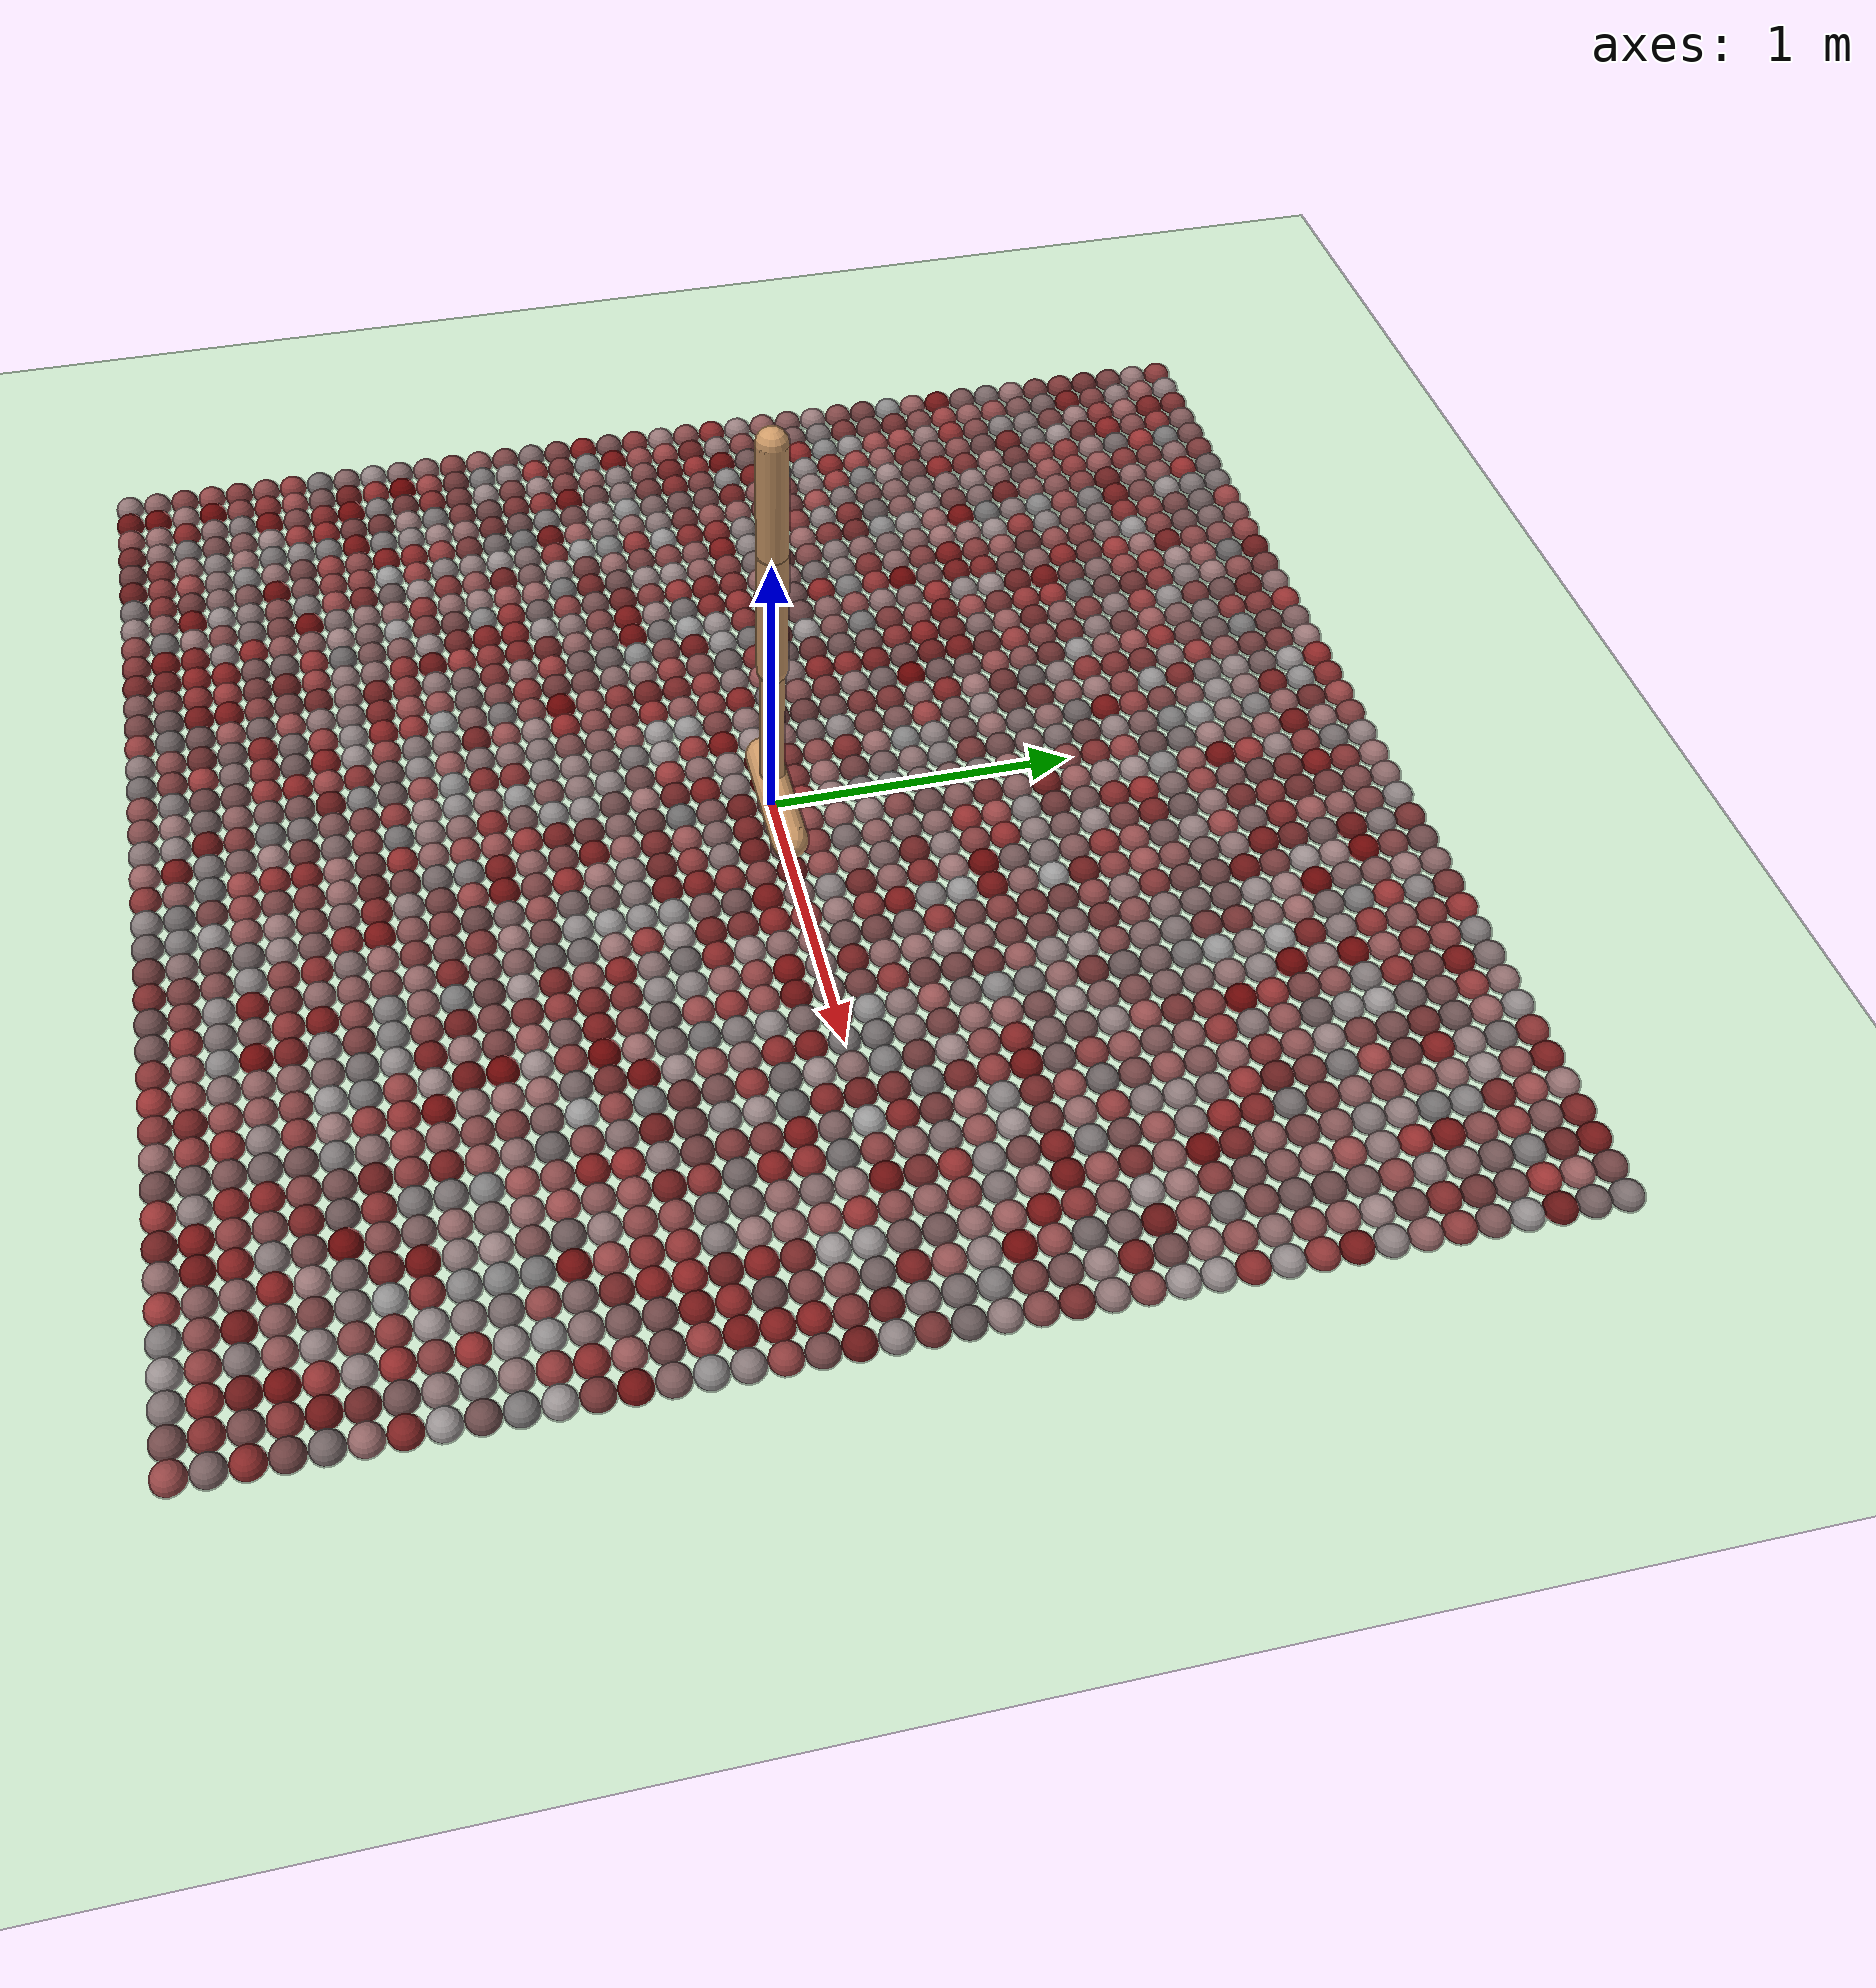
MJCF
<mujoco model="hopper">
  <compiler angle="degree" inertiafromgeom="true"/>
  <default>
    <joint armature="1" damping="1" limited="true"/>
    <geom conaffinity="1" condim="1" contype="1" margin="0.001" material="geom" rgba="0.8 0.6 .4 1" solimp=".8 .8 .01" solref=".02 1"/>
    <motor ctrllimited="true" ctrlrange="-.4 .4"/>
  </default>
  <option integrator="RK4" timestep="0.002"/>
  <visual>
    <map znear="0.02"/>
  </visual>
  <worldbody>
    <light pos="0 0 .6"/>
    <camera name="closeup" pos="0 -4 2" xyaxes="1 0 0 0 1 2"/>
     <!-- Start spacing = 0.1 -->
    <geom name="green_sphere_0_0" pos="0.0 0.0 0.001" size=".05" rgba="0.494062470877316 0.2981008791287673 0.2981008791287673 1.0"/>
<geom name="green_sphere_0_1" pos="0.0 0.1 0.001" size=".05" rgba="0.5697705791102541 0.19891839647807208 0.19891839647807208 1.0"/>
<geom name="green_sphere_0_-1" pos="0.0 -0.1 0.001" size=".05" rgba="0.4029060687223145 0.10306808575589993 0.10306808575589993 1.0"/>
<geom name="green_sphere_0_2" pos="0.0 0.2 0.001" size=".05" rgba="0.5574317506755642 0.43908266085124853 0.43908266085124853 1.0"/>
<geom name="green_sphere_0_-2" pos="0.0 -0.2 0.001" size=".05" rgba="0.46889252068873943 0.3001283317125718 0.3001283317125718 1.0"/>
<geom name="green_sphere_0_3" pos="0.0 0.30000000000000004 0.001" size=".05" rgba="0.43175803148172154 0.3906731948400911 0.3906731948400911 1.0"/>
<geom name="green_sphere_0_-3" pos="0.0 -0.30000000000000004 0.001" size=".05" rgba="0.41605870348575147 0.41079952006909176 0.41079952006909176 1.0"/>
<geom name="green_sphere_0_4" pos="0.0 0.4 0.001" size=".05" rgba="0.47953967594800695 0.46637490347127164 0.46637490347127164 1.0"/>
<geom name="green_sphere_0_-4" pos="0.0 -0.4 0.001" size=".05" rgba="0.4116486544683909 0.23985907588518698 0.23985907588518698 1.0"/>
<geom name="green_sphere_0_5" pos="0.0 0.5 0.001" size=".05" rgba="0.45599232762887165 0.36747218677072024 0.36747218677072024 1.0"/>
<geom name="green_sphere_0_-5" pos="0.0 -0.5 0.001" size=".05" rgba="0.4836151438125078 0.3526451498307152 0.3526451498307152 1.0"/>
<geom name="green_sphere_0_6" pos="0.0 0.6000000000000001 0.001" size=".05" rgba="0.451735535361146 0.329182861380328 0.329182861380328 1.0"/>
<geom name="green_sphere_0_-6" pos="0.0 -0.6000000000000001 0.001" size=".05" rgba="0.4175178831329865 0.20969991988069428 0.20969991988069428 1.0"/>
<geom name="green_sphere_0_7" pos="0.0 0.7000000000000001 0.001" size=".05" rgba="0.44485820456343855 0.39075376544681856 0.39075376544681856 1.0"/>
<geom name="green_sphere_0_-7" pos="0.0 -0.7000000000000001 0.001" size=".05" rgba="0.43435987162209855 0.11331950137386043 0.11331950137386043 1.0"/>
<geom name="green_sphere_0_8" pos="0.0 0.8 0.001" size=".05" rgba="0.5700568602332692 0.3825765429206419 0.3825765429206419 1.0"/>
<geom name="green_sphere_0_-8" pos="0.0 -0.8 0.001" size=".05" rgba="0.5676002812338161 0.20744068941535043 0.20744068941535043 1.0"/>
<geom name="green_sphere_0_9" pos="0.0 0.9 0.001" size=".05" rgba="0.45049742592203373 0.4158558332396763 0.4158558332396763 1.0"/>
<geom name="green_sphere_0_-9" pos="0.0 -0.9 0.001" size=".05" rgba="0.5711043629026783 0.2988183040250452 0.2988183040250452 1.0"/>
<geom name="green_sphere_0_10" pos="0.0 1.0 0.001" size=".05" rgba="0.5142760475936871 0.2553188486272467 0.2553188486272467 1.0"/>
<geom name="green_sphere_0_-10" pos="0.0 -1.0 0.001" size=".05" rgba="0.5574462831334305 0.262901838163967 0.262901838163967 1.0"/>
<geom name="green_sphere_0_11" pos="0.0 1.1 0.001" size=".05" rgba="0.483299000642214 0.16647630649313006 0.16647630649313006 1.0"/>
<geom name="green_sphere_0_-11" pos="0.0 -1.1 0.001" size=".05" rgba="0.5504640849656685 0.36813898795691447 0.36813898795691447 1.0"/>
<geom name="green_sphere_0_12" pos="0.0 1.2000000000000002 0.001" size=".05" rgba="0.5788118120767654 0.26797925123427935 0.26797925123427935 1.0"/>
<geom name="green_sphere_0_-12" pos="0.0 -1.2000000000000002 0.001" size=".05" rgba="0.5573202856385289 0.17175915044843776 0.17175915044843776 1.0"/>
<geom name="green_sphere_0_13" pos="0.0 1.3 0.001" size=".05" rgba="0.4042583339742829 0.2851261745194796 0.2851261745194796 1.0"/>
<geom name="green_sphere_0_-13" pos="0.0 -1.3 0.001" size=".05" rgba="0.4232743593759921 0.21820184588771085 0.21820184588771085 1.0"/>
<geom name="green_sphere_0_14" pos="0.0 1.4000000000000001 0.001" size=".05" rgba="0.41916705988075276 0.3756306911214783 0.3756306911214783 1.0"/>
<geom name="green_sphere_0_-14" pos="0.0 -1.4000000000000001 0.001" size=".05" rgba="0.588656388432246 0.4007840667262876 0.4007840667262876 1.0"/>
<geom name="green_sphere_0_15" pos="0.0 1.5 0.001" size=".05" rgba="0.5951668797516962 0.45320528556848244 0.45320528556848244 1.0"/>
<geom name="green_sphere_0_-15" pos="0.0 -1.5 0.001" size=".05" rgba="0.48859003355753944 0.12701151909676273 0.12701151909676273 1.0"/>
<geom name="green_sphere_0_16" pos="0.0 1.6 0.001" size=".05" rgba="0.4774819451590226 0.3394837926320141 0.3394837926320141 1.0"/>
<geom name="green_sphere_0_-16" pos="0.0 -1.6 0.001" size=".05" rgba="0.5393613656918376 0.16843138501408783 0.16843138501408783 1.0"/>
<geom name="green_sphere_0_17" pos="0.0 1.7000000000000002 0.001" size=".05" rgba="0.5609960376992127 0.36130439944211834 0.36130439944211834 1.0"/>
<geom name="green_sphere_0_-17" pos="0.0 -1.7000000000000002 0.001" size=".05" rgba="0.5943144927459715 0.2687118097972958 0.2687118097972958 1.0"/>
<geom name="green_sphere_0_18" pos="0.0 1.8 0.001" size=".05" rgba="0.41966591269095793 0.07377365541934572 0.07377365541934572 1.0"/>
<geom name="green_sphere_0_-18" pos="0.0 -1.8 0.001" size=".05" rgba="0.426971328380322 0.40790685562545687 0.40790685562545687 1.0"/>
<geom name="green_sphere_0_19" pos="0.0 1.9000000000000001 0.001" size=".05" rgba="0.5746965229027531 0.4159624019891222 0.4159624019891222 1.0"/>
<geom name="green_sphere_0_-19" pos="0.0 -1.9000000000000001 0.001" size=".05" rgba="0.5375273575848147 0.3446792979017123 0.3446792979017123 1.0"/>
<geom name="green_sphere_0_20" pos="0.0 2.0 0.001" size=".05" rgba="0.5016099251821257 0.24080412597945416 0.24080412597945416 1.0"/>
<geom name="green_sphere_0_-20" pos="0.0 -2.0 0.001" size=".05" rgba="0.527141978147968 0.19750855372069565 0.19750855372069565 1.0"/>
<geom name="green_sphere_1_0" pos="0.1 0.0 0.001" size=".05" rgba="0.48449769151718325 0.34794706287325394 0.34794706287325394 1.0"/>
<geom name="green_sphere_-1_0" pos="-0.1 0.0 0.001" size=".05" rgba="0.42069398172937555 0.0272094330631536 0.0272094330631536 1.0"/>
<geom name="green_sphere_1_1" pos="0.1 0.1 0.001" size=".05" rgba="0.5479631990825232 0.2741554248908904 0.2741554248908904 1.0"/>
<geom name="green_sphere_-1_1" pos="-0.1 0.1 0.001" size=".05" rgba="0.4742993007076241 0.18816681974772265 0.18816681974772265 1.0"/>
<geom name="green_sphere_1_-1" pos="0.1 -0.1 0.001" size=".05" rgba="0.43953093868686166 0.12287318996398838 0.12287318996398838 1.0"/>
<geom name="green_sphere_-1_-1" pos="-0.1 -0.1 0.001" size=".05" rgba="0.5130791023933969 0.4339646544675146 0.4339646544675146 1.0"/>
<geom name="green_sphere_1_2" pos="0.1 0.2 0.001" size=".05" rgba="0.577119814115821 0.3769595800135951 0.3769595800135951 1.0"/>
<geom name="green_sphere_-1_2" pos="-0.1 0.2 0.001" size=".05" rgba="0.580296277431166 0.3881881754754905 0.3881881754754905 1.0"/>
<geom name="green_sphere_1_-2" pos="0.1 -0.2 0.001" size=".05" rgba="0.47480193335757065 0.35805490196002715 0.35805490196002715 1.0"/>
<geom name="green_sphere_-1_-2" pos="-0.1 -0.2 0.001" size=".05" rgba="0.4806443527427338 0.11244884181739107 0.11244884181739107 1.0"/>
<geom name="green_sphere_1_3" pos="0.1 0.30000000000000004 0.001" size=".05" rgba="0.5827360957088948 0.46767150270781127 0.46767150270781127 1.0"/>
<geom name="green_sphere_-1_3" pos="-0.1 0.30000000000000004 0.001" size=".05" rgba="0.41451349442504953 0.2240745647159363 0.2240745647159363 1.0"/>
<geom name="green_sphere_1_-3" pos="0.1 -0.30000000000000004 0.001" size=".05" rgba="0.5824693849556903 0.3164972169880262 0.3164972169880262 1.0"/>
<geom name="green_sphere_-1_-3" pos="-0.1 -0.30000000000000004 0.001" size=".05" rgba="0.4194274530291362 0.1333150439700454 0.1333150439700454 1.0"/>
<geom name="green_sphere_1_4" pos="0.1 0.4 0.001" size=".05" rgba="0.4865180990417312 0.25071406580892197 0.25071406580892197 1.0"/>
<geom name="green_sphere_-1_4" pos="-0.1 0.4 0.001" size=".05" rgba="0.45273387429896744 0.34701612698409284 0.34701612698409284 1.0"/>
<geom name="green_sphere_1_-4" pos="0.1 -0.4 0.001" size=".05" rgba="0.44939721481092826 0.15175330319408542 0.15175330319408542 1.0"/>
<geom name="green_sphere_-1_-4" pos="-0.1 -0.4 0.001" size=".05" rgba="0.5987179316537272 0.4208883981046651 0.4208883981046651 1.0"/>
<geom name="green_sphere_1_5" pos="0.1 0.5 0.001" size=".05" rgba="0.41918124098468124 0.2839923337550151 0.2839923337550151 1.0"/>
<geom name="green_sphere_-1_5" pos="-0.1 0.5 0.001" size=".05" rgba="0.536648322302598 0.4198369941358539 0.4198369941358539 1.0"/>
<geom name="green_sphere_1_-5" pos="0.1 -0.5 0.001" size=".05" rgba="0.5638438001327523 0.3543756522781334 0.3543756522781334 1.0"/>
<geom name="green_sphere_-1_-5" pos="-0.1 -0.5 0.001" size=".05" rgba="0.40802408933568557 0.2694747168444319 0.2694747168444319 1.0"/>
<geom name="green_sphere_1_6" pos="0.1 0.6000000000000001 0.001" size=".05" rgba="0.4976229907800205 0.33181905759443664 0.33181905759443664 1.0"/>
<geom name="green_sphere_-1_6" pos="-0.1 0.6000000000000001 0.001" size=".05" rgba="0.48200397560605407 0.44342209138372474 0.44342209138372474 1.0"/>
<geom name="green_sphere_1_-6" pos="0.1 -0.6000000000000001 0.001" size=".05" rgba="0.4408361024663176 0.0892064322155583 0.0892064322155583 1.0"/>
<geom name="green_sphere_-1_-6" pos="-0.1 -0.6000000000000001 0.001" size=".05" rgba="0.5632743457745364 0.5208694627203587 0.5208694627203587 1.0"/>
<geom name="green_sphere_1_7" pos="0.1 0.7000000000000001 0.001" size=".05" rgba="0.4568520821938552 0.19037609241374298 0.19037609241374298 1.0"/>
<geom name="green_sphere_-1_7" pos="-0.1 0.7000000000000001 0.001" size=".05" rgba="0.44096542061871696 0.1960819315926473 0.1960819315926473 1.0"/>
<geom name="green_sphere_1_-7" pos="0.1 -0.7000000000000001 0.001" size=".05" rgba="0.4761665753666043 0.2606762356001711 0.2606762356001711 1.0"/>
<geom name="green_sphere_-1_-7" pos="-0.1 -0.7000000000000001 0.001" size=".05" rgba="0.5399398792730147 0.5218754067845376 0.5218754067845376 1.0"/>
<geom name="green_sphere_1_8" pos="0.1 0.8 0.001" size=".05" rgba="0.518308580754971 0.366529314677178 0.366529314677178 1.0"/>
<geom name="green_sphere_-1_8" pos="-0.1 0.8 0.001" size=".05" rgba="0.41402668275795773 0.2700097335655528 0.2700097335655528 1.0"/>
<geom name="green_sphere_1_-8" pos="0.1 -0.8 0.001" size=".05" rgba="0.5558189180012175 0.3658665724799862 0.3658665724799862 1.0"/>
<geom name="green_sphere_-1_-8" pos="-0.1 -0.8 0.001" size=".05" rgba="0.4636676842303792 0.3353514279699928 0.3353514279699928 1.0"/>
<geom name="green_sphere_1_9" pos="0.1 0.9 0.001" size=".05" rgba="0.42293613087905857 0.09403135427150089 0.09403135427150089 1.0"/>
<geom name="green_sphere_-1_9" pos="-0.1 0.9 0.001" size=".05" rgba="0.47527504469967563 0.35685724620892983 0.35685724620892983 1.0"/>
<geom name="green_sphere_1_-9" pos="0.1 -0.9 0.001" size=".05" rgba="0.44423402226532693 0.09322173725183541 0.09322173725183541 1.0"/>
<geom name="green_sphere_-1_-9" pos="-0.1 -0.9 0.001" size=".05" rgba="0.5179636882533478 0.16128415823426206 0.16128415823426206 1.0"/>
<geom name="green_sphere_1_10" pos="0.1 1.0 0.001" size=".05" rgba="0.5815426050264922 0.3482439114276167 0.3482439114276167 1.0"/>
<geom name="green_sphere_-1_10" pos="-0.1 1.0 0.001" size=".05" rgba="0.45920762344245664 0.39267955917601927 0.39267955917601927 1.0"/>
<geom name="green_sphere_1_-10" pos="0.1 -1.0 0.001" size=".05" rgba="0.4717349068101191 0.44587080553809244 0.44587080553809244 1.0"/>
<geom name="green_sphere_-1_-10" pos="-0.1 -1.0 0.001" size=".05" rgba="0.5230496894047698 0.3862755199653074 0.3862755199653074 1.0"/>
<geom name="green_sphere_1_11" pos="0.1 1.1 0.001" size=".05" rgba="0.5750374150452523 0.46753811268018103 0.46753811268018103 1.0"/>
<geom name="green_sphere_-1_11" pos="-0.1 1.1 0.001" size=".05" rgba="0.42351635337883403 0.275688040036677 0.275688040036677 1.0"/>
<geom name="green_sphere_1_-11" pos="0.1 -1.1 0.001" size=".05" rgba="0.4354223767237869 0.384147018484119 0.384147018484119 1.0"/>
<geom name="green_sphere_-1_-11" pos="-0.1 -1.1 0.001" size=".05" rgba="0.5536039050056071 0.4448849339811 0.4448849339811 1.0"/>
<geom name="green_sphere_1_12" pos="0.1 1.2000000000000002 0.001" size=".05" rgba="0.5969526234561396 0.5141460750009932 0.5141460750009932 1.0"/>
<geom name="green_sphere_-1_12" pos="-0.1 1.2000000000000002 0.001" size=".05" rgba="0.5535461763728015 0.4777056648148261 0.4777056648148261 1.0"/>
<geom name="green_sphere_1_-12" pos="0.1 -1.2000000000000002 0.001" size=".05" rgba="0.43825839819984913 0.2420713941637127 0.2420713941637127 1.0"/>
<geom name="green_sphere_-1_-12" pos="-0.1 -1.2000000000000002 0.001" size=".05" rgba="0.42809172051963684 0.41238602585854284 0.41238602585854284 1.0"/>
<geom name="green_sphere_1_13" pos="0.1 1.3 0.001" size=".05" rgba="0.5119877571691255 0.49484080331508706 0.49484080331508706 1.0"/>
<geom name="green_sphere_-1_13" pos="-0.1 1.3 0.001" size=".05" rgba="0.4709604395481158 0.3382301282918927 0.3382301282918927 1.0"/>
<geom name="green_sphere_1_-13" pos="0.1 -1.3 0.001" size=".05" rgba="0.4081375945091217 0.15586276806664895 0.15586276806664895 1.0"/>
<geom name="green_sphere_-1_-13" pos="-0.1 -1.3 0.001" size=".05" rgba="0.5002305067814448 0.2497661978792574 0.2497661978792574 1.0"/>
<geom name="green_sphere_1_14" pos="0.1 1.4000000000000001 0.001" size=".05" rgba="0.5697125225427997 0.32282380539868416 0.32282380539868416 1.0"/>
<geom name="green_sphere_-1_14" pos="-0.1 1.4000000000000001 0.001" size=".05" rgba="0.45978169789038636 0.45332327925758487 0.45332327925758487 1.0"/>
<geom name="green_sphere_1_-14" pos="0.1 -1.4000000000000001 0.001" size=".05" rgba="0.5776428787587571 0.39987088745701127 0.39987088745701127 1.0"/>
<geom name="green_sphere_-1_-14" pos="-0.1 -1.4000000000000001 0.001" size=".05" rgba="0.4567876199836718 0.3626630537449563 0.3626630537449563 1.0"/>
<geom name="green_sphere_1_15" pos="0.1 1.5 0.001" size=".05" rgba="0.42578921935353004 0.05365061420774947 0.05365061420774947 1.0"/>
<geom name="green_sphere_-1_15" pos="-0.1 1.5 0.001" size=".05" rgba="0.5611132693612051 0.5531726154764185 0.5531726154764185 1.0"/>
<geom name="green_sphere_1_-15" pos="0.1 -1.5 0.001" size=".05" rgba="0.48977016723659716 0.21914543510821244 0.21914543510821244 1.0"/>
<geom name="green_sphere_-1_-15" pos="-0.1 -1.5 0.001" size=".05" rgba="0.4314637604013227 0.21581386243954695 0.21581386243954695 1.0"/>
<geom name="green_sphere_1_16" pos="0.1 1.6 0.001" size=".05" rgba="0.5814615541562846 0.20521184699898598 0.20521184699898598 1.0"/>
<geom name="green_sphere_-1_16" pos="-0.1 1.6 0.001" size=".05" rgba="0.563274642380147 0.4534840396130275 0.4534840396130275 1.0"/>
<geom name="green_sphere_1_-16" pos="0.1 -1.6 0.001" size=".05" rgba="0.46343416819824984 0.260218205148559 0.260218205148559 1.0"/>
<geom name="green_sphere_-1_-16" pos="-0.1 -1.6 0.001" size=".05" rgba="0.5996131254754812 0.46151062527776354 0.46151062527776354 1.0"/>
<geom name="green_sphere_1_17" pos="0.1 1.7000000000000002 0.001" size=".05" rgba="0.5605208531440272 0.47267508716874795 0.47267508716874795 1.0"/>
<geom name="green_sphere_-1_17" pos="-0.1 1.7000000000000002 0.001" size=".05" rgba="0.47244540962080617 0.456877172931869 0.456877172931869 1.0"/>
<geom name="green_sphere_1_-17" pos="0.1 -1.7000000000000002 0.001" size=".05" rgba="0.5555664516450691 0.26582689465341125 0.26582689465341125 1.0"/>
<geom name="green_sphere_-1_-17" pos="-0.1 -1.7000000000000002 0.001" size=".05" rgba="0.4677052941180086 0.34694144594707493 0.34694144594707493 1.0"/>
<geom name="green_sphere_1_18" pos="0.1 1.8 0.001" size=".05" rgba="0.5221253070998829 0.22673448944013913 0.22673448944013913 1.0"/>
<geom name="green_sphere_-1_18" pos="-0.1 1.8 0.001" size=".05" rgba="0.5581691384465232 0.36508817309263586 0.36508817309263586 1.0"/>
<geom name="green_sphere_1_-18" pos="0.1 -1.8 0.001" size=".05" rgba="0.4362349442496948 0.2367778078738256 0.2367778078738256 1.0"/>
<geom name="green_sphere_-1_-18" pos="-0.1 -1.8 0.001" size=".05" rgba="0.47045471858181864 0.43442367582020835 0.43442367582020835 1.0"/>
<geom name="green_sphere_1_19" pos="0.1 1.9000000000000001 0.001" size=".05" rgba="0.4416327540064306 0.40906321695631626 0.40906321695631626 1.0"/>
<geom name="green_sphere_-1_19" pos="-0.1 1.9000000000000001 0.001" size=".05" rgba="0.4101086262409428 0.15868298110785445 0.15868298110785445 1.0"/>
<geom name="green_sphere_1_-19" pos="0.1 -1.9000000000000001 0.001" size=".05" rgba="0.41711147920655667 0.3961345997094471 0.3961345997094471 1.0"/>
<geom name="green_sphere_-1_-19" pos="-0.1 -1.9000000000000001 0.001" size=".05" rgba="0.446597006562188 0.08560471790939489 0.08560471790939489 1.0"/>
<geom name="green_sphere_1_20" pos="0.1 2.0 0.001" size=".05" rgba="0.5470780677992851 0.476317608050284 0.476317608050284 1.0"/>
<geom name="green_sphere_-1_20" pos="-0.1 2.0 0.001" size=".05" rgba="0.5798096796748878 0.25698672658599153 0.25698672658599153 1.0"/>
<geom name="green_sphere_1_-20" pos="0.1 -2.0 0.001" size=".05" rgba="0.5225537037565884 0.48445025886763327 0.48445025886763327 1.0"/>
<geom name="green_sphere_-1_-20" pos="-0.1 -2.0 0.001" size=".05" rgba="0.5931455848348888 0.3857127721141618 0.3857127721141618 1.0"/>
<geom name="green_sphere_2_0" pos="0.2 0.0 0.001" size=".05" rgba="0.4572229336245841 0.3114162810795237 0.3114162810795237 1.0"/>
<geom name="green_sphere_-2_0" pos="-0.2 0.0 0.001" size=".05" rgba="0.4428930319881142 0.08468669919496713 0.08468669919496713 1.0"/>
<geom name="green_sphere_2_1" pos="0.2 0.1 0.001" size=".05" rgba="0.5035751146385093 0.2160287499638367 0.2160287499638367 1.0"/>
<geom name="green_sphere_-2_1" pos="-0.2 0.1 0.001" size=".05" rgba="0.458476622217935 0.17435716135004592 0.17435716135004592 1.0"/>
<geom name="green_sphere_2_-1" pos="0.2 -0.1 0.001" size=".05" rgba="0.40732849677388605 0.0905163345914789 0.0905163345914789 1.0"/>
<geom name="green_sphere_-2_-1" pos="-0.2 -0.1 0.001" size=".05" rgba="0.5616788996970722 0.461692404391153 0.461692404391153 1.0"/>
<geom name="green_sphere_2_2" pos="0.2 0.2 0.001" size=".05" rgba="0.44180481168985847 0.37938962861266734 0.37938962861266734 1.0"/>
<geom name="green_sphere_-2_2" pos="-0.2 0.2 0.001" size=".05" rgba="0.5248244289717612 0.2692206375544523 0.2692206375544523 1.0"/>
<geom name="green_sphere_2_-2" pos="0.2 -0.2 0.001" size=".05" rgba="0.5056767533851806 0.41932315895901884 0.41932315895901884 1.0"/>
<geom name="green_sphere_-2_-2" pos="-0.2 -0.2 0.001" size=".05" rgba="0.5183706969478139 0.38103802301190004 0.38103802301190004 1.0"/>
<geom name="green_sphere_2_3" pos="0.2 0.30000000000000004 0.001" size=".05" rgba="0.5322253030946362 0.35029967268221407 0.35029967268221407 1.0"/>
<geom name="green_sphere_-2_3" pos="-0.2 0.30000000000000004 0.001" size=".05" rgba="0.47161363530899636 0.15068464230905287 0.15068464230905287 1.0"/>
<geom name="green_sphere_2_-3" pos="0.2 -0.30000000000000004 0.001" size=".05" rgba="0.5429778834729524 0.22432960021057008 0.22432960021057008 1.0"/>
<geom name="green_sphere_-2_-3" pos="-0.2 -0.30000000000000004 0.001" size=".05" rgba="0.5907524826060183 0.22525995687478917 0.22525995687478917 1.0"/>
<geom name="green_sphere_2_4" pos="0.2 0.4 0.001" size=".05" rgba="0.49250725146093877 0.36737780465576464 0.36737780465576464 1.0"/>
<geom name="green_sphere_-2_4" pos="-0.2 0.4 0.001" size=".05" rgba="0.5901937604088806 0.4059473449118127 0.4059473449118127 1.0"/>
<geom name="green_sphere_2_-4" pos="0.2 -0.4 0.001" size=".05" rgba="0.4006820239892413 0.13306379634282278 0.13306379634282278 1.0"/>
<geom name="green_sphere_-2_-4" pos="-0.2 -0.4 0.001" size=".05" rgba="0.4357614312420536 0.28334146902590607 0.28334146902590607 1.0"/>
<geom name="green_sphere_2_5" pos="0.2 0.5 0.001" size=".05" rgba="0.5183533655923769 0.37188005956004566 0.37188005956004566 1.0"/>
<geom name="green_sphere_-2_5" pos="-0.2 0.5 0.001" size=".05" rgba="0.5013991531374814 0.4987669890701236 0.4987669890701236 1.0"/>
<geom name="green_sphere_2_-5" pos="0.2 -0.5 0.001" size=".05" rgba="0.5267329669861474 0.42654708204342884 0.42654708204342884 1.0"/>
<geom name="green_sphere_-2_-5" pos="-0.2 -0.5 0.001" size=".05" rgba="0.540472758782073 0.489684270112273 0.489684270112273 1.0"/>
<geom name="green_sphere_2_6" pos="0.2 0.6000000000000001 0.001" size=".05" rgba="0.5720227066078959 0.18622807481649895 0.18622807481649895 1.0"/>
<geom name="green_sphere_-2_6" pos="-0.2 0.6000000000000001 0.001" size=".05" rgba="0.5255211478640796 0.4724391517151133 0.4724391517151133 1.0"/>
<geom name="green_sphere_2_-6" pos="0.2 -0.6000000000000001 0.001" size=".05" rgba="0.5944308590423895 0.41771428942635414 0.41771428942635414 1.0"/>
<geom name="green_sphere_-2_-6" pos="-0.2 -0.6000000000000001 0.001" size=".05" rgba="0.530011615780775 0.42664549642213356 0.42664549642213356 1.0"/>
<geom name="green_sphere_2_7" pos="0.2 0.7000000000000001 0.001" size=".05" rgba="0.5941924742909557 0.27348212137780364 0.27348212137780364 1.0"/>
<geom name="green_sphere_-2_7" pos="-0.2 0.7000000000000001 0.001" size=".05" rgba="0.437552993171713 0.32060925859602074 0.32060925859602074 1.0"/>
<geom name="green_sphere_2_-7" pos="0.2 -0.7000000000000001 0.001" size=".05" rgba="0.5432724215830607 0.16268058185161416 0.16268058185161416 1.0"/>
<geom name="green_sphere_-2_-7" pos="-0.2 -0.7000000000000001 0.001" size=".05" rgba="0.4940234893916955 0.3176313633890323 0.3176313633890323 1.0"/>
<geom name="green_sphere_2_8" pos="0.2 0.8 0.001" size=".05" rgba="0.5243544310902246 0.4835565861057511 0.4835565861057511 1.0"/>
<geom name="green_sphere_-2_8" pos="-0.2 0.8 0.001" size=".05" rgba="0.575863364358721 0.4065804001712925 0.4065804001712925 1.0"/>
<geom name="green_sphere_2_-8" pos="0.2 -0.8 0.001" size=".05" rgba="0.4654104465096645 0.2541206753517958 0.2541206753517958 1.0"/>
<geom name="green_sphere_-2_-8" pos="-0.2 -0.8 0.001" size=".05" rgba="0.5575760500648198 0.5504112443095407 0.5504112443095407 1.0"/>
<geom name="green_sphere_2_9" pos="0.2 0.9 0.001" size=".05" rgba="0.4048653664466872 0.19772565041219903 0.19772565041219903 1.0"/>
<geom name="green_sphere_-2_9" pos="-0.2 0.9 0.001" size=".05" rgba="0.4436592268195682 0.3671963007169322 0.3671963007169322 1.0"/>
<geom name="green_sphere_2_-9" pos="0.2 -0.9 0.001" size=".05" rgba="0.42894124755989826 0.06167590976908738 0.06167590976908738 1.0"/>
<geom name="green_sphere_-2_-9" pos="-0.2 -0.9 0.001" size=".05" rgba="0.549838338296108 0.39950206014054157 0.39950206014054157 1.0"/>
<geom name="green_sphere_2_10" pos="0.2 1.0 0.001" size=".05" rgba="0.44853826834104155 0.30823166127118407 0.30823166127118407 1.0"/>
<geom name="green_sphere_-2_10" pos="-0.2 1.0 0.001" size=".05" rgba="0.5388453025481367 0.37852639965709256 0.37852639965709256 1.0"/>
<geom name="green_sphere_2_-10" pos="0.2 -1.0 0.001" size=".05" rgba="0.5839618969622318 0.27032118008860806 0.27032118008860806 1.0"/>
<geom name="green_sphere_-2_-10" pos="-0.2 -1.0 0.001" size=".05" rgba="0.5384350140756997 0.5166711032766507 0.5166711032766507 1.0"/>
<geom name="green_sphere_2_11" pos="0.2 1.1 0.001" size=".05" rgba="0.4949537003477064 0.15506370452412271 0.15506370452412271 1.0"/>
<geom name="green_sphere_-2_11" pos="-0.2 1.1 0.001" size=".05" rgba="0.40352128940172527 0.36669683724984065 0.36669683724984065 1.0"/>
<geom name="green_sphere_2_-11" pos="0.2 -1.1 0.001" size=".05" rgba="0.4268884107770123 0.23873532627404506 0.23873532627404506 1.0"/>
<geom name="green_sphere_-2_-11" pos="-0.2 -1.1 0.001" size=".05" rgba="0.5937169050474582 0.4588232190412164 0.4588232190412164 1.0"/>
<geom name="green_sphere_2_12" pos="0.2 1.2000000000000002 0.001" size=".05" rgba="0.5682523789865465 0.17249253590620722 0.17249253590620722 1.0"/>
<geom name="green_sphere_-2_12" pos="-0.2 1.2000000000000002 0.001" size=".05" rgba="0.44450502081350196 0.06692398269537797 0.06692398269537797 1.0"/>
<geom name="green_sphere_2_-12" pos="0.2 -1.2000000000000002 0.001" size=".05" rgba="0.5280716361182947 0.4332961140013615 0.4332961140013615 1.0"/>
<geom name="green_sphere_-2_-12" pos="-0.2 -1.2000000000000002 0.001" size=".05" rgba="0.5352107232513565 0.20570590650789883 0.20570590650789883 1.0"/>
<geom name="green_sphere_2_13" pos="0.2 1.3 0.001" size=".05" rgba="0.4657618558036882 0.37060440470814104 0.37060440470814104 1.0"/>
<geom name="green_sphere_-2_13" pos="-0.2 1.3 0.001" size=".05" rgba="0.5455483339778853 0.23881401518572265 0.23881401518572265 1.0"/>
<geom name="green_sphere_2_-13" pos="0.2 -1.3 0.001" size=".05" rgba="0.47711730362922666 0.136029829554146 0.136029829554146 1.0"/>
<geom name="green_sphere_-2_-13" pos="-0.2 -1.3 0.001" size=".05" rgba="0.4712434545160825 0.25328826140670235 0.25328826140670235 1.0"/>
<geom name="green_sphere_2_14" pos="0.2 1.4000000000000001 0.001" size=".05" rgba="0.5552133311078608 0.24386266433749476 0.24386266433749476 1.0"/>
<geom name="green_sphere_-2_14" pos="-0.2 1.4000000000000001 0.001" size=".05" rgba="0.457011867573951 0.23909990513976687 0.23909990513976687 1.0"/>
<geom name="green_sphere_2_-14" pos="0.2 -1.4000000000000001 0.001" size=".05" rgba="0.4930547513710276 0.36548778259468995 0.36548778259468995 1.0"/>
<geom name="green_sphere_-2_-14" pos="-0.2 -1.4000000000000001 0.001" size=".05" rgba="0.47695451024920366 0.31322292263639645 0.31322292263639645 1.0"/>
<geom name="green_sphere_2_15" pos="0.2 1.5 0.001" size=".05" rgba="0.47890474831675733 0.31786460884489426 0.31786460884489426 1.0"/>
<geom name="green_sphere_-2_15" pos="-0.2 1.5 0.001" size=".05" rgba="0.5298686560700834 0.33268606630583375 0.33268606630583375 1.0"/>
<geom name="green_sphere_2_-15" pos="0.2 -1.5 0.001" size=".05" rgba="0.48040388173399085 0.2558149992578404 0.2558149992578404 1.0"/>
<geom name="green_sphere_-2_-15" pos="-0.2 -1.5 0.001" size=".05" rgba="0.45348242927291615 0.4058163497033707 0.4058163497033707 1.0"/>
<geom name="green_sphere_2_16" pos="0.2 1.6 0.001" size=".05" rgba="0.41460542466455896 0.2780470366596514 0.2780470366596514 1.0"/>
<geom name="green_sphere_-2_16" pos="-0.2 1.6 0.001" size=".05" rgba="0.5493756587860374 0.5147429783485715 0.5147429783485715 1.0"/>
<geom name="green_sphere_2_-16" pos="0.2 -1.6 0.001" size=".05" rgba="0.583096745063769 0.44578455589329735 0.44578455589329735 1.0"/>
<geom name="green_sphere_-2_-16" pos="-0.2 -1.6 0.001" size=".05" rgba="0.42914991880485426 0.4006601973810872 0.4006601973810872 1.0"/>
<geom name="green_sphere_2_17" pos="0.2 1.7000000000000002 0.001" size=".05" rgba="0.4496081498708789 0.1850579673033435 0.1850579673033435 1.0"/>
<geom name="green_sphere_-2_17" pos="-0.2 1.7000000000000002 0.001" size=".05" rgba="0.5470137164096052 0.42045772786555624 0.42045772786555624 1.0"/>
<geom name="green_sphere_2_-17" pos="0.2 -1.7000000000000002 0.001" size=".05" rgba="0.5572632751244552 0.3295760092690684 0.3295760092690684 1.0"/>
<geom name="green_sphere_-2_-17" pos="-0.2 -1.7000000000000002 0.001" size=".05" rgba="0.49868430021575777 0.2259590738991929 0.2259590738991929 1.0"/>
<geom name="green_sphere_2_18" pos="0.2 1.8 0.001" size=".05" rgba="0.4733786790120539 0.08427577048963175 0.08427577048963175 1.0"/>
<geom name="green_sphere_-2_18" pos="-0.2 1.8 0.001" size=".05" rgba="0.4424598361218273 0.11408685579744043 0.11408685579744043 1.0"/>
<geom name="green_sphere_2_-18" pos="0.2 -1.8 0.001" size=".05" rgba="0.5610047677035166 0.5372168767903723 0.5372168767903723 1.0"/>
<geom name="green_sphere_-2_-18" pos="-0.2 -1.8 0.001" size=".05" rgba="0.4167620457470855 0.0884525739405721 0.0884525739405721 1.0"/>
<geom name="green_sphere_2_19" pos="0.2 1.9000000000000001 0.001" size=".05" rgba="0.4922903329926568 0.1882563352595613 0.1882563352595613 1.0"/>
<geom name="green_sphere_-2_19" pos="-0.2 1.9000000000000001 0.001" size=".05" rgba="0.5354756081468992 0.5265087175382867 0.5265087175382867 1.0"/>
<geom name="green_sphere_2_-19" pos="0.2 -1.9000000000000001 0.001" size=".05" rgba="0.48239498600593683 0.4622334184759061 0.4622334184759061 1.0"/>
<geom name="green_sphere_-2_-19" pos="-0.2 -1.9000000000000001 0.001" size=".05" rgba="0.5437008536733376 0.4843642876157193 0.4843642876157193 1.0"/>
<geom name="green_sphere_2_20" pos="0.2 2.0 0.001" size=".05" rgba="0.5796372100803108 0.4118728187353251 0.4118728187353251 1.0"/>
<geom name="green_sphere_-2_20" pos="-0.2 2.0 0.001" size=".05" rgba="0.5084659315011022 0.16390373801959618 0.16390373801959618 1.0"/>
<geom name="green_sphere_2_-20" pos="0.2 -2.0 0.001" size=".05" rgba="0.44730083656482267 0.3944613577965628 0.3944613577965628 1.0"/>
<geom name="green_sphere_-2_-20" pos="-0.2 -2.0 0.001" size=".05" rgba="0.511703556882341 0.4407810001308634 0.4407810001308634 1.0"/>
<geom name="green_sphere_3_0" pos="0.30000000000000004 0.0 0.001" size=".05" rgba="0.408091203947905 0.09315623320749422 0.09315623320749422 1.0"/>
<geom name="green_sphere_-3_0" pos="-0.30000000000000004 0.0 0.001" size=".05" rgba="0.58845006373829 0.51347482838043 0.51347482838043 1.0"/>
<geom name="green_sphere_3_1" pos="0.30000000000000004 0.1 0.001" size=".05" rgba="0.5554312982419785 0.2835262403888119 0.2835262403888119 1.0"/>
<geom name="green_sphere_-3_1" pos="-0.30000000000000004 0.1 0.001" size=".05" rgba="0.5669348249338246 0.3876953615713713 0.3876953615713713 1.0"/>
<geom name="green_sphere_3_-1" pos="0.30000000000000004 -0.1 0.001" size=".05" rgba="0.5084098295292988 0.2404272996791867 0.2404272996791867 1.0"/>
<geom name="green_sphere_-3_-1" pos="-0.30000000000000004 -0.1 0.001" size=".05" rgba="0.45476828890590726 0.06142045323542217 0.06142045323542217 1.0"/>
<geom name="green_sphere_3_2" pos="0.30000000000000004 0.2 0.001" size=".05" rgba="0.5623264223203084 0.3697974358826748 0.3697974358826748 1.0"/>
<geom name="green_sphere_-3_2" pos="-0.30000000000000004 0.2 0.001" size=".05" rgba="0.4657622913321649 0.37456210536958506 0.37456210536958506 1.0"/>
<geom name="green_sphere_3_-2" pos="0.30000000000000004 -0.2 0.001" size=".05" rgba="0.5150583943027769 0.18170128898817628 0.18170128898817628 1.0"/>
<geom name="green_sphere_-3_-2" pos="-0.30000000000000004 -0.2 0.001" size=".05" rgba="0.5725056722606435 0.20493775667579384 0.20493775667579384 1.0"/>
<geom name="green_sphere_3_3" pos="0.30000000000000004 0.30000000000000004 0.001" size=".05" rgba="0.47529134981964516 0.36689782978465985 0.36689782978465985 1.0"/>
<geom name="green_sphere_-3_3" pos="-0.30000000000000004 0.30000000000000004 0.001" size=".05" rgba="0.5312578459827775 0.49568405574554175 0.49568405574554175 1.0"/>
<geom name="green_sphere_3_-3" pos="0.30000000000000004 -0.30000000000000004 0.001" size=".05" rgba="0.4756833785309432 0.11177882262727357 0.11177882262727357 1.0"/>
<geom name="green_sphere_-3_-3" pos="-0.30000000000000004 -0.30000000000000004 0.001" size=".05" rgba="0.5947987207522694 0.5507260309278066 0.5507260309278066 1.0"/>
<geom name="green_sphere_3_4" pos="0.30000000000000004 0.4 0.001" size=".05" rgba="0.42415665320706153 0.13694965013228888 0.13694965013228888 1.0"/>
<geom name="green_sphere_-3_4" pos="-0.30000000000000004 0.4 0.001" size=".05" rgba="0.46116561910353554 0.2556125873510345 0.2556125873510345 1.0"/>
<geom name="green_sphere_3_-4" pos="0.30000000000000004 -0.4 0.001" size=".05" rgba="0.4256326229702427 0.09746019222534147 0.09746019222534147 1.0"/>
<geom name="green_sphere_-3_-4" pos="-0.30000000000000004 -0.4 0.001" size=".05" rgba="0.46122729708083104 0.42557826249675523 0.42557826249675523 1.0"/>
<geom name="green_sphere_3_5" pos="0.30000000000000004 0.5 0.001" size=".05" rgba="0.5442808794288275 0.4608175939435751 0.4608175939435751 1.0"/>
<geom name="green_sphere_-3_5" pos="-0.30000000000000004 0.5 0.001" size=".05" rgba="0.4540421060123627 0.30018338966489444 0.30018338966489444 1.0"/>
<geom name="green_sphere_3_-5" pos="0.30000000000000004 -0.5 0.001" size=".05" rgba="0.49782814294884087 0.43130089108114755 0.43130089108114755 1.0"/>
<geom name="green_sphere_-3_-5" pos="-0.30000000000000004 -0.5 0.001" size=".05" rgba="0.46798311626031275 0.35999601821665117 0.35999601821665117 1.0"/>
<geom name="green_sphere_3_6" pos="0.30000000000000004 0.6000000000000001 0.001" size=".05" rgba="0.5100397452007268 0.2397822288281694 0.2397822288281694 1.0"/>
<geom name="green_sphere_-3_6" pos="-0.30000000000000004 0.6000000000000001 0.001" size=".05" rgba="0.5793121789633082 0.24010054181290114 0.24010054181290114 1.0"/>
<geom name="green_sphere_3_-6" pos="0.30000000000000004 -0.6000000000000001 0.001" size=".05" rgba="0.4514130764812096 0.3407228496545041 0.3407228496545041 1.0"/>
<geom name="green_sphere_-3_-6" pos="-0.30000000000000004 -0.6000000000000001 0.001" size=".05" rgba="0.5407324603655408 0.4465938149019524 0.4465938149019524 1.0"/>
<geom name="green_sphere_3_7" pos="0.30000000000000004 0.7000000000000001 0.001" size=".05" rgba="0.5525450614178107 0.1716504868906632 0.1716504868906632 1.0"/>
<geom name="green_sphere_-3_7" pos="-0.30000000000000004 0.7000000000000001 0.001" size=".05" rgba="0.4652389619874603 0.32888096859370874 0.32888096859370874 1.0"/>
<geom name="green_sphere_3_-7" pos="0.30000000000000004 -0.7000000000000001 0.001" size=".05" rgba="0.4263262881554328 0.3444893905555118 0.3444893905555118 1.0"/>
<geom name="green_sphere_-3_-7" pos="-0.30000000000000004 -0.7000000000000001 0.001" size=".05" rgba="0.5078367790471385 0.45849383180766085 0.45849383180766085 1.0"/>
<geom name="green_sphere_3_8" pos="0.30000000000000004 0.8 0.001" size=".05" rgba="0.5380522019433108 0.46195325316770225 0.46195325316770225 1.0"/>
<geom name="green_sphere_-3_8" pos="-0.30000000000000004 0.8 0.001" size=".05" rgba="0.5574794756168774 0.472686670866733 0.472686670866733 1.0"/>
<geom name="green_sphere_3_-8" pos="0.30000000000000004 -0.8 0.001" size=".05" rgba="0.5546438626664154 0.28887055607933504 0.28887055607933504 1.0"/>
<geom name="green_sphere_-3_-8" pos="-0.30000000000000004 -0.8 0.001" size=".05" rgba="0.49165142664842076 0.17307612677584427 0.17307612677584427 1.0"/>
<geom name="green_sphere_3_9" pos="0.30000000000000004 0.9 0.001" size=".05" rgba="0.4597810630882855 0.3288933017651935 0.3288933017651935 1.0"/>
<geom name="green_sphere_-3_9" pos="-0.30000000000000004 0.9 0.001" size=".05" rgba="0.40748400982984156 0.22530740246197392 0.22530740246197392 1.0"/>
<geom name="green_sphere_3_-9" pos="0.30000000000000004 -0.9 0.001" size=".05" rgba="0.4914457743032219 0.3794101710020678 0.3794101710020678 1.0"/>
<geom name="green_sphere_-3_-9" pos="-0.30000000000000004 -0.9 0.001" size=".05" rgba="0.4845812699018182 0.1519127135471719 0.1519127135471719 1.0"/>
<geom name="green_sphere_3_10" pos="0.30000000000000004 1.0 0.001" size=".05" rgba="0.5731180086142518 0.5050376860856136 0.5050376860856136 1.0"/>
<geom name="green_sphere_-3_10" pos="-0.30000000000000004 1.0 0.001" size=".05" rgba="0.4161154255748764 0.18087912486793042 0.18087912486793042 1.0"/>
<geom name="green_sphere_3_-10" pos="0.30000000000000004 -1.0 0.001" size=".05" rgba="0.4045608941259001 0.261096944476662 0.261096944476662 1.0"/>
<geom name="green_sphere_-3_-10" pos="-0.30000000000000004 -1.0 0.001" size=".05" rgba="0.5224457437482295 0.5170563702680651 0.5170563702680651 1.0"/>
<geom name="green_sphere_3_11" pos="0.30000000000000004 1.1 0.001" size=".05" rgba="0.46274036752120506 0.24527507806312598 0.24527507806312598 1.0"/>
<geom name="green_sphere_-3_11" pos="-0.30000000000000004 1.1 0.001" size=".05" rgba="0.5588974418744443 0.34715990852049167 0.34715990852049167 1.0"/>
<geom name="green_sphere_3_-11" pos="0.30000000000000004 -1.1 0.001" size=".05" rgba="0.47451175749048946 0.236639395532381 0.236639395532381 1.0"/>
<geom name="green_sphere_-3_-11" pos="-0.30000000000000004 -1.1 0.001" size=".05" rgba="0.5755356809430769 0.3015889360777839 0.3015889360777839 1.0"/>
<geom name="green_sphere_3_12" pos="0.30000000000000004 1.2000000000000002 0.001" size=".05" rgba="0.4476160812837483 0.12770525530496485 0.12770525530496485 1.0"/>
<geom name="green_sphere_-3_12" pos="-0.30000000000000004 1.2000000000000002 0.001" size=".05" rgba="0.5797785772494477 0.43444062518717264 0.43444062518717264 1.0"/>
<geom name="green_sphere_3_-12" pos="0.30000000000000004 -1.2000000000000002 0.001" size=".05" rgba="0.5183603606233769 0.3168188369265673 0.3168188369265673 1.0"/>
<geom name="green_sphere_-3_-12" pos="-0.30000000000000004 -1.2000000000000002 0.001" size=".05" rgba="0.4229863243401986 0.3360964706752604 0.3360964706752604 1.0"/>
<geom name="green_sphere_3_13" pos="0.30000000000000004 1.3 0.001" size=".05" rgba="0.40152724975244125 0.3055188235153826 0.3055188235153826 1.0"/>
<geom name="green_sphere_-3_13" pos="-0.30000000000000004 1.3 0.001" size=".05" rgba="0.5162150369902071 0.25773565422531325 0.25773565422531325 1.0"/>
<geom name="green_sphere_3_-13" pos="0.30000000000000004 -1.3 0.001" size=".05" rgba="0.46600286384705436 0.07611869989905401 0.07611869989905401 1.0"/>
<geom name="green_sphere_-3_-13" pos="-0.30000000000000004 -1.3 0.001" size=".05" rgba="0.48386509047675763 0.46844326561344535 0.46844326561344535 1.0"/>
<geom name="green_sphere_3_14" pos="0.30000000000000004 1.4000000000000001 0.001" size=".05" rgba="0.5526538021786407 0.42667353572477773 0.42667353572477773 1.0"/>
<geom name="green_sphere_-3_14" pos="-0.30000000000000004 1.4000000000000001 0.001" size=".05" rgba="0.5603360547650671 0.5503730381558805 0.5503730381558805 1.0"/>
<geom name="green_sphere_3_-14" pos="0.30000000000000004 -1.4000000000000001 0.001" size=".05" rgba="0.5239948853586162 0.181759111869848 0.181759111869848 1.0"/>
<geom name="green_sphere_-3_-14" pos="-0.30000000000000004 -1.4000000000000001 0.001" size=".05" rgba="0.41191385972284744 0.10478261876810552 0.10478261876810552 1.0"/>
<geom name="green_sphere_3_15" pos="0.30000000000000004 1.5 0.001" size=".05" rgba="0.41955855333855385 0.15392635018703682 0.15392635018703682 1.0"/>
<geom name="green_sphere_-3_15" pos="-0.30000000000000004 1.5 0.001" size=".05" rgba="0.4536784277823224 0.14318154177212578 0.14318154177212578 1.0"/>
<geom name="green_sphere_3_-15" pos="0.30000000000000004 -1.5 0.001" size=".05" rgba="0.4532735308940206 0.3142920941812868 0.3142920941812868 1.0"/>
<geom name="green_sphere_-3_-15" pos="-0.30000000000000004 -1.5 0.001" size=".05" rgba="0.446198533773258 0.29603234078620877 0.29603234078620877 1.0"/>
<geom name="green_sphere_3_16" pos="0.30000000000000004 1.6 0.001" size=".05" rgba="0.5006590061497737 0.19562970135663216 0.19562970135663216 1.0"/>
<geom name="green_sphere_-3_16" pos="-0.30000000000000004 1.6 0.001" size=".05" rgba="0.48192306543634855 0.42451956114177364 0.42451956114177364 1.0"/>
<geom name="green_sphere_3_-16" pos="0.30000000000000004 -1.6 0.001" size=".05" rgba="0.5657374800390045 0.48512677982829555 0.48512677982829555 1.0"/>
<geom name="green_sphere_-3_-16" pos="-0.30000000000000004 -1.6 0.001" size=".05" rgba="0.4753975658076659 0.33420111550962683 0.33420111550962683 1.0"/>
<geom name="green_sphere_3_17" pos="0.30000000000000004 1.7000000000000002 0.001" size=".05" rgba="0.40226167246617966 0.16360250043062666 0.16360250043062666 1.0"/>
<geom name="green_sphere_-3_17" pos="-0.30000000000000004 1.7000000000000002 0.001" size=".05" rgba="0.5599870178058528 0.49573140993259435 0.49573140993259435 1.0"/>
<geom name="green_sphere_3_-17" pos="0.30000000000000004 -1.7000000000000002 0.001" size=".05" rgba="0.433753585446074 0.3792404580795083 0.3792404580795083 1.0"/>
<geom name="green_sphere_-3_-17" pos="-0.30000000000000004 -1.7000000000000002 0.001" size=".05" rgba="0.5316691904354949 0.3535715535759813 0.3535715535759813 1.0"/>
<geom name="green_sphere_3_18" pos="0.30000000000000004 1.8 0.001" size=".05" rgba="0.4327000540413089 0.2180201235879447 0.2180201235879447 1.0"/>
<geom name="green_sphere_-3_18" pos="-0.30000000000000004 1.8 0.001" size=".05" rgba="0.43344196828543036 0.3400255215262473 0.3400255215262473 1.0"/>
<geom name="green_sphere_3_-18" pos="0.30000000000000004 -1.8 0.001" size=".05" rgba="0.4408553380828041 0.28468377617457885 0.28468377617457885 1.0"/>
<geom name="green_sphere_-3_-18" pos="-0.30000000000000004 -1.8 0.001" size=".05" rgba="0.4262303823806509 0.345857465488124 0.345857465488124 1.0"/>
<geom name="green_sphere_3_19" pos="0.30000000000000004 1.9000000000000001 0.001" size=".05" rgba="0.47904376225113504 0.2731817258866428 0.2731817258866428 1.0"/>
<geom name="green_sphere_-3_19" pos="-0.30000000000000004 1.9000000000000001 0.001" size=".05" rgba="0.5817697686609417 0.5593296444406357 0.5593296444406357 1.0"/>
<geom name="green_sphere_3_-19" pos="0.30000000000000004 -1.9000000000000001 0.001" size=".05" rgba="0.5088718047087493 0.40600734944342454 0.40600734944342454 1.0"/>
<geom name="green_sphere_-3_-19" pos="-0.30000000000000004 -1.9000000000000001 0.001" size=".05" rgba="0.582405498941599 0.43927807104680816 0.43927807104680816 1.0"/>
<geom name="green_sphere_3_20" pos="0.30000000000000004 2.0 0.001" size=".05" rgba="0.5357314132963571 0.4014625653890537 0.4014625653890537 1.0"/>
<geom name="green_sphere_-3_20" pos="-0.30000000000000004 2.0 0.001" size=".05" rgba="0.5464451171307949 0.1507823014650585 0.1507823014650585 1.0"/>
<geom name="green_sphere_3_-20" pos="0.30000000000000004 -2.0 0.001" size=".05" rgba="0.43747911184455346 0.2317208860708776 0.2317208860708776 1.0"/>
<geom name="green_sphere_-3_-20" pos="-0.30000000000000004 -2.0 0.001" size=".05" rgba="0.5052870745952881 0.2948526267604472 0.2948526267604472 1.0"/>
<geom name="green_sphere_4_0" pos="0.4 0.0 0.001" size=".05" rgba="0.5251088165441147 0.39350218767698497 0.39350218767698497 1.0"/>
<geom name="green_sphere_-4_0" pos="-0.4 0.0 0.001" size=".05" rgba="0.5542668241295683 0.42392403499931897 0.42392403499931897 1.0"/>
<geom name="green_sphere_4_1" pos="0.4 0.1 0.001" size=".05" rgba="0.5214829618922654 0.4861930458272714 0.4861930458272714 1.0"/>
<geom name="green_sphere_-4_1" pos="-0.4 0.1 0.001" size=".05" rgba="0.43662637049202346 0.24489134573505064 0.24489134573505064 1.0"/>
<geom name="green_sphere_4_-1" pos="0.4 -0.1 0.001" size=".05" rgba="0.44361150354333706 0.0721351899550508 0.0721351899550508 1.0"/>
<geom name="green_sphere_-4_-1" pos="-0.4 -0.1 0.001" size=".05" rgba="0.4558313264958415 0.2307047282721151 0.2307047282721151 1.0"/>
<geom name="green_sphere_4_2" pos="0.4 0.2 0.001" size=".05" rgba="0.4112954411365247 0.1388555495676398 0.1388555495676398 1.0"/>
<geom name="green_sphere_-4_2" pos="-0.4 0.2 0.001" size=".05" rgba="0.4020336133875094 0.21887390602993936 0.21887390602993936 1.0"/>
<geom name="green_sphere_4_-2" pos="0.4 -0.2 0.001" size=".05" rgba="0.41416086350975007 0.2849053719660209 0.2849053719660209 1.0"/>
<geom name="green_sphere_-4_-2" pos="-0.4 -0.2 0.001" size=".05" rgba="0.5746324250066275 0.5657033746688633 0.5657033746688633 1.0"/>
<geom name="green_sphere_4_3" pos="0.4 0.30000000000000004 0.001" size=".05" rgba="0.5382808908307237 0.3636665472398637 0.3636665472398637 1.0"/>
<geom name="green_sphere_-4_3" pos="-0.4 0.30000000000000004 0.001" size=".05" rgba="0.4452452070858206 0.283205013594254 0.283205013594254 1.0"/>
<geom name="green_sphere_4_-3" pos="0.4 -0.30000000000000004 0.001" size=".05" rgba="0.47301237251271366 0.3411690891910427 0.3411690891910427 1.0"/>
<geom name="green_sphere_-4_-3" pos="-0.4 -0.30000000000000004 0.001" size=".05" rgba="0.5904749501537373 0.5744565546053644 0.5744565546053644 1.0"/>
<geom name="green_sphere_4_4" pos="0.4 0.4 0.001" size=".05" rgba="0.4947937537689891 0.1681229806494801 0.1681229806494801 1.0"/>
<geom name="green_sphere_-4_4" pos="-0.4 0.4 0.001" size=".05" rgba="0.4583789252098405 0.1901770035487148 0.1901770035487148 1.0"/>
<geom name="green_sphere_4_-4" pos="0.4 -0.4 0.001" size=".05" rgba="0.5265749629670994 0.5152854394287831 0.5152854394287831 1.0"/>
<geom name="green_sphere_-4_-4" pos="-0.4 -0.4 0.001" size=".05" rgba="0.5913567009293224 0.33202669213535413 0.33202669213535413 1.0"/>
<geom name="green_sphere_4_5" pos="0.4 0.5 0.001" size=".05" rgba="0.5955082364041515 0.43393035979957306 0.43393035979957306 1.0"/>
<geom name="green_sphere_-4_5" pos="-0.4 0.5 0.001" size=".05" rgba="0.44840492463186893 0.17867889380665958 0.17867889380665958 1.0"/>
<geom name="green_sphere_4_-5" pos="0.4 -0.5 0.001" size=".05" rgba="0.5379797426102747 0.5213791988519144 0.5213791988519144 1.0"/>
<geom name="green_sphere_-4_-5" pos="-0.4 -0.5 0.001" size=".05" rgba="0.4919205075429488 0.3269397056861594 0.3269397056861594 1.0"/>
<geom name="green_sphere_4_6" pos="0.4 0.6000000000000001 0.001" size=".05" rgba="0.4108888139937499 0.03512966555973479 0.03512966555973479 1.0"/>
<geom name="green_sphere_-4_6" pos="-0.4 0.6000000000000001 0.001" size=".05" rgba="0.5356240155746411 0.39308493489608587 0.39308493489608587 1.0"/>
<geom name="green_sphere_4_-6" pos="0.4 -0.6000000000000001 0.001" size=".05" rgba="0.5756555298039328 0.5656790489487314 0.5656790489487314 1.0"/>
<geom name="green_sphere_-4_-6" pos="-0.4 -0.6000000000000001 0.001" size=".05" rgba="0.466604425844961 0.2804402997206037 0.2804402997206037 1.0"/>
<geom name="green_sphere_4_7" pos="0.4 0.7000000000000001 0.001" size=".05" rgba="0.43650378691010344 0.3282928079481446 0.3282928079481446 1.0"/>
<geom name="green_sphere_-4_7" pos="-0.4 0.7000000000000001 0.001" size=".05" rgba="0.49704359588868485 0.13663853064169196 0.13663853064169196 1.0"/>
<geom name="green_sphere_4_-7" pos="0.4 -0.7000000000000001 0.001" size=".05" rgba="0.5419112196191473 0.5164470913262397 0.5164470913262397 1.0"/>
<geom name="green_sphere_-4_-7" pos="-0.4 -0.7000000000000001 0.001" size=".05" rgba="0.5020875890716732 0.429632536703049 0.429632536703049 1.0"/>
<geom name="green_sphere_4_8" pos="0.4 0.8 0.001" size=".05" rgba="0.48711747201900724 0.42256213420864575 0.42256213420864575 1.0"/>
<geom name="green_sphere_-4_8" pos="-0.4 0.8 0.001" size=".05" rgba="0.5988584491081865 0.42926635017827586 0.42926635017827586 1.0"/>
<geom name="green_sphere_4_-8" pos="0.4 -0.8 0.001" size=".05" rgba="0.4462331346119428 0.27374189692251893 0.27374189692251893 1.0"/>
<geom name="green_sphere_-4_-8" pos="-0.4 -0.8 0.001" size=".05" rgba="0.5414948248634714 0.430167376009248 0.430167376009248 1.0"/>
<geom name="green_sphere_4_9" pos="0.4 0.9 0.001" size=".05" rgba="0.49036569463754615 0.32449946245043443 0.32449946245043443 1.0"/>
<geom name="green_sphere_-4_9" pos="-0.4 0.9 0.001" size=".05" rgba="0.40649359622479586 0.18323902908070389 0.18323902908070389 1.0"/>
<geom name="green_sphere_4_-9" pos="0.4 -0.9 0.001" size=".05" rgba="0.5910645939740247 0.44088950186794384 0.44088950186794384 1.0"/>
<geom name="green_sphere_-4_-9" pos="-0.4 -0.9 0.001" size=".05" rgba="0.488481154332442 0.39768735972224034 0.39768735972224034 1.0"/>
<geom name="green_sphere_4_10" pos="0.4 1.0 0.001" size=".05" rgba="0.5311312897260928 0.18795021989453087 0.18795021989453087 1.0"/>
<geom name="green_sphere_-4_10" pos="-0.4 1.0 0.001" size=".05" rgba="0.40219408612179125 0.3448995764850112 0.3448995764850112 1.0"/>
<geom name="green_sphere_4_-10" pos="0.4 -1.0 0.001" size=".05" rgba="0.4791151997704829 0.19888212079691137 0.19888212079691137 1.0"/>
<geom name="green_sphere_-4_-10" pos="-0.4 -1.0 0.001" size=".05" rgba="0.5910856842388841 0.3498323854156782 0.3498323854156782 1.0"/>
<geom name="green_sphere_4_11" pos="0.4 1.1 0.001" size=".05" rgba="0.5671394067131224 0.2969408609291107 0.2969408609291107 1.0"/>
<geom name="green_sphere_-4_11" pos="-0.4 1.1 0.001" size=".05" rgba="0.5281182804158308 0.44845513090671735 0.44845513090671735 1.0"/>
<geom name="green_sphere_4_-11" pos="0.4 -1.1 0.001" size=".05" rgba="0.4673317364489347 0.28169828456469154 0.28169828456469154 1.0"/>
<geom name="green_sphere_-4_-11" pos="-0.4 -1.1 0.001" size=".05" rgba="0.5300610813652977 0.5004729307846838 0.5004729307846838 1.0"/>
<geom name="green_sphere_4_12" pos="0.4 1.2000000000000002 0.001" size=".05" rgba="0.44714820327202726 0.33264123009077595 0.33264123009077595 1.0"/>
<geom name="green_sphere_-4_12" pos="-0.4 1.2000000000000002 0.001" size=".05" rgba="0.5120164492231111 0.18339757516907806 0.18339757516907806 1.0"/>
<geom name="green_sphere_4_-12" pos="0.4 -1.2000000000000002 0.001" size=".05" rgba="0.47392534709663026 0.21981789001682273 0.21981789001682273 1.0"/>
<geom name="green_sphere_-4_-12" pos="-0.4 -1.2000000000000002 0.001" size=".05" rgba="0.43708478868742473 0.32066619028777704 0.32066619028777704 1.0"/>
<geom name="green_sphere_4_13" pos="0.4 1.3 0.001" size=".05" rgba="0.5576950092631963 0.4721198331811293 0.4721198331811293 1.0"/>
<geom name="green_sphere_-4_13" pos="-0.4 1.3 0.001" size=".05" rgba="0.4786724477507837 0.18846942559053637 0.18846942559053637 1.0"/>
<geom name="green_sphere_4_-13" pos="0.4 -1.3 0.001" size=".05" rgba="0.5814378774261958 0.38667886040597843 0.38667886040597843 1.0"/>
<geom name="green_sphere_-4_-13" pos="-0.4 -1.3 0.001" size=".05" rgba="0.4976541747818338 0.16938220535827636 0.16938220535827636 1.0"/>
<geom name="green_sphere_4_14" pos="0.4 1.4000000000000001 0.001" size=".05" rgba="0.5877435742887265 0.2762717459758585 0.2762717459758585 1.0"/>
<geom name="green_sphere_-4_14" pos="-0.4 1.4000000000000001 0.001" size=".05" rgba="0.43636256670992335 0.1743282996651902 0.1743282996651902 1.0"/>
<geom name="green_sphere_4_-14" pos="0.4 -1.4000000000000001 0.001" size=".05" rgba="0.4881732767278298 0.39654937568275567 0.39654937568275567 1.0"/>
<geom name="green_sphere_-4_-14" pos="-0.4 -1.4000000000000001 0.001" size=".05" rgba="0.5877565099559408 0.26395638474601246 0.26395638474601246 1.0"/>
<geom name="green_sphere_4_15" pos="0.4 1.5 0.001" size=".05" rgba="0.46009964707673817 0.35116731727032313 0.35116731727032313 1.0"/>
<geom name="green_sphere_-4_15" pos="-0.4 1.5 0.001" size=".05" rgba="0.5513861494676691 0.4470951331129932 0.4470951331129932 1.0"/>
<geom name="green_sphere_4_-15" pos="0.4 -1.5 0.001" size=".05" rgba="0.504244029682746 0.16323531028016175 0.16323531028016175 1.0"/>
<geom name="green_sphere_-4_-15" pos="-0.4 -1.5 0.001" size=".05" rgba="0.5268793919038444 0.13934073208616093 0.13934073208616093 1.0"/>
<geom name="green_sphere_4_16" pos="0.4 1.6 0.001" size=".05" rgba="0.4970532584024061 0.1573547116598128 0.1573547116598128 1.0"/>
<geom name="green_sphere_-4_16" pos="-0.4 1.6 0.001" size=".05" rgba="0.5663013051438724 0.21262073176887508 0.21262073176887508 1.0"/>
<geom name="green_sphere_4_-16" pos="0.4 -1.6 0.001" size=".05" rgba="0.505742922629312 0.24093656237355493 0.24093656237355493 1.0"/>
<geom name="green_sphere_-4_-16" pos="-0.4 -1.6 0.001" size=".05" rgba="0.5625698279156157 0.20257423978210132 0.20257423978210132 1.0"/>
<geom name="green_sphere_4_17" pos="0.4 1.7000000000000002 0.001" size=".05" rgba="0.5846614429520162 0.3300824351223738 0.3300824351223738 1.0"/>
<geom name="green_sphere_-4_17" pos="-0.4 1.7000000000000002 0.001" size=".05" rgba="0.5176103083809211 0.309415026125831 0.309415026125831 1.0"/>
<geom name="green_sphere_4_-17" pos="0.4 -1.7000000000000002 0.001" size=".05" rgba="0.530997983853942 0.5056268508287768 0.5056268508287768 1.0"/>
<geom name="green_sphere_-4_-17" pos="-0.4 -1.7000000000000002 0.001" size=".05" rgba="0.4349058643557323 0.28362293291246915 0.28362293291246915 1.0"/>
<geom name="green_sphere_4_18" pos="0.4 1.8 0.001" size=".05" rgba="0.540239590245098 0.3402803447609661 0.3402803447609661 1.0"/>
<geom name="green_sphere_-4_18" pos="-0.4 1.8 0.001" size=".05" rgba="0.4267317370624815 0.2270068640235615 0.2270068640235615 1.0"/>
<geom name="green_sphere_4_-18" pos="0.4 -1.8 0.001" size=".05" rgba="0.4920933781546083 0.2884183487637413 0.2884183487637413 1.0"/>
<geom name="green_sphere_-4_-18" pos="-0.4 -1.8 0.001" size=".05" rgba="0.40547294133199274 0.25343999214852375 0.25343999214852375 1.0"/>
<geom name="green_sphere_4_19" pos="0.4 1.9000000000000001 0.001" size=".05" rgba="0.4722780370942665 0.2553348045644572 0.2553348045644572 1.0"/>
<geom name="green_sphere_-4_19" pos="-0.4 1.9000000000000001 0.001" size=".05" rgba="0.4627600977838977 0.21379568212405484 0.21379568212405484 1.0"/>
<geom name="green_sphere_4_-19" pos="0.4 -1.9000000000000001 0.001" size=".05" rgba="0.45737825698693085 0.2398938809720126 0.2398938809720126 1.0"/>
<geom name="green_sphere_-4_-19" pos="-0.4 -1.9000000000000001 0.001" size=".05" rgba="0.47538749969092425 0.4378986196864306 0.4378986196864306 1.0"/>
<geom name="green_sphere_4_20" pos="0.4 2.0 0.001" size=".05" rgba="0.5349627901151772 0.49584499889881023 0.49584499889881023 1.0"/>
<geom name="green_sphere_-4_20" pos="-0.4 2.0 0.001" size=".05" rgba="0.5985129697644332 0.45996328293189365 0.45996328293189365 1.0"/>
<geom name="green_sphere_4_-20" pos="0.4 -2.0 0.001" size=".05" rgba="0.48093869236209696 0.17005046882577768 0.17005046882577768 1.0"/>
<geom name="green_sphere_-4_-20" pos="-0.4 -2.0 0.001" size=".05" rgba="0.5404076532429599 0.2953649975951632 0.2953649975951632 1.0"/>
<geom name="green_sphere_5_0" pos="0.5 0.0 0.001" size=".05" rgba="0.5873467805709649 0.22229763933502172 0.22229763933502172 1.0"/>
<geom name="green_sphere_-5_0" pos="-0.5 0.0 0.001" size=".05" rgba="0.4989703383824515 0.11873561641174729 0.11873561641174729 1.0"/>
<geom name="green_sphere_5_1" pos="0.5 0.1 0.001" size=".05" rgba="0.5697510488447382 0.4365537156517 0.4365537156517 1.0"/>
<geom name="green_sphere_-5_1" pos="-0.5 0.1 0.001" size=".05" rgba="0.4579871162317733 0.40596549353567857 0.40596549353567857 1.0"/>
<geom name="green_sphere_5_-1" pos="0.5 -0.1 0.001" size=".05" rgba="0.5255340161671576 0.13422427255929098 0.13422427255929098 1.0"/>
<geom name="green_sphere_-5_-1" pos="-0.5 -0.1 0.001" size=".05" rgba="0.5398775435984497 0.21278472836981643 0.21278472836981643 1.0"/>
<geom name="green_sphere_5_2" pos="0.5 0.2 0.001" size=".05" rgba="0.5247854559290696 0.19870940559336914 0.19870940559336914 1.0"/>
<geom name="green_sphere_-5_2" pos="-0.5 0.2 0.001" size=".05" rgba="0.5094829928693192 0.30203450164809076 0.30203450164809076 1.0"/>
<geom name="green_sphere_5_-2" pos="0.5 -0.2 0.001" size=".05" rgba="0.4483209945953932 0.16284110529293017 0.16284110529293017 1.0"/>
<geom name="green_sphere_-5_-2" pos="-0.5 -0.2 0.001" size=".05" rgba="0.5461150328260216 0.3304131676602659 0.3304131676602659 1.0"/>
<geom name="green_sphere_5_3" pos="0.5 0.30000000000000004 0.001" size=".05" rgba="0.47526927427408144 0.09691673339254925 0.09691673339254925 1.0"/>
<geom name="green_sphere_-5_3" pos="-0.5 0.30000000000000004 0.001" size=".05" rgba="0.4597780945568118 0.1976476019912653 0.1976476019912653 1.0"/>
<geom name="green_sphere_5_-3" pos="0.5 -0.30000000000000004 0.001" size=".05" rgba="0.4375657770222201 0.11800924829812687 0.11800924829812687 1.0"/>
<geom name="green_sphere_-5_-3" pos="-0.5 -0.30000000000000004 0.001" size=".05" rgba="0.5528242751438195 0.17033797582748295 0.17033797582748295 1.0"/>
<geom name="green_sphere_5_4" pos="0.5 0.4 0.001" size=".05" rgba="0.5201747172734867 0.48889954786807827 0.48889954786807827 1.0"/>
<geom name="green_sphere_-5_4" pos="-0.5 0.4 0.001" size=".05" rgba="0.5284627781488087 0.4121395764824973 0.4121395764824973 1.0"/>
<geom name="green_sphere_5_-4" pos="0.5 -0.4 0.001" size=".05" rgba="0.5926507024813168 0.5378114241460636 0.5378114241460636 1.0"/>
<geom name="green_sphere_-5_-4" pos="-0.5 -0.4 0.001" size=".05" rgba="0.46237919781985887 0.22258100281373458 0.22258100281373458 1.0"/>
<geom name="green_sphere_5_5" pos="0.5 0.5 0.001" size=".05" rgba="0.5788253145790585 0.571763988858073 0.571763988858073 1.0"/>
<geom name="green_sphere_-5_5" pos="-0.5 0.5 0.001" size=".05" rgba="0.42229139401187665 0.3424511053479649 0.3424511053479649 1.0"/>
<geom name="green_sphere_5_-5" pos="0.5 -0.5 0.001" size=".05" rgba="0.5627930182821459 0.2021064637564054 0.2021064637564054 1.0"/>
<geom name="green_sphere_-5_-5" pos="-0.5 -0.5 0.001" size=".05" rgba="0.5221305468041003 0.2788907252513213 0.2788907252513213 1.0"/>
<geom name="green_sphere_5_6" pos="0.5 0.6000000000000001 0.001" size=".05" rgba="0.4341097513287123 0.07042046305169891 0.07042046305169891 1.0"/>
<geom name="green_sphere_-5_6" pos="-0.5 0.6000000000000001 0.001" size=".05" rgba="0.40539366156873835 0.012693511391088153 0.012693511391088153 1.0"/>
<geom name="green_sphere_5_-6" pos="0.5 -0.6000000000000001 0.001" size=".05" rgba="0.5856235081588665 0.4288574265306192 0.4288574265306192 1.0"/>
<geom name="green_sphere_-5_-6" pos="-0.5 -0.6000000000000001 0.001" size=".05" rgba="0.5572804694629935 0.15954725345275705 0.15954725345275705 1.0"/>
<geom name="green_sphere_5_7" pos="0.5 0.7000000000000001 0.001" size=".05" rgba="0.5364534366637238 0.3669590381004395 0.3669590381004395 1.0"/>
<geom name="green_sphere_-5_7" pos="-0.5 0.7000000000000001 0.001" size=".05" rgba="0.41188650523040216 0.2996153184341391 0.2996153184341391 1.0"/>
<geom name="green_sphere_5_-7" pos="0.5 -0.7000000000000001 0.001" size=".05" rgba="0.43125205663052335 0.3942986950707328 0.3942986950707328 1.0"/>
<geom name="green_sphere_-5_-7" pos="-0.5 -0.7000000000000001 0.001" size=".05" rgba="0.5754182329056174 0.4670396755859235 0.4670396755859235 1.0"/>
<geom name="green_sphere_5_8" pos="0.5 0.8 0.001" size=".05" rgba="0.5990635477746288 0.5968306552220898 0.5968306552220898 1.0"/>
<geom name="green_sphere_-5_8" pos="-0.5 0.8 0.001" size=".05" rgba="0.4567757133638443 0.3259776580753117 0.3259776580753117 1.0"/>
<geom name="green_sphere_5_-8" pos="0.5 -0.8 0.001" size=".05" rgba="0.40385050005355 0.3554521029826675 0.3554521029826675 1.0"/>
<geom name="green_sphere_-5_-8" pos="-0.5 -0.8 0.001" size=".05" rgba="0.584061910168356 0.30412564952532406 0.30412564952532406 1.0"/>
<geom name="green_sphere_5_9" pos="0.5 0.9 0.001" size=".05" rgba="0.4185476697642246 0.10942064694137565 0.10942064694137565 1.0"/>
<geom name="green_sphere_-5_9" pos="-0.5 0.9 0.001" size=".05" rgba="0.5808656734732562 0.30178983332702336 0.30178983332702336 1.0"/>
<geom name="green_sphere_5_-9" pos="0.5 -0.9 0.001" size=".05" rgba="0.4841253627278253 0.33620986463884206 0.33620986463884206 1.0"/>
<geom name="green_sphere_-5_-9" pos="-0.5 -0.9 0.001" size=".05" rgba="0.41903096981646626 0.11252535493862414 0.11252535493862414 1.0"/>
<geom name="green_sphere_5_10" pos="0.5 1.0 0.001" size=".05" rgba="0.5265123523227984 0.24300007176964455 0.24300007176964455 1.0"/>
<geom name="green_sphere_-5_10" pos="-0.5 1.0 0.001" size=".05" rgba="0.5059176667480206 0.2944061549172783 0.2944061549172783 1.0"/>
<geom name="green_sphere_5_-10" pos="0.5 -1.0 0.001" size=".05" rgba="0.483478200407531 0.3140463211260549 0.3140463211260549 1.0"/>
<geom name="green_sphere_-5_-10" pos="-0.5 -1.0 0.001" size=".05" rgba="0.5226237961114847 0.41982144110182096 0.41982144110182096 1.0"/>
<geom name="green_sphere_5_11" pos="0.5 1.1 0.001" size=".05" rgba="0.5932776824398747 0.31423887988051413 0.31423887988051413 1.0"/>
<geom name="green_sphere_-5_11" pos="-0.5 1.1 0.001" size=".05" rgba="0.4083339087815442 0.18123438458950758 0.18123438458950758 1.0"/>
<geom name="green_sphere_5_-11" pos="0.5 -1.1 0.001" size=".05" rgba="0.46275925822520037 0.13410891585442097 0.13410891585442097 1.0"/>
<geom name="green_sphere_-5_-11" pos="-0.5 -1.1 0.001" size=".05" rgba="0.4794608303705434 0.41163677842742324 0.41163677842742324 1.0"/>
<geom name="green_sphere_5_12" pos="0.5 1.2000000000000002 0.001" size=".05" rgba="0.5103502914250604 0.29712218107447386 0.29712218107447386 1.0"/>
<geom name="green_sphere_-5_12" pos="-0.5 1.2000000000000002 0.001" size=".05" rgba="0.5654997651538717 0.5513295115110348 0.5513295115110348 1.0"/>
<geom name="green_sphere_5_-12" pos="0.5 -1.2000000000000002 0.001" size=".05" rgba="0.5620459547885549 0.3887900674410035 0.3887900674410035 1.0"/>
<geom name="green_sphere_-5_-12" pos="-0.5 -1.2000000000000002 0.001" size=".05" rgba="0.5479892222104616 0.2357583797294427 0.2357583797294427 1.0"/>
<geom name="green_sphere_5_13" pos="0.5 1.3 0.001" size=".05" rgba="0.45015219392650635 0.3296461934830718 0.3296461934830718 1.0"/>
<geom name="green_sphere_-5_13" pos="-0.5 1.3 0.001" size=".05" rgba="0.5410530543704536 0.33428158489060045 0.33428158489060045 1.0"/>
<geom name="green_sphere_5_-13" pos="0.5 -1.3 0.001" size=".05" rgba="0.49591813290794795 0.2956644131375013 0.2956644131375013 1.0"/>
<geom name="green_sphere_-5_-13" pos="-0.5 -1.3 0.001" size=".05" rgba="0.5715725272115528 0.5239417659234442 0.5239417659234442 1.0"/>
<geom name="green_sphere_5_14" pos="0.5 1.4000000000000001 0.001" size=".05" rgba="0.5433809148328458 0.43399652897692087 0.43399652897692087 1.0"/>
<geom name="green_sphere_-5_14" pos="-0.5 1.4000000000000001 0.001" size=".05" rgba="0.5934270657195917 0.31116043596543913 0.31116043596543913 1.0"/>
<geom name="green_sphere_5_-14" pos="0.5 -1.4000000000000001 0.001" size=".05" rgba="0.5233434744664457 0.33038844979783494 0.33038844979783494 1.0"/>
<geom name="green_sphere_-5_-14" pos="-0.5 -1.4000000000000001 0.001" size=".05" rgba="0.4956640176930551 0.10876700993460903 0.10876700993460903 1.0"/>
<geom name="green_sphere_5_15" pos="0.5 1.5 0.001" size=".05" rgba="0.4294320479800505 0.08770383073647137 0.08770383073647137 1.0"/>
<geom name="green_sphere_-5_15" pos="-0.5 1.5 0.001" size=".05" rgba="0.5496459786410323 0.17454900211742785 0.17454900211742785 1.0"/>
<geom name="green_sphere_5_-15" pos="0.5 -1.5 0.001" size=".05" rgba="0.5248825980444627 0.37737405750503633 0.37737405750503633 1.0"/>
<geom name="green_sphere_-5_-15" pos="-0.5 -1.5 0.001" size=".05" rgba="0.401548460752591 0.3092185307023016 0.3092185307023016 1.0"/>
<geom name="green_sphere_5_16" pos="0.5 1.6 0.001" size=".05" rgba="0.4103000922728044 0.14395837716462728 0.14395837716462728 1.0"/>
<geom name="green_sphere_-5_16" pos="-0.5 1.6 0.001" size=".05" rgba="0.4582036013605048 0.2814673404588915 0.2814673404588915 1.0"/>
<geom name="green_sphere_5_-16" pos="0.5 -1.6 0.001" size=".05" rgba="0.4661813650983526 0.21895391636692685 0.21895391636692685 1.0"/>
<geom name="green_sphere_-5_-16" pos="-0.5 -1.6 0.001" size=".05" rgba="0.5348120544011444 0.20682234439127262 0.20682234439127262 1.0"/>
<geom name="green_sphere_5_17" pos="0.5 1.7000000000000002 0.001" size=".05" rgba="0.44038754500777305 0.33940456425142274 0.33940456425142274 1.0"/>
<geom name="green_sphere_-5_17" pos="-0.5 1.7000000000000002 0.001" size=".05" rgba="0.4149538905104442 0.32909157111001774 0.32909157111001774 1.0"/>
<geom name="green_sphere_5_-17" pos="0.5 -1.7000000000000002 0.001" size=".05" rgba="0.4677744750737773 0.09711183448546695 0.09711183448546695 1.0"/>
<geom name="green_sphere_-5_-17" pos="-0.5 -1.7000000000000002 0.001" size=".05" rgba="0.4782995384769422 0.37621896634698837 0.37621896634698837 1.0"/>
<geom name="green_sphere_5_18" pos="0.5 1.8 0.001" size=".05" rgba="0.4017212572416634 0.0800935765588508 0.0800935765588508 1.0"/>
<geom name="green_sphere_-5_18" pos="-0.5 1.8 0.001" size=".05" rgba="0.4485534746453697 0.44114963402235036 0.44114963402235036 1.0"/>
<geom name="green_sphere_5_-18" pos="0.5 -1.8 0.001" size=".05" rgba="0.5328940006863091 0.5023086170250367 0.5023086170250367 1.0"/>
<geom name="green_sphere_-5_-18" pos="-0.5 -1.8 0.001" size=".05" rgba="0.5934696919212161 0.2287317255563206 0.2287317255563206 1.0"/>
<geom name="green_sphere_5_19" pos="0.5 1.9000000000000001 0.001" size=".05" rgba="0.48868840084705606 0.4332743325840812 0.4332743325840812 1.0"/>
<geom name="green_sphere_-5_19" pos="-0.5 1.9000000000000001 0.001" size=".05" rgba="0.4122145301424853 0.23586754487440098 0.23586754487440098 1.0"/>
<geom name="green_sphere_5_-19" pos="0.5 -1.9000000000000001 0.001" size=".05" rgba="0.5010427115705488 0.24097085214180763 0.24097085214180763 1.0"/>
<geom name="green_sphere_-5_-19" pos="-0.5 -1.9000000000000001 0.001" size=".05" rgba="0.47592144482751875 0.22940654007319897 0.22940654007319897 1.0"/>
<geom name="green_sphere_5_20" pos="0.5 2.0 0.001" size=".05" rgba="0.4437235459437771 0.18024719185606225 0.18024719185606225 1.0"/>
<geom name="green_sphere_-5_20" pos="-0.5 2.0 0.001" size=".05" rgba="0.48268846366609175 0.3557690293718937 0.3557690293718937 1.0"/>
<geom name="green_sphere_5_-20" pos="0.5 -2.0 0.001" size=".05" rgba="0.4212715907801251 0.2931827196394926 0.2931827196394926 1.0"/>
<geom name="green_sphere_-5_-20" pos="-0.5 -2.0 0.001" size=".05" rgba="0.4311660234484726 0.39673962401509516 0.39673962401509516 1.0"/>
<geom name="green_sphere_6_0" pos="0.6000000000000001 0.0 0.001" size=".05" rgba="0.5577191352898588 0.3685133539531429 0.3685133539531429 1.0"/>
<geom name="green_sphere_-6_0" pos="-0.6000000000000001 0.0 0.001" size=".05" rgba="0.5221941740596399 0.4327427189491004 0.4327427189491004 1.0"/>
<geom name="green_sphere_6_1" pos="0.6000000000000001 0.1 0.001" size=".05" rgba="0.44198480285084085 0.31762860506612217 0.31762860506612217 1.0"/>
<geom name="green_sphere_-6_1" pos="-0.6000000000000001 0.1 0.001" size=".05" rgba="0.5831278277400163 0.3302687454994035 0.3302687454994035 1.0"/>
<geom name="green_sphere_6_-1" pos="0.6000000000000001 -0.1 0.001" size=".05" rgba="0.5267471859913603 0.38113966296997526 0.38113966296997526 1.0"/>
<geom name="green_sphere_-6_-1" pos="-0.6000000000000001 -0.1 0.001" size=".05" rgba="0.5525524174352046 0.2134214321256579 0.2134214321256579 1.0"/>
<geom name="green_sphere_6_2" pos="0.6000000000000001 0.2 0.001" size=".05" rgba="0.4126107139353386 0.23206716335204952 0.23206716335204952 1.0"/>
<geom name="green_sphere_-6_2" pos="-0.6000000000000001 0.2 0.001" size=".05" rgba="0.5178271257682165 0.426422733379498 0.426422733379498 1.0"/>
<geom name="green_sphere_6_-2" pos="0.6000000000000001 -0.2 0.001" size=".05" rgba="0.5954857425563963 0.4792410615274685 0.4792410615274685 1.0"/>
<geom name="green_sphere_-6_-2" pos="-0.6000000000000001 -0.2 0.001" size=".05" rgba="0.4492627461376867 0.13668742355983815 0.13668742355983815 1.0"/>
<geom name="green_sphere_6_3" pos="0.6000000000000001 0.30000000000000004 0.001" size=".05" rgba="0.47523715221107643 0.36473493358664005 0.36473493358664005 1.0"/>
<geom name="green_sphere_-6_3" pos="-0.6000000000000001 0.30000000000000004 0.001" size=".05" rgba="0.49942136215957644 0.12929660319448316 0.12929660319448316 1.0"/>
<geom name="green_sphere_6_-3" pos="0.6000000000000001 -0.30000000000000004 0.001" size=".05" rgba="0.5140697707505868 0.1486663775683359 0.1486663775683359 1.0"/>
<geom name="green_sphere_-6_-3" pos="-0.6000000000000001 -0.30000000000000004 0.001" size=".05" rgba="0.42360728920456714 0.122335797694759 0.122335797694759 1.0"/>
<geom name="green_sphere_6_4" pos="0.6000000000000001 0.4 0.001" size=".05" rgba="0.5311523938555913 0.1884486392075942 0.1884486392075942 1.0"/>
<geom name="green_sphere_-6_4" pos="-0.6000000000000001 0.4 0.001" size=".05" rgba="0.5230863266911091 0.15691094673365585 0.15691094673365585 1.0"/>
<geom name="green_sphere_6_-4" pos="0.6000000000000001 -0.4 0.001" size=".05" rgba="0.4050002416500431 0.36800001756920453 0.36800001756920453 1.0"/>
<geom name="green_sphere_-6_-4" pos="-0.6000000000000001 -0.4 0.001" size=".05" rgba="0.5159104210571307 0.18910074611256328 0.18910074611256328 1.0"/>
<geom name="green_sphere_6_5" pos="0.6000000000000001 0.5 0.001" size=".05" rgba="0.4405929389810908 0.26584082916102175 0.26584082916102175 1.0"/>
<geom name="green_sphere_-6_5" pos="-0.6000000000000001 0.5 0.001" size=".05" rgba="0.44723602267194557 0.11698909363898408 0.11698909363898408 1.0"/>
<geom name="green_sphere_6_-5" pos="0.6000000000000001 -0.5 0.001" size=".05" rgba="0.5127793812477319 0.41404154202578225 0.41404154202578225 1.0"/>
<geom name="green_sphere_-6_-5" pos="-0.6000000000000001 -0.5 0.001" size=".05" rgba="0.5397317947843303 0.3048436659669237 0.3048436659669237 1.0"/>
<geom name="green_sphere_6_6" pos="0.6000000000000001 0.6000000000000001 0.001" size=".05" rgba="0.4987496177406148 0.2287357725541289 0.2287357725541289 1.0"/>
<geom name="green_sphere_-6_6" pos="-0.6000000000000001 0.6000000000000001 0.001" size=".05" rgba="0.4227704340990326 0.28851484011943473 0.28851484011943473 1.0"/>
<geom name="green_sphere_6_-6" pos="0.6000000000000001 -0.6000000000000001 0.001" size=".05" rgba="0.5085802869338975 0.1300234237429475 0.1300234237429475 1.0"/>
<geom name="green_sphere_-6_-6" pos="-0.6000000000000001 -0.6000000000000001 0.001" size=".05" rgba="0.40700534913613207 0.015388381273696905 0.015388381273696905 1.0"/>
<geom name="green_sphere_6_7" pos="0.6000000000000001 0.7000000000000001 0.001" size=".05" rgba="0.45335611686381366 0.2050641593276168 0.2050641593276168 1.0"/>
<geom name="green_sphere_-6_7" pos="-0.6000000000000001 0.7000000000000001 0.001" size=".05" rgba="0.40958528115098874 0.10916467662134416 0.10916467662134416 1.0"/>
<geom name="green_sphere_6_-7" pos="0.6000000000000001 -0.7000000000000001 0.001" size=".05" rgba="0.5637929903619392 0.31878168622922254 0.31878168622922254 1.0"/>
<geom name="green_sphere_-6_-7" pos="-0.6000000000000001 -0.7000000000000001 0.001" size=".05" rgba="0.5238309356905619 0.2623169558658287 0.2623169558658287 1.0"/>
<geom name="green_sphere_6_8" pos="0.6000000000000001 0.8 0.001" size=".05" rgba="0.41417334296242414 0.21411826177439844 0.21411826177439844 1.0"/>
<geom name="green_sphere_-6_8" pos="-0.6000000000000001 0.8 0.001" size=".05" rgba="0.43585606218179146 0.08762497256128982 0.08762497256128982 1.0"/>
<geom name="green_sphere_6_-8" pos="0.6000000000000001 -0.8 0.001" size=".05" rgba="0.44910909917097847 0.12692234657962786 0.12692234657962786 1.0"/>
<geom name="green_sphere_-6_-8" pos="-0.6000000000000001 -0.8 0.001" size=".05" rgba="0.4370500387530156 0.4082363909819783 0.4082363909819783 1.0"/>
<geom name="green_sphere_6_9" pos="0.6000000000000001 0.9 0.001" size=".05" rgba="0.5342332542068832 0.2672211846327252 0.2672211846327252 1.0"/>
<geom name="green_sphere_-6_9" pos="-0.6000000000000001 0.9 0.001" size=".05" rgba="0.4091560238118058 0.18903521714435945 0.18903521714435945 1.0"/>
<geom name="green_sphere_6_-9" pos="0.6000000000000001 -0.9 0.001" size=".05" rgba="0.5989939883804364 0.531611694845675 0.531611694845675 1.0"/>
<geom name="green_sphere_-6_-9" pos="-0.6000000000000001 -0.9 0.001" size=".05" rgba="0.4889387409430502 0.33767819554800316 0.33767819554800316 1.0"/>
<geom name="green_sphere_6_10" pos="0.6000000000000001 1.0 0.001" size=".05" rgba="0.5409071900587399 0.41533572586001516 0.41533572586001516 1.0"/>
<geom name="green_sphere_-6_10" pos="-0.6000000000000001 1.0 0.001" size=".05" rgba="0.5637770640673575 0.22216542045864307 0.22216542045864307 1.0"/>
<geom name="green_sphere_6_-10" pos="0.6000000000000001 -1.0 0.001" size=".05" rgba="0.4031191045094879 0.24486349361265686 0.24486349361265686 1.0"/>
<geom name="green_sphere_-6_-10" pos="-0.6000000000000001 -1.0 0.001" size=".05" rgba="0.5592396312010437 0.5551288862507198 0.5551288862507198 1.0"/>
<geom name="green_sphere_6_11" pos="0.6000000000000001 1.1 0.001" size=".05" rgba="0.49188477828772087 0.19971148575542674 0.19971148575542674 1.0"/>
<geom name="green_sphere_-6_11" pos="-0.6000000000000001 1.1 0.001" size=".05" rgba="0.4893138706463362 0.24541404413154908 0.24541404413154908 1.0"/>
<geom name="green_sphere_6_-11" pos="0.6000000000000001 -1.1 0.001" size=".05" rgba="0.4611441074524077 0.4574695485738098 0.4574695485738098 1.0"/>
<geom name="green_sphere_-6_-11" pos="-0.6000000000000001 -1.1 0.001" size=".05" rgba="0.566048983561555 0.19773088771482566 0.19773088771482566 1.0"/>
<geom name="green_sphere_6_12" pos="0.6000000000000001 1.2000000000000002 0.001" size=".05" rgba="0.422934511196898 0.25666493755316666 0.25666493755316666 1.0"/>
<geom name="green_sphere_-6_12" pos="-0.6000000000000001 1.2000000000000002 0.001" size=".05" rgba="0.46310082780826745 0.19554800362821073 0.19554800362821073 1.0"/>
<geom name="green_sphere_6_-12" pos="0.6000000000000001 -1.2000000000000002 0.001" size=".05" rgba="0.5286739408262842 0.35518558053422605 0.35518558053422605 1.0"/>
<geom name="green_sphere_-6_-12" pos="-0.6000000000000001 -1.2000000000000002 0.001" size=".05" rgba="0.5212752523012205 0.1313393460207417 0.1313393460207417 1.0"/>
<geom name="green_sphere_6_13" pos="0.6000000000000001 1.3 0.001" size=".05" rgba="0.4203529491616776 0.2591277862346662 0.2591277862346662 1.0"/>
<geom name="green_sphere_-6_13" pos="-0.6000000000000001 1.3 0.001" size=".05" rgba="0.5204400418519409 0.433300442172148 0.433300442172148 1.0"/>
<geom name="green_sphere_6_-13" pos="0.6000000000000001 -1.3 0.001" size=".05" rgba="0.48775106512540223 0.4693093577959385 0.4693093577959385 1.0"/>
<geom name="green_sphere_-6_-13" pos="-0.6000000000000001 -1.3 0.001" size=".05" rgba="0.5348431237097736 0.4892564974392096 0.4892564974392096 1.0"/>
<geom name="green_sphere_6_14" pos="0.6000000000000001 1.4000000000000001 0.001" size=".05" rgba="0.41312742331333085 0.08215339251510306 0.08215339251510306 1.0"/>
<geom name="green_sphere_-6_14" pos="-0.6000000000000001 1.4000000000000001 0.001" size=".05" rgba="0.4198981116030536 0.23350143683483698 0.23350143683483698 1.0"/>
<geom name="green_sphere_6_-14" pos="0.6000000000000001 -1.4000000000000001 0.001" size=".05" rgba="0.5281003069334066 0.2725976418616328 0.2725976418616328 1.0"/>
<geom name="green_sphere_-6_-14" pos="-0.6000000000000001 -1.4000000000000001 0.001" size=".05" rgba="0.5658883597843819 0.2241206182803367 0.2241206182803367 1.0"/>
<geom name="green_sphere_6_15" pos="0.6000000000000001 1.5 0.001" size=".05" rgba="0.4576165089810061 0.23376882637810822 0.23376882637810822 1.0"/>
<geom name="green_sphere_-6_15" pos="-0.6000000000000001 1.5 0.001" size=".05" rgba="0.5928342327644209 0.34619379646487847 0.34619379646487847 1.0"/>
<geom name="green_sphere_6_-15" pos="0.6000000000000001 -1.5 0.001" size=".05" rgba="0.457475062547901 0.08831477230770896 0.08831477230770896 1.0"/>
<geom name="green_sphere_-6_-15" pos="-0.6000000000000001 -1.5 0.001" size=".05" rgba="0.4418101768293004 0.36053008045546014 0.36053008045546014 1.0"/>
<geom name="green_sphere_6_16" pos="0.6000000000000001 1.6 0.001" size=".05" rgba="0.5960139450190989 0.5449072808655272 0.5449072808655272 1.0"/>
<geom name="green_sphere_-6_16" pos="-0.6000000000000001 1.6 0.001" size=".05" rgba="0.47665249676889604 0.3308623919536722 0.3308623919536722 1.0"/>
<geom name="green_sphere_6_-16" pos="0.6000000000000001 -1.6 0.001" size=".05" rgba="0.5313872273085997 0.20203582639298578 0.20203582639298578 1.0"/>
<geom name="green_sphere_-6_-16" pos="-0.6000000000000001 -1.6 0.001" size=".05" rgba="0.49227250531582606 0.1321324367252571 0.1321324367252571 1.0"/>
<geom name="green_sphere_6_17" pos="0.6000000000000001 1.7000000000000002 0.001" size=".05" rgba="0.593124803813845 0.4731532445818376 0.4731532445818376 1.0"/>
<geom name="green_sphere_-6_17" pos="-0.6000000000000001 1.7000000000000002 0.001" size=".05" rgba="0.47638957692681816 0.40578958535728255 0.40578958535728255 1.0"/>
<geom name="green_sphere_6_-17" pos="0.6000000000000001 -1.7000000000000002 0.001" size=".05" rgba="0.48820373086101027 0.3518080981323541 0.3518080981323541 1.0"/>
<geom name="green_sphere_-6_-17" pos="-0.6000000000000001 -1.7000000000000002 0.001" size=".05" rgba="0.44108717546129517 0.33262761444981453 0.33262761444981453 1.0"/>
<geom name="green_sphere_6_18" pos="0.6000000000000001 1.8 0.001" size=".05" rgba="0.42460431588148556 0.029228509624569576 0.029228509624569576 1.0"/>
<geom name="green_sphere_-6_18" pos="-0.6000000000000001 1.8 0.001" size=".05" rgba="0.5267839525530276 0.21278487793138023 0.21278487793138023 1.0"/>
<geom name="green_sphere_6_-18" pos="0.6000000000000001 -1.8 0.001" size=".05" rgba="0.47174559254338 0.4218323141312323 0.4218323141312323 1.0"/>
<geom name="green_sphere_-6_-18" pos="-0.6000000000000001 -1.8 0.001" size=".05" rgba="0.4027998409618496 0.17088338743866352 0.17088338743866352 1.0"/>
<geom name="green_sphere_6_19" pos="0.6000000000000001 1.9000000000000001 0.001" size=".05" rgba="0.47227265720509265 0.23699229481879125 0.23699229481879125 1.0"/>
<geom name="green_sphere_-6_19" pos="-0.6000000000000001 1.9000000000000001 0.001" size=".05" rgba="0.4939166943057976 0.20590792018136622 0.20590792018136622 1.0"/>
<geom name="green_sphere_6_-19" pos="0.6000000000000001 -1.9000000000000001 0.001" size=".05" rgba="0.5540622658231363 0.20398005293567112 0.20398005293567112 1.0"/>
<geom name="green_sphere_-6_-19" pos="-0.6000000000000001 -1.9000000000000001 0.001" size=".05" rgba="0.5306387150867077 0.2907859919965702 0.2907859919965702 1.0"/>
<geom name="green_sphere_6_20" pos="0.6000000000000001 2.0 0.001" size=".05" rgba="0.42160613102327715 0.28181124514108213 0.28181124514108213 1.0"/>
<geom name="green_sphere_-6_20" pos="-0.6000000000000001 2.0 0.001" size=".05" rgba="0.5737966588567643 0.19124619349033406 0.19124619349033406 1.0"/>
<geom name="green_sphere_6_-20" pos="0.6000000000000001 -2.0 0.001" size=".05" rgba="0.4513147011768648 0.3247546401801199 0.3247546401801199 1.0"/>
<geom name="green_sphere_-6_-20" pos="-0.6000000000000001 -2.0 0.001" size=".05" rgba="0.52577767159791 0.44780486191837704 0.44780486191837704 1.0"/>
<geom name="green_sphere_7_0" pos="0.7000000000000001 0.0 0.001" size=".05" rgba="0.5136923863103581 0.42367563449418144 0.42367563449418144 1.0"/>
<geom name="green_sphere_-7_0" pos="-0.7000000000000001 0.0 0.001" size=".05" rgba="0.40351544360923725 0.34544911770703635 0.34544911770703635 1.0"/>
<geom name="green_sphere_7_1" pos="0.7000000000000001 0.1 0.001" size=".05" rgba="0.44746323271747374 0.12199761185960456 0.12199761185960456 1.0"/>
<geom name="green_sphere_-7_1" pos="-0.7000000000000001 0.1 0.001" size=".05" rgba="0.4994295086274832 0.1658385264828075 0.1658385264828075 1.0"/>
<geom name="green_sphere_7_-1" pos="0.7000000000000001 -0.1 0.001" size=".05" rgba="0.465115742281187 0.06529659266503623 0.06529659266503623 1.0"/>
<geom name="green_sphere_-7_-1" pos="-0.7000000000000001 -0.1 0.001" size=".05" rgba="0.48160117047130474 0.2679092277038262 0.2679092277038262 1.0"/>
<geom name="green_sphere_7_2" pos="0.7000000000000001 0.2 0.001" size=".05" rgba="0.5429614819378417 0.38499230285819264 0.38499230285819264 1.0"/>
<geom name="green_sphere_-7_2" pos="-0.7000000000000001 0.2 0.001" size=".05" rgba="0.41415864804325664 0.31963307830547716 0.31963307830547716 1.0"/>
<geom name="green_sphere_7_-2" pos="0.7000000000000001 -0.2 0.001" size=".05" rgba="0.5458596893565654 0.25138975922959705 0.25138975922959705 1.0"/>
<geom name="green_sphere_-7_-2" pos="-0.7000000000000001 -0.2 0.001" size=".05" rgba="0.5666817059708008 0.23402231527478462 0.23402231527478462 1.0"/>
<geom name="green_sphere_7_3" pos="0.7000000000000001 0.30000000000000004 0.001" size=".05" rgba="0.5690029086736568 0.3964988904555302 0.3964988904555302 1.0"/>
<geom name="green_sphere_-7_3" pos="-0.7000000000000001 0.30000000000000004 0.001" size=".05" rgba="0.40471799503558653 0.18955413238307994 0.18955413238307994 1.0"/>
<geom name="green_sphere_7_-3" pos="0.7000000000000001 -0.30000000000000004 0.001" size=".05" rgba="0.5715232034074089 0.37477874624386953 0.37477874624386953 1.0"/>
<geom name="green_sphere_-7_-3" pos="-0.7000000000000001 -0.30000000000000004 0.001" size=".05" rgba="0.5575218623766419 0.39922633142494723 0.39922633142494723 1.0"/>
<geom name="green_sphere_7_4" pos="0.7000000000000001 0.4 0.001" size=".05" rgba="0.5908161645285469 0.482288480024117 0.482288480024117 1.0"/>
<geom name="green_sphere_-7_4" pos="-0.7000000000000001 0.4 0.001" size=".05" rgba="0.41036985999461845 0.2960522083708036 0.2960522083708036 1.0"/>
<geom name="green_sphere_7_-4" pos="0.7000000000000001 -0.4 0.001" size=".05" rgba="0.5248296487871884 0.4857090453140717 0.4857090453140717 1.0"/>
<geom name="green_sphere_-7_-4" pos="-0.7000000000000001 -0.4 0.001" size=".05" rgba="0.5031211863969187 0.379898824507538 0.379898824507538 1.0"/>
<geom name="green_sphere_7_5" pos="0.7000000000000001 0.5 0.001" size=".05" rgba="0.5128035161111474 0.34554612488223313 0.34554612488223313 1.0"/>
<geom name="green_sphere_-7_5" pos="-0.7000000000000001 0.5 0.001" size=".05" rgba="0.4448733643937692 0.29076176403792175 0.29076176403792175 1.0"/>
<geom name="green_sphere_7_-5" pos="0.7000000000000001 -0.5 0.001" size=".05" rgba="0.5293442949135564 0.49128333889330433 0.49128333889330433 1.0"/>
<geom name="green_sphere_-7_-5" pos="-0.7000000000000001 -0.5 0.001" size=".05" rgba="0.4388254292724777 0.2640964019855701 0.2640964019855701 1.0"/>
<geom name="green_sphere_7_6" pos="0.7000000000000001 0.6000000000000001 0.001" size=".05" rgba="0.4533402829179068 0.24589239399470567 0.24589239399470567 1.0"/>
<geom name="green_sphere_-7_6" pos="-0.7000000000000001 0.6000000000000001 0.001" size=".05" rgba="0.5024099495582639 0.17309943717991588 0.17309943717991588 1.0"/>
<geom name="green_sphere_7_-6" pos="0.7000000000000001 -0.6000000000000001 0.001" size=".05" rgba="0.4805421651576849 0.17882401024183192 0.17882401024183192 1.0"/>
<geom name="green_sphere_-7_-6" pos="-0.7000000000000001 -0.6000000000000001 0.001" size=".05" rgba="0.41124583850659635 0.2012965523965721 0.2012965523965721 1.0"/>
<geom name="green_sphere_7_7" pos="0.7000000000000001 0.7000000000000001 0.001" size=".05" rgba="0.44334858831397655 0.2509764017400313 0.2509764017400313 1.0"/>
<geom name="green_sphere_-7_7" pos="-0.7000000000000001 0.7000000000000001 0.001" size=".05" rgba="0.5178294606789248 0.1250105184801552 0.1250105184801552 1.0"/>
<geom name="green_sphere_7_-7" pos="0.7000000000000001 -0.7000000000000001 0.001" size=".05" rgba="0.4668236226919369 0.1419894878991207 0.1419894878991207 1.0"/>
<geom name="green_sphere_-7_-7" pos="-0.7000000000000001 -0.7000000000000001 0.001" size=".05" rgba="0.5304103334693964 0.19627763320228986 0.19627763320228986 1.0"/>
<geom name="green_sphere_7_8" pos="0.7000000000000001 0.8 0.001" size=".05" rgba="0.4685150583185811 0.3359083647473158 0.3359083647473158 1.0"/>
<geom name="green_sphere_-7_8" pos="-0.7000000000000001 0.8 0.001" size=".05" rgba="0.43959697784983426 0.1607319408648052 0.1607319408648052 1.0"/>
<geom name="green_sphere_7_-8" pos="0.7000000000000001 -0.8 0.001" size=".05" rgba="0.539948737888932 0.2079388498071929 0.2079388498071929 1.0"/>
<geom name="green_sphere_-7_-8" pos="-0.7000000000000001 -0.8 0.001" size=".05" rgba="0.4898030559516251 0.280250103355546 0.280250103355546 1.0"/>
<geom name="green_sphere_7_9" pos="0.7000000000000001 0.9 0.001" size=".05" rgba="0.43363147137517927 0.19143303663087735 0.19143303663087735 1.0"/>
<geom name="green_sphere_-7_9" pos="-0.7000000000000001 0.9 0.001" size=".05" rgba="0.4796158676724194 0.37189437675538634 0.37189437675538634 1.0"/>
<geom name="green_sphere_7_-9" pos="0.7000000000000001 -0.9 0.001" size=".05" rgba="0.4683326354270354 0.1989291721044616 0.1989291721044616 1.0"/>
<geom name="green_sphere_-7_-9" pos="-0.7000000000000001 -0.9 0.001" size=".05" rgba="0.4338284052401897 0.34281767282799547 0.34281767282799547 1.0"/>
<geom name="green_sphere_7_10" pos="0.7000000000000001 1.0 0.001" size=".05" rgba="0.5144930952017941 0.2941610875226335 0.2941610875226335 1.0"/>
<geom name="green_sphere_-7_10" pos="-0.7000000000000001 1.0 0.001" size=".05" rgba="0.5716526010991301 0.3476878630829141 0.3476878630829141 1.0"/>
<geom name="green_sphere_7_-10" pos="0.7000000000000001 -1.0 0.001" size=".05" rgba="0.4602742666893666 0.2538935583717355 0.2538935583717355 1.0"/>
<geom name="green_sphere_-7_-10" pos="-0.7000000000000001 -1.0 0.001" size=".05" rgba="0.5695458713629322 0.2996348818227795 0.2996348818227795 1.0"/>
<geom name="green_sphere_7_11" pos="0.7000000000000001 1.1 0.001" size=".05" rgba="0.5011958741999689 0.40271923426812284 0.40271923426812284 1.0"/>
<geom name="green_sphere_-7_11" pos="-0.7000000000000001 1.1 0.001" size=".05" rgba="0.40752694822826485 0.14580306155028083 0.14580306155028083 1.0"/>
<geom name="green_sphere_7_-11" pos="0.7000000000000001 -1.1 0.001" size=".05" rgba="0.417389510887428 0.10888216174863757 0.10888216174863757 1.0"/>
<geom name="green_sphere_-7_-11" pos="-0.7000000000000001 -1.1 0.001" size=".05" rgba="0.5825806455618463 0.2923482235624878 0.2923482235624878 1.0"/>
<geom name="green_sphere_7_12" pos="0.7000000000000001 1.2000000000000002 0.001" size=".05" rgba="0.4486868770228675 0.3573128994084378 0.3573128994084378 1.0"/>
<geom name="green_sphere_-7_12" pos="-0.7000000000000001 1.2000000000000002 0.001" size=".05" rgba="0.5213058515945196 0.34565404394681964 0.34565404394681964 1.0"/>
<geom name="green_sphere_7_-12" pos="0.7000000000000001 -1.2000000000000002 0.001" size=".05" rgba="0.5023121513674406 0.2621673978529475 0.2621673978529475 1.0"/>
<geom name="green_sphere_-7_-12" pos="-0.7000000000000001 -1.2000000000000002 0.001" size=".05" rgba="0.46292553618563104 0.13759998321830408 0.13759998321830408 1.0"/>
<geom name="green_sphere_7_13" pos="0.7000000000000001 1.3 0.001" size=".05" rgba="0.42495438801161106 0.3089882449890733 0.3089882449890733 1.0"/>
<geom name="green_sphere_-7_13" pos="-0.7000000000000001 1.3 0.001" size=".05" rgba="0.4927213897531875 0.22321857413290225 0.22321857413290225 1.0"/>
<geom name="green_sphere_7_-13" pos="0.7000000000000001 -1.3 0.001" size=".05" rgba="0.47694312157856933 0.46430496675920574 0.46430496675920574 1.0"/>
<geom name="green_sphere_-7_-13" pos="-0.7000000000000001 -1.3 0.001" size=".05" rgba="0.504604078756417 0.4119184209132486 0.4119184209132486 1.0"/>
<geom name="green_sphere_7_14" pos="0.7000000000000001 1.4000000000000001 0.001" size=".05" rgba="0.5582437909165503 0.5068330890874067 0.5068330890874067 1.0"/>
<geom name="green_sphere_-7_14" pos="-0.7000000000000001 1.4000000000000001 0.001" size=".05" rgba="0.535182382181719 0.4439049633498217 0.4439049633498217 1.0"/>
<geom name="green_sphere_7_-14" pos="0.7000000000000001 -1.4000000000000001 0.001" size=".05" rgba="0.44719893251900183 0.2235374948683119 0.2235374948683119 1.0"/>
<geom name="green_sphere_-7_-14" pos="-0.7000000000000001 -1.4000000000000001 0.001" size=".05" rgba="0.5389878252530699 0.4294285279278004 0.4294285279278004 1.0"/>
<geom name="green_sphere_7_15" pos="0.7000000000000001 1.5 0.001" size=".05" rgba="0.5892255721592327 0.46082317059163946 0.46082317059163946 1.0"/>
<geom name="green_sphere_-7_15" pos="-0.7000000000000001 1.5 0.001" size=".05" rgba="0.566147835835199 0.22612623900046946 0.22612623900046946 1.0"/>
<geom name="green_sphere_7_-15" pos="0.7000000000000001 -1.5 0.001" size=".05" rgba="0.5410712086963216 0.4985772346267223 0.4985772346267223 1.0"/>
<geom name="green_sphere_-7_-15" pos="-0.7000000000000001 -1.5 0.001" size=".05" rgba="0.591754257209056 0.29231014043860837 0.29231014043860837 1.0"/>
<geom name="green_sphere_7_16" pos="0.7000000000000001 1.6 0.001" size=".05" rgba="0.4112168521842843 0.03011847209924734 0.03011847209924734 1.0"/>
<geom name="green_sphere_-7_16" pos="-0.7000000000000001 1.6 0.001" size=".05" rgba="0.5468953859975696 0.5193897899145018 0.5193897899145018 1.0"/>
<geom name="green_sphere_7_-16" pos="0.7000000000000001 -1.6 0.001" size=".05" rgba="0.4448025961591587 0.11516550756663163 0.11516550756663163 1.0"/>
<geom name="green_sphere_-7_-16" pos="-0.7000000000000001 -1.6 0.001" size=".05" rgba="0.4366696636336153 0.3513848338823258 0.3513848338823258 1.0"/>
<geom name="green_sphere_7_17" pos="0.7000000000000001 1.7000000000000002 0.001" size=".05" rgba="0.4824666958644516 0.36567441453797556 0.36567441453797556 1.0"/>
<geom name="green_sphere_-7_17" pos="-0.7000000000000001 1.7000000000000002 0.001" size=".05" rgba="0.4580127732610498 0.2160971740954815 0.2160971740954815 1.0"/>
<geom name="green_sphere_7_-17" pos="0.7000000000000001 -1.7000000000000002 0.001" size=".05" rgba="0.4375291458343148 0.04229655939440419 0.04229655939440419 1.0"/>
<geom name="green_sphere_-7_-17" pos="-0.7000000000000001 -1.7000000000000002 0.001" size=".05" rgba="0.5858599604237819 0.31985009489120136 0.31985009489120136 1.0"/>
<geom name="green_sphere_7_18" pos="0.7000000000000001 1.8 0.001" size=".05" rgba="0.4987811173320883 0.33403063496207996 0.33403063496207996 1.0"/>
<geom name="green_sphere_-7_18" pos="-0.7000000000000001 1.8 0.001" size=".05" rgba="0.40832282544465537 0.2785327846209784 0.2785327846209784 1.0"/>
<geom name="green_sphere_7_-18" pos="0.7000000000000001 -1.8 0.001" size=".05" rgba="0.5232476817975538 0.5088671561748515 0.5088671561748515 1.0"/>
<geom name="green_sphere_-7_-18" pos="-0.7000000000000001 -1.8 0.001" size=".05" rgba="0.41616326121021097 0.29660247736063494 0.29660247736063494 1.0"/>
<geom name="green_sphere_7_19" pos="0.7000000000000001 1.9000000000000001 0.001" size=".05" rgba="0.5883856745985612 0.445168416924674 0.445168416924674 1.0"/>
<geom name="green_sphere_-7_19" pos="-0.7000000000000001 1.9000000000000001 0.001" size=".05" rgba="0.4180116248031892 0.13457816628052888 0.13457816628052888 1.0"/>
<geom name="green_sphere_7_-19" pos="0.7000000000000001 -1.9000000000000001 0.001" size=".05" rgba="0.5820124806662822 0.3281516792407371 0.3281516792407371 1.0"/>
<geom name="green_sphere_-7_-19" pos="-0.7000000000000001 -1.9000000000000001 0.001" size=".05" rgba="0.4148185179908287 0.3744161616463476 0.3744161616463476 1.0"/>
<geom name="green_sphere_7_20" pos="0.7000000000000001 2.0 0.001" size=".05" rgba="0.5195667549871991 0.3786713434866219 0.3786713434866219 1.0"/>
<geom name="green_sphere_-7_20" pos="-0.7000000000000001 2.0 0.001" size=".05" rgba="0.535728536415899 0.4083527312203904 0.4083527312203904 1.0"/>
<geom name="green_sphere_7_-20" pos="0.7000000000000001 -2.0 0.001" size=".05" rgba="0.5191735464435102 0.20009699140437437 0.20009699140437437 1.0"/>
<geom name="green_sphere_-7_-20" pos="-0.7000000000000001 -2.0 0.001" size=".05" rgba="0.5643769984301001 0.23697252295185373 0.23697252295185373 1.0"/>
<geom name="green_sphere_8_0" pos="0.8 0.0 0.001" size=".05" rgba="0.4532577969743367 0.34796444810142146 0.34796444810142146 1.0"/>
<geom name="green_sphere_-8_0" pos="-0.8 0.0 0.001" size=".05" rgba="0.5604872415730839 0.5415781680077099 0.5415781680077099 1.0"/>
<geom name="green_sphere_8_1" pos="0.8 0.1 0.001" size=".05" rgba="0.43096409105227496 0.23421498622661963 0.23421498622661963 1.0"/>
<geom name="green_sphere_-8_1" pos="-0.8 0.1 0.001" size=".05" rgba="0.41939087583378554 0.39866281171492596 0.39866281171492596 1.0"/>
<geom name="green_sphere_8_-1" pos="0.8 -0.1 0.001" size=".05" rgba="0.41297839302772144 0.06046116888069458 0.06046116888069458 1.0"/>
<geom name="green_sphere_-8_-1" pos="-0.8 -0.1 0.001" size=".05" rgba="0.42141718301405273 0.08692032798620825 0.08692032798620825 1.0"/>
<geom name="green_sphere_8_2" pos="0.8 0.2 0.001" size=".05" rgba="0.5280076715324681 0.1907008037329767 0.1907008037329767 1.0"/>
<geom name="green_sphere_-8_2" pos="-0.8 0.2 0.001" size=".05" rgba="0.4648764773373986 0.21974342563258192 0.21974342563258192 1.0"/>
<geom name="green_sphere_8_-2" pos="0.8 -0.2 0.001" size=".05" rgba="0.560547067886268 0.28306105729264947 0.28306105729264947 1.0"/>
<geom name="green_sphere_-8_-2" pos="-0.8 -0.2 0.001" size=".05" rgba="0.4817653988013886 0.27363922866999424 0.27363922866999424 1.0"/>
<geom name="green_sphere_8_3" pos="0.8 0.30000000000000004 0.001" size=".05" rgba="0.41676808023498935 0.23419047532795179 0.23419047532795179 1.0"/>
<geom name="green_sphere_-8_3" pos="-0.8 0.30000000000000004 0.001" size=".05" rgba="0.5886550034834543 0.5610602159053705 0.5610602159053705 1.0"/>
<geom name="green_sphere_8_-3" pos="0.8 -0.30000000000000004 0.001" size=".05" rgba="0.5512678240258192 0.1973703880603156 0.1973703880603156 1.0"/>
<geom name="green_sphere_-8_-3" pos="-0.8 -0.30000000000000004 0.001" size=".05" rgba="0.5134778180542461 0.5133884322546356 0.5133884322546356 1.0"/>
<geom name="green_sphere_8_4" pos="0.8 0.4 0.001" size=".05" rgba="0.4146208231679288 0.23393763585738625 0.23393763585738625 1.0"/>
<geom name="green_sphere_-8_4" pos="-0.8 0.4 0.001" size=".05" rgba="0.49338475132880466 0.3002436403332287 0.3002436403332287 1.0"/>
<geom name="green_sphere_8_-4" pos="0.8 -0.4 0.001" size=".05" rgba="0.574398759053335 0.27590994239336514 0.27590994239336514 1.0"/>
<geom name="green_sphere_-8_-4" pos="-0.8 -0.4 0.001" size=".05" rgba="0.4156966900308602 0.3515988169016173 0.3515988169016173 1.0"/>
<geom name="green_sphere_8_5" pos="0.8 0.5 0.001" size=".05" rgba="0.43428920690159534 0.20050696449825964 0.20050696449825964 1.0"/>
<geom name="green_sphere_-8_5" pos="-0.8 0.5 0.001" size=".05" rgba="0.4390734476004108 0.4283936019114069 0.4283936019114069 1.0"/>
<geom name="green_sphere_8_-5" pos="0.8 -0.5 0.001" size=".05" rgba="0.4138741152450685 0.34278028823669077 0.34278028823669077 1.0"/>
<geom name="green_sphere_-8_-5" pos="-0.8 -0.5 0.001" size=".05" rgba="0.42516569981765867 0.31201086956448726 0.31201086956448726 1.0"/>
<geom name="green_sphere_8_6" pos="0.8 0.6000000000000001 0.001" size=".05" rgba="0.566354424443382 0.3353246335940243 0.3353246335940243 1.0"/>
<geom name="green_sphere_-8_6" pos="-0.8 0.6000000000000001 0.001" size=".05" rgba="0.4459338914955885 0.19339060918315554 0.19339060918315554 1.0"/>
<geom name="green_sphere_8_-6" pos="0.8 -0.6000000000000001 0.001" size=".05" rgba="0.5065101843932581 0.25685627147303963 0.25685627147303963 1.0"/>
<geom name="green_sphere_-8_-6" pos="-0.8 -0.6000000000000001 0.001" size=".05" rgba="0.5808921319588108 0.22642995190532644 0.22642995190532644 1.0"/>
<geom name="green_sphere_8_7" pos="0.8 0.7000000000000001 0.001" size=".05" rgba="0.5275313293495297 0.4577061467307546 0.4577061467307546 1.0"/>
<geom name="green_sphere_-8_7" pos="-0.8 0.7000000000000001 0.001" size=".05" rgba="0.5339476515390704 0.2901593708788558 0.2901593708788558 1.0"/>
<geom name="green_sphere_8_-7" pos="0.8 -0.7000000000000001 0.001" size=".05" rgba="0.46094935262823233 0.10157455081395972 0.10157455081395972 1.0"/>
<geom name="green_sphere_-8_-7" pos="-0.8 -0.7000000000000001 0.001" size=".05" rgba="0.5803434336538423 0.4424152150634463 0.4424152150634463 1.0"/>
<geom name="green_sphere_8_8" pos="0.8 0.8 0.001" size=".05" rgba="0.5851061196259487 0.5095960073069292 0.5095960073069292 1.0"/>
<geom name="green_sphere_-8_8" pos="-0.8 0.8 0.001" size=".05" rgba="0.45442942841106543 0.10259350375752513 0.10259350375752513 1.0"/>
<geom name="green_sphere_8_-8" pos="0.8 -0.8 0.001" size=".05" rgba="0.46852026977447603 0.34289767419783734 0.34289767419783734 1.0"/>
<geom name="green_sphere_-8_-8" pos="-0.8 -0.8 0.001" size=".05" rgba="0.45972479485621986 0.16883579197064302 0.16883579197064302 1.0"/>
<geom name="green_sphere_8_9" pos="0.8 0.9 0.001" size=".05" rgba="0.50173074905615 0.27565685943122165 0.27565685943122165 1.0"/>
<geom name="green_sphere_-8_9" pos="-0.8 0.9 0.001" size=".05" rgba="0.5868085589044572 0.27774703708884846 0.27774703708884846 1.0"/>
<geom name="green_sphere_8_-9" pos="0.8 -0.9 0.001" size=".05" rgba="0.5835467845107801 0.33664003197311604 0.33664003197311604 1.0"/>
<geom name="green_sphere_-8_-9" pos="-0.8 -0.9 0.001" size=".05" rgba="0.46501441629335394 0.34536377814160724 0.34536377814160724 1.0"/>
<geom name="green_sphere_8_10" pos="0.8 1.0 0.001" size=".05" rgba="0.4940554502490561 0.3852565224920407 0.3852565224920407 1.0"/>
<geom name="green_sphere_-8_10" pos="-0.8 1.0 0.001" size=".05" rgba="0.4355918647422064 0.18328661931829138 0.18328661931829138 1.0"/>
<geom name="green_sphere_8_-10" pos="0.8 -1.0 0.001" size=".05" rgba="0.44335551641120546 0.23687786204302463 0.23687786204302463 1.0"/>
<geom name="green_sphere_-8_-10" pos="-0.8 -1.0 0.001" size=".05" rgba="0.5296210298560065 0.4300229412958814 0.4300229412958814 1.0"/>
<geom name="green_sphere_8_11" pos="0.8 1.1 0.001" size=".05" rgba="0.4686472683312525 0.4145382780803511 0.4145382780803511 1.0"/>
<geom name="green_sphere_-8_11" pos="-0.8 1.1 0.001" size=".05" rgba="0.5471632746566796 0.19350369687906682 0.19350369687906682 1.0"/>
<geom name="green_sphere_8_-11" pos="0.8 -1.1 0.001" size=".05" rgba="0.5833063608755815 0.4370197757726583 0.4370197757726583 1.0"/>
<geom name="green_sphere_-8_-11" pos="-0.8 -1.1 0.001" size=".05" rgba="0.5197679006982582 0.2007083948470575 0.2007083948470575 1.0"/>
<geom name="green_sphere_8_12" pos="0.8 1.2000000000000002 0.001" size=".05" rgba="0.42772805289939525 0.20288238102442402 0.20288238102442402 1.0"/>
<geom name="green_sphere_-8_12" pos="-0.8 1.2000000000000002 0.001" size=".05" rgba="0.565449201756097 0.17990310669602128 0.17990310669602128 1.0"/>
<geom name="green_sphere_8_-12" pos="0.8 -1.2000000000000002 0.001" size=".05" rgba="0.44171651211001706 0.10147212668899408 0.10147212668899408 1.0"/>
<geom name="green_sphere_-8_-12" pos="-0.8 -1.2000000000000002 0.001" size=".05" rgba="0.4302382989031507 0.11647482860543945 0.11647482860543945 1.0"/>
<geom name="green_sphere_8_13" pos="0.8 1.3 0.001" size=".05" rgba="0.44191490588679067 0.18832139879256476 0.18832139879256476 1.0"/>
<geom name="green_sphere_-8_13" pos="-0.8 1.3 0.001" size=".05" rgba="0.4380198242768586 0.40390293004782873 0.40390293004782873 1.0"/>
<geom name="green_sphere_8_-13" pos="0.8 -1.3 0.001" size=".05" rgba="0.5635838426665563 0.5357857451299731 0.5357857451299731 1.0"/>
<geom name="green_sphere_-8_-13" pos="-0.8 -1.3 0.001" size=".05" rgba="0.5317455746850481 0.39816302766265665 0.39816302766265665 1.0"/>
<geom name="green_sphere_8_14" pos="0.8 1.4000000000000001 0.001" size=".05" rgba="0.5336969363806756 0.397920864958882 0.397920864958882 1.0"/>
<geom name="green_sphere_-8_14" pos="-0.8 1.4000000000000001 0.001" size=".05" rgba="0.4235731120326872 0.2592033820813565 0.2592033820813565 1.0"/>
<geom name="green_sphere_8_-14" pos="0.8 -1.4000000000000001 0.001" size=".05" rgba="0.4295432481250764 0.39715437400095116 0.39715437400095116 1.0"/>
<geom name="green_sphere_-8_-14" pos="-0.8 -1.4000000000000001 0.001" size=".05" rgba="0.41544165483921625 0.14095210861047003 0.14095210861047003 1.0"/>
<geom name="green_sphere_8_15" pos="0.8 1.5 0.001" size=".05" rgba="0.5924920777618146 0.3929896071192469 0.3929896071192469 1.0"/>
<geom name="green_sphere_-8_15" pos="-0.8 1.5 0.001" size=".05" rgba="0.40889223471291025 0.1806830120507297 0.1806830120507297 1.0"/>
<geom name="green_sphere_8_-15" pos="0.8 -1.5 0.001" size=".05" rgba="0.48300810102961633 0.3731185288127802 0.3731185288127802 1.0"/>
<geom name="green_sphere_-8_-15" pos="-0.8 -1.5 0.001" size=".05" rgba="0.43662711339035787 0.2523513704314402 0.2523513704314402 1.0"/>
<geom name="green_sphere_8_16" pos="0.8 1.6 0.001" size=".05" rgba="0.4516357549102655 0.3742962140739937 0.3742962140739937 1.0"/>
<geom name="green_sphere_-8_16" pos="-0.8 1.6 0.001" size=".05" rgba="0.5127442909280214 0.19801642173700673 0.19801642173700673 1.0"/>
<geom name="green_sphere_8_-16" pos="0.8 -1.6 0.001" size=".05" rgba="0.5219113770489687 0.351889940754142 0.351889940754142 1.0"/>
<geom name="green_sphere_-8_-16" pos="-0.8 -1.6 0.001" size=".05" rgba="0.49716850844983496 0.23058477355889312 0.23058477355889312 1.0"/>
<geom name="green_sphere_8_17" pos="0.8 1.7000000000000002 0.001" size=".05" rgba="0.4681893685331571 0.4588986710894675 0.4588986710894675 1.0"/>
<geom name="green_sphere_-8_17" pos="-0.8 1.7000000000000002 0.001" size=".05" rgba="0.5089412185105798 0.4445907251991046 0.4445907251991046 1.0"/>
<geom name="green_sphere_8_-17" pos="0.8 -1.7000000000000002 0.001" size=".05" rgba="0.5502780355876046 0.36883468892105087 0.36883468892105087 1.0"/>
<geom name="green_sphere_-8_-17" pos="-0.8 -1.7000000000000002 0.001" size=".05" rgba="0.4656903352527734 0.08470320563767603 0.08470320563767603 1.0"/>
<geom name="green_sphere_8_18" pos="0.8 1.8 0.001" size=".05" rgba="0.5839451393187635 0.19942000615213917 0.19942000615213917 1.0"/>
<geom name="green_sphere_-8_18" pos="-0.8 1.8 0.001" size=".05" rgba="0.5907570941507732 0.4452412615842639 0.4452412615842639 1.0"/>
<geom name="green_sphere_8_-18" pos="0.8 -1.8 0.001" size=".05" rgba="0.5164703327238763 0.4145894306095083 0.4145894306095083 1.0"/>
<geom name="green_sphere_-8_-18" pos="-0.8 -1.8 0.001" size=".05" rgba="0.4284234168492008 0.0821191096899524 0.0821191096899524 1.0"/>
<geom name="green_sphere_8_19" pos="0.8 1.9000000000000001 0.001" size=".05" rgba="0.5017974921566106 0.4749965657442712 0.4749965657442712 1.0"/>
<geom name="green_sphere_-8_19" pos="-0.8 1.9000000000000001 0.001" size=".05" rgba="0.5291485228631165 0.2878729668822948 0.2878729668822948 1.0"/>
<geom name="green_sphere_8_-19" pos="0.8 -1.9000000000000001 0.001" size=".05" rgba="0.5859368900595521 0.28428581021770594 0.28428581021770594 1.0"/>
<geom name="green_sphere_-8_-19" pos="-0.8 -1.9000000000000001 0.001" size=".05" rgba="0.4068780605564325 0.3120702577040786 0.3120702577040786 1.0"/>
<geom name="green_sphere_8_20" pos="0.8 2.0 0.001" size=".05" rgba="0.45643669526375735 0.1980793051939892 0.1980793051939892 1.0"/>
<geom name="green_sphere_-8_20" pos="-0.8 2.0 0.001" size=".05" rgba="0.4421629703386349 0.21236703376589233 0.21236703376589233 1.0"/>
<geom name="green_sphere_8_-20" pos="0.8 -2.0 0.001" size=".05" rgba="0.5866066925090248 0.19890240881627125 0.19890240881627125 1.0"/>
<geom name="green_sphere_-8_-20" pos="-0.8 -2.0 0.001" size=".05" rgba="0.43992001256447616 0.24940821812909958 0.24940821812909958 1.0"/>
<geom name="green_sphere_9_0" pos="0.9 0.0 0.001" size=".05" rgba="0.4724100673940791 0.28343159819453245 0.28343159819453245 1.0"/>
<geom name="green_sphere_-9_0" pos="-0.9 0.0 0.001" size=".05" rgba="0.5715513953689623 0.5240922415986674 0.5240922415986674 1.0"/>
<geom name="green_sphere_9_1" pos="0.9 0.1 0.001" size=".05" rgba="0.5433997505672025 0.5359167566668815 0.5359167566668815 1.0"/>
<geom name="green_sphere_-9_1" pos="-0.9 0.1 0.001" size=".05" rgba="0.4982584855823232 0.1765722834309434 0.1765722834309434 1.0"/>
<geom name="green_sphere_9_-1" pos="0.9 -0.1 0.001" size=".05" rgba="0.4468975007064222 0.3596002739394655 0.3596002739394655 1.0"/>
<geom name="green_sphere_-9_-1" pos="-0.9 -0.1 0.001" size=".05" rgba="0.5771128404339377 0.576487968006643 0.576487968006643 1.0"/>
<geom name="green_sphere_9_2" pos="0.9 0.2 0.001" size=".05" rgba="0.5303819230369883 0.4320090729499208 0.4320090729499208 1.0"/>
<geom name="green_sphere_-9_2" pos="-0.9 0.2 0.001" size=".05" rgba="0.4863847988321003 0.20484658225942892 0.20484658225942892 1.0"/>
<geom name="green_sphere_9_-2" pos="0.9 -0.2 0.001" size=".05" rgba="0.553468807593411 0.5146746779808825 0.5146746779808825 1.0"/>
<geom name="green_sphere_-9_-2" pos="-0.9 -0.2 0.001" size=".05" rgba="0.4252453040843869 0.39274253586028496 0.39274253586028496 1.0"/>
<geom name="green_sphere_9_3" pos="0.9 0.30000000000000004 0.001" size=".05" rgba="0.5887602931145158 0.32902102905784797 0.32902102905784797 1.0"/>
<geom name="green_sphere_-9_3" pos="-0.9 0.30000000000000004 0.001" size=".05" rgba="0.41268352889893245 0.2683007418548654 0.2683007418548654 1.0"/>
<geom name="green_sphere_9_-3" pos="0.9 -0.30000000000000004 0.001" size=".05" rgba="0.47156072958331935 0.43423393143241384 0.43423393143241384 1.0"/>
<geom name="green_sphere_-9_-3" pos="-0.9 -0.30000000000000004 0.001" size=".05" rgba="0.41233124578848185 0.0447072806280584 0.0447072806280584 1.0"/>
<geom name="green_sphere_9_4" pos="0.9 0.4 0.001" size=".05" rgba="0.46628644402120084 0.38726621743448075 0.38726621743448075 1.0"/>
<geom name="green_sphere_-9_4" pos="-0.9 0.4 0.001" size=".05" rgba="0.5178270851698964 0.359673726301089 0.359673726301089 1.0"/>
<geom name="green_sphere_9_-4" pos="0.9 -0.4 0.001" size=".05" rgba="0.4269900764437171 0.409117498895852 0.409117498895852 1.0"/>
<geom name="green_sphere_-9_-4" pos="-0.9 -0.4 0.001" size=".05" rgba="0.4672489432541816 0.31698048604902473 0.31698048604902473 1.0"/>
<geom name="green_sphere_9_5" pos="0.9 0.5 0.001" size=".05" rgba="0.5142797810677525 0.5025340917608243 0.5025340917608243 1.0"/>
<geom name="green_sphere_-9_5" pos="-0.9 0.5 0.001" size=".05" rgba="0.5471822070755977 0.28113027678045266 0.28113027678045266 1.0"/>
<geom name="green_sphere_9_-5" pos="0.9 -0.5 0.001" size=".05" rgba="0.43745701090108746 0.367663482539923 0.367663482539923 1.0"/>
<geom name="green_sphere_-9_-5" pos="-0.9 -0.5 0.001" size=".05" rgba="0.5393313562851663 0.3590530466862575 0.3590530466862575 1.0"/>
<geom name="green_sphere_9_6" pos="0.9 0.6000000000000001 0.001" size=".05" rgba="0.45181630846771526 0.4072842422448556 0.4072842422448556 1.0"/>
<geom name="green_sphere_-9_6" pos="-0.9 0.6000000000000001 0.001" size=".05" rgba="0.5526936295078807 0.4292041756255751 0.4292041756255751 1.0"/>
<geom name="green_sphere_9_-6" pos="0.9 -0.6000000000000001 0.001" size=".05" rgba="0.5904532713555509 0.40108239793894773 0.40108239793894773 1.0"/>
<geom name="green_sphere_-9_-6" pos="-0.9 -0.6000000000000001 0.001" size=".05" rgba="0.41419475499880587 0.1459985420664036 0.1459985420664036 1.0"/>
<geom name="green_sphere_9_7" pos="0.9 0.7000000000000001 0.001" size=".05" rgba="0.5475423450972046 0.37080838187720233 0.37080838187720233 1.0"/>
<geom name="green_sphere_-9_7" pos="-0.9 0.7000000000000001 0.001" size=".05" rgba="0.49712796525863123 0.3757464953833023 0.3757464953833023 1.0"/>
<geom name="green_sphere_9_-7" pos="0.9 -0.7000000000000001 0.001" size=".05" rgba="0.41844435599085017 0.021119915067226103 0.021119915067226103 1.0"/>
<geom name="green_sphere_-9_-7" pos="-0.9 -0.7000000000000001 0.001" size=".05" rgba="0.46725945093585025 0.13035772711855242 0.13035772711855242 1.0"/>
<geom name="green_sphere_9_8" pos="0.9 0.8 0.001" size=".05" rgba="0.40923735532406696 0.17188154232006445 0.17188154232006445 1.0"/>
<geom name="green_sphere_-9_8" pos="-0.9 0.8 0.001" size=".05" rgba="0.5700836365321617 0.17672910616980836 0.17672910616980836 1.0"/>
<geom name="green_sphere_9_-8" pos="0.9 -0.8 0.001" size=".05" rgba="0.5136420941513119 0.22525745290222354 0.22525745290222354 1.0"/>
<geom name="green_sphere_-9_-8" pos="-0.9 -0.8 0.001" size=".05" rgba="0.5299288468198411 0.19258100401399442 0.19258100401399442 1.0"/>
<geom name="green_sphere_9_9" pos="0.9 0.9 0.001" size=".05" rgba="0.40839993971382604 0.33704625535557514 0.33704625535557514 1.0"/>
<geom name="green_sphere_-9_9" pos="-0.9 0.9 0.001" size=".05" rgba="0.5346000486552642 0.48360514298750135 0.48360514298750135 1.0"/>
<geom name="green_sphere_9_-9" pos="0.9 -0.9 0.001" size=".05" rgba="0.5926660985665867 0.5250817861769412 0.5250817861769412 1.0"/>
<geom name="green_sphere_-9_-9" pos="-0.9 -0.9 0.001" size=".05" rgba="0.5990327315463576 0.22207583515577123 0.22207583515577123 1.0"/>
<geom name="green_sphere_9_10" pos="0.9 1.0 0.001" size=".05" rgba="0.459764363502418 0.3603264304454069 0.3603264304454069 1.0"/>
<geom name="green_sphere_-9_10" pos="-0.9 1.0 0.001" size=".05" rgba="0.5905646503563056 0.5225304889792884 0.5225304889792884 1.0"/>
<geom name="green_sphere_9_-10" pos="0.9 -1.0 0.001" size=".05" rgba="0.4229340991929169 0.02457064167763917 0.02457064167763917 1.0"/>
<geom name="green_sphere_-9_-10" pos="-0.9 -1.0 0.001" size=".05" rgba="0.40431232810134515 0.07456894750115056 0.07456894750115056 1.0"/>
<geom name="green_sphere_9_11" pos="0.9 1.1 0.001" size=".05" rgba="0.4427611778085066 0.41854296100957034 0.41854296100957034 1.0"/>
<geom name="green_sphere_-9_11" pos="-0.9 1.1 0.001" size=".05" rgba="0.40980541873411536 0.12388905092854563 0.12388905092854563 1.0"/>
<geom name="green_sphere_9_-11" pos="0.9 -1.1 0.001" size=".05" rgba="0.40605113159614636 0.07438475792878818 0.07438475792878818 1.0"/>
<geom name="green_sphere_-9_-11" pos="-0.9 -1.1 0.001" size=".05" rgba="0.5311097654143003 0.17388707486651445 0.17388707486651445 1.0"/>
<geom name="green_sphere_9_12" pos="0.9 1.2000000000000002 0.001" size=".05" rgba="0.5670756201469138 0.5656482821927236 0.5656482821927236 1.0"/>
<geom name="green_sphere_-9_12" pos="-0.9 1.2000000000000002 0.001" size=".05" rgba="0.42635396860033825 0.06638899758174754 0.06638899758174754 1.0"/>
<geom name="green_sphere_9_-12" pos="0.9 -1.2000000000000002 0.001" size=".05" rgba="0.5956070843404703 0.5088629068628443 0.5088629068628443 1.0"/>
<geom name="green_sphere_-9_-12" pos="-0.9 -1.2000000000000002 0.001" size=".05" rgba="0.5106456265562638 0.38500987905635276 0.38500987905635276 1.0"/>
<geom name="green_sphere_9_13" pos="0.9 1.3 0.001" size=".05" rgba="0.524261960167506 0.4400577339259809 0.4400577339259809 1.0"/>
<geom name="green_sphere_-9_13" pos="-0.9 1.3 0.001" size=".05" rgba="0.44135339700905457 0.21548867408061861 0.21548867408061861 1.0"/>
<geom name="green_sphere_9_-13" pos="0.9 -1.3 0.001" size=".05" rgba="0.5692161346542319 0.2602184562788928 0.2602184562788928 1.0"/>
<geom name="green_sphere_-9_-13" pos="-0.9 -1.3 0.001" size=".05" rgba="0.5464944128354379 0.44175269175064547 0.44175269175064547 1.0"/>
<geom name="green_sphere_9_14" pos="0.9 1.4000000000000001 0.001" size=".05" rgba="0.5944517978230921 0.5867945207226264 0.5867945207226264 1.0"/>
<geom name="green_sphere_-9_14" pos="-0.9 1.4000000000000001 0.001" size=".05" rgba="0.49558444537715507 0.3783404411306701 0.3783404411306701 1.0"/>
<geom name="green_sphere_9_-14" pos="0.9 -1.4000000000000001 0.001" size=".05" rgba="0.45562412162091565 0.4422828936366514 0.4422828936366514 1.0"/>
<geom name="green_sphere_-9_-14" pos="-0.9 -1.4000000000000001 0.001" size=".05" rgba="0.563383471664685 0.22910836411258978 0.22910836411258978 1.0"/>
<geom name="green_sphere_9_15" pos="0.9 1.5 0.001" size=".05" rgba="0.4445662968382403 0.11952383106091097 0.11952383106091097 1.0"/>
<geom name="green_sphere_-9_15" pos="-0.9 1.5 0.001" size=".05" rgba="0.5549948702109736 0.26043831877221374 0.26043831877221374 1.0"/>
<geom name="green_sphere_9_-15" pos="0.9 -1.5 0.001" size=".05" rgba="0.5703902380029185 0.5516620569325551 0.5516620569325551 1.0"/>
<geom name="green_sphere_-9_-15" pos="-0.9 -1.5 0.001" size=".05" rgba="0.4007694282316964 0.11947505954728421 0.11947505954728421 1.0"/>
<geom name="green_sphere_9_16" pos="0.9 1.6 0.001" size=".05" rgba="0.5154663400325481 0.44682064550933787 0.44682064550933787 1.0"/>
<geom name="green_sphere_-9_16" pos="-0.9 1.6 0.001" size=".05" rgba="0.5705795638252483 0.22951166745952867 0.22951166745952867 1.0"/>
<geom name="green_sphere_9_-16" pos="0.9 -1.6 0.001" size=".05" rgba="0.5148512294562843 0.25947582004359887 0.25947582004359887 1.0"/>
<geom name="green_sphere_-9_-16" pos="-0.9 -1.6 0.001" size=".05" rgba="0.42364398781940055 0.21049573190878781 0.21049573190878781 1.0"/>
<geom name="green_sphere_9_17" pos="0.9 1.7000000000000002 0.001" size=".05" rgba="0.5363736387942815 0.1851233004605662 0.1851233004605662 1.0"/>
<geom name="green_sphere_-9_17" pos="-0.9 1.7000000000000002 0.001" size=".05" rgba="0.5988741697616236 0.48860788912396863 0.48860788912396863 1.0"/>
<geom name="green_sphere_9_-17" pos="0.9 -1.7000000000000002 0.001" size=".05" rgba="0.5503526576542832 0.3254391170126264 0.3254391170126264 1.0"/>
<geom name="green_sphere_-9_-17" pos="-0.9 -1.7000000000000002 0.001" size=".05" rgba="0.5821468365340688 0.22211812478213044 0.22211812478213044 1.0"/>
<geom name="green_sphere_9_18" pos="0.9 1.8 0.001" size=".05" rgba="0.525031923864271 0.31920427642113425 0.31920427642113425 1.0"/>
<geom name="green_sphere_-9_18" pos="-0.9 1.8 0.001" size=".05" rgba="0.5932377719264917 0.3395891151729647 0.3395891151729647 1.0"/>
<geom name="green_sphere_9_-18" pos="0.9 -1.8 0.001" size=".05" rgba="0.562963378823217 0.2887563567342614 0.2887563567342614 1.0"/>
<geom name="green_sphere_-9_-18" pos="-0.9 -1.8 0.001" size=".05" rgba="0.5268338790471585 0.17663067587527437 0.17663067587527437 1.0"/>
<geom name="green_sphere_9_19" pos="0.9 1.9000000000000001 0.001" size=".05" rgba="0.4915047298677363 0.19537658549519638 0.19537658549519638 1.0"/>
<geom name="green_sphere_-9_19" pos="-0.9 1.9000000000000001 0.001" size=".05" rgba="0.40154942778927394 0.38737684479060996 0.38737684479060996 1.0"/>
<geom name="green_sphere_9_-19" pos="0.9 -1.9000000000000001 0.001" size=".05" rgba="0.4505294342312556 0.12907962726904865 0.12907962726904865 1.0"/>
<geom name="green_sphere_-9_-19" pos="-0.9 -1.9000000000000001 0.001" size=".05" rgba="0.472367183235853 0.25724353432624714 0.25724353432624714 1.0"/>
<geom name="green_sphere_9_20" pos="0.9 2.0 0.001" size=".05" rgba="0.5612987456712024 0.18175703543820598 0.18175703543820598 1.0"/>
<geom name="green_sphere_-9_20" pos="-0.9 2.0 0.001" size=".05" rgba="0.40477426754510515 0.09859421903656768 0.09859421903656768 1.0"/>
<geom name="green_sphere_9_-20" pos="0.9 -2.0 0.001" size=".05" rgba="0.5185151811255203 0.20917413459608303 0.20917413459608303 1.0"/>
<geom name="green_sphere_-9_-20" pos="-0.9 -2.0 0.001" size=".05" rgba="0.47716364427713254 0.31391755482793493 0.31391755482793493 1.0"/>
<geom name="green_sphere_10_0" pos="1.0 0.0 0.001" size=".05" rgba="0.44298697972592604 0.4221237073306684 0.4221237073306684 1.0"/>
<geom name="green_sphere_-10_0" pos="-1.0 0.0 0.001" size=".05" rgba="0.48787001182131945 0.1434657923348372 0.1434657923348372 1.0"/>
<geom name="green_sphere_10_1" pos="1.0 0.1 0.001" size=".05" rgba="0.42565300951250784 0.401893016940446 0.401893016940446 1.0"/>
<geom name="green_sphere_-10_1" pos="-1.0 0.1 0.001" size=".05" rgba="0.5435224114398479 0.17004751160982312 0.17004751160982312 1.0"/>
<geom name="green_sphere_10_-1" pos="1.0 -0.1 0.001" size=".05" rgba="0.45776301452263823 0.09414422671179451 0.09414422671179451 1.0"/>
<geom name="green_sphere_-10_-1" pos="-1.0 -0.1 0.001" size=".05" rgba="0.42402152866572235 0.3903564552576556 0.3903564552576556 1.0"/>
<geom name="green_sphere_10_2" pos="1.0 0.2 0.001" size=".05" rgba="0.5116767621140369 0.41121047599683935 0.41121047599683935 1.0"/>
<geom name="green_sphere_-10_2" pos="-1.0 0.2 0.001" size=".05" rgba="0.4839337755095677 0.23554522637565373 0.23554522637565373 1.0"/>
<geom name="green_sphere_10_-2" pos="1.0 -0.2 0.001" size=".05" rgba="0.5159254805642544 0.15087662200446283 0.15087662200446283 1.0"/>
<geom name="green_sphere_-10_-2" pos="-1.0 -0.2 0.001" size=".05" rgba="0.5706349120602711 0.45997733320022527 0.45997733320022527 1.0"/>
<geom name="green_sphere_10_3" pos="1.0 0.30000000000000004 0.001" size=".05" rgba="0.4229655424771697 0.22699490871690348 0.22699490871690348 1.0"/>
<geom name="green_sphere_-10_3" pos="-1.0 0.30000000000000004 0.001" size=".05" rgba="0.4142891429654637 0.28247189856319355 0.28247189856319355 1.0"/>
<geom name="green_sphere_10_-3" pos="1.0 -0.30000000000000004 0.001" size=".05" rgba="0.5266252769673578 0.3905743203687284 0.3905743203687284 1.0"/>
<geom name="green_sphere_-10_-3" pos="-1.0 -0.30000000000000004 0.001" size=".05" rgba="0.4556844278205105 0.07426569763984703 0.07426569763984703 1.0"/>
<geom name="green_sphere_10_4" pos="1.0 0.4 0.001" size=".05" rgba="0.5684768553930815 0.38819956518749343 0.38819956518749343 1.0"/>
<geom name="green_sphere_-10_4" pos="-1.0 0.4 0.001" size=".05" rgba="0.5319283220753395 0.13574663224905048 0.13574663224905048 1.0"/>
<geom name="green_sphere_10_-4" pos="1.0 -0.4 0.001" size=".05" rgba="0.5626787747088386 0.30010583056668794 0.30010583056668794 1.0"/>
<geom name="green_sphere_-10_-4" pos="-1.0 -0.4 0.001" size=".05" rgba="0.48122502324549155 0.254622940455823 0.254622940455823 1.0"/>
<geom name="green_sphere_10_5" pos="1.0 0.5 0.001" size=".05" rgba="0.5822113916229268 0.3752697248856475 0.3752697248856475 1.0"/>
<geom name="green_sphere_-10_5" pos="-1.0 0.5 0.001" size=".05" rgba="0.45912164500894387 0.44901806941456884 0.44901806941456884 1.0"/>
<geom name="green_sphere_10_-5" pos="1.0 -0.5 0.001" size=".05" rgba="0.579798556063849 0.49860878684747434 0.49860878684747434 1.0"/>
<geom name="green_sphere_-10_-5" pos="-1.0 -0.5 0.001" size=".05" rgba="0.5277489258799036 0.42473487190213466 0.42473487190213466 1.0"/>
<geom name="green_sphere_10_6" pos="1.0 0.6000000000000001 0.001" size=".05" rgba="0.4268237734025935 0.26580524678781575 0.26580524678781575 1.0"/>
<geom name="green_sphere_-10_6" pos="-1.0 0.6000000000000001 0.001" size=".05" rgba="0.5414933772373699 0.1835870802685543 0.1835870802685543 1.0"/>
<geom name="green_sphere_10_-6" pos="1.0 -0.6000000000000001 0.001" size=".05" rgba="0.41698286887192926 0.042823034804202575 0.042823034804202575 1.0"/>
<geom name="green_sphere_-10_-6" pos="-1.0 -0.6000000000000001 0.001" size=".05" rgba="0.5771192788895196 0.5278591808074038 0.5278591808074038 1.0"/>
<geom name="green_sphere_10_7" pos="1.0 0.7000000000000001 0.001" size=".05" rgba="0.5922804996861346 0.5117869323666957 0.5117869323666957 1.0"/>
<geom name="green_sphere_-10_7" pos="-1.0 0.7000000000000001 0.001" size=".05" rgba="0.4026222130280899 0.01958600859264492 0.01958600859264492 1.0"/>
<geom name="green_sphere_10_-7" pos="1.0 -0.7000000000000001 0.001" size=".05" rgba="0.42740979526307843 0.1613244625864021 0.1613244625864021 1.0"/>
<geom name="green_sphere_-10_-7" pos="-1.0 -0.7000000000000001 0.001" size=".05" rgba="0.5040422041667529 0.12549278273502285 0.12549278273502285 1.0"/>
<geom name="green_sphere_10_8" pos="1.0 0.8 0.001" size=".05" rgba="0.49716326747585077 0.35528034040203416 0.35528034040203416 1.0"/>
<geom name="green_sphere_-10_8" pos="-1.0 0.8 0.001" size=".05" rgba="0.474315097394683 0.3149070178493658 0.3149070178493658 1.0"/>
<geom name="green_sphere_10_-8" pos="1.0 -0.8 0.001" size=".05" rgba="0.4334983750978263 0.36483522674112934 0.36483522674112934 1.0"/>
<geom name="green_sphere_-10_-8" pos="-1.0 -0.8 0.001" size=".05" rgba="0.4715191255108837 0.10845152559062005 0.10845152559062005 1.0"/>
<geom name="green_sphere_10_9" pos="1.0 0.9 0.001" size=".05" rgba="0.45852367133811606 0.2767815295273881 0.2767815295273881 1.0"/>
<geom name="green_sphere_-10_9" pos="-1.0 0.9 0.001" size=".05" rgba="0.4314424283336397 0.08602675421953404 0.08602675421953404 1.0"/>
<geom name="green_sphere_10_-9" pos="1.0 -0.9 0.001" size=".05" rgba="0.5841907891764974 0.3909206774389212 0.3909206774389212 1.0"/>
<geom name="green_sphere_-10_-9" pos="-1.0 -0.9 0.001" size=".05" rgba="0.4203865999309189 0.14257056228639675 0.14257056228639675 1.0"/>
<geom name="green_sphere_10_10" pos="1.0 1.0 0.001" size=".05" rgba="0.46892107215323764 0.3508526311592511 0.3508526311592511 1.0"/>
<geom name="green_sphere_-10_10" pos="-1.0 1.0 0.001" size=".05" rgba="0.4856929621148218 0.14664543522778928 0.14664543522778928 1.0"/>
<geom name="green_sphere_10_-10" pos="1.0 -1.0 0.001" size=".05" rgba="0.5888437118095097 0.40687968135926555 0.40687968135926555 1.0"/>
<geom name="green_sphere_-10_-10" pos="-1.0 -1.0 0.001" size=".05" rgba="0.5769879704754909 0.5095262022756814 0.5095262022756814 1.0"/>
<geom name="green_sphere_10_11" pos="1.0 1.1 0.001" size=".05" rgba="0.48595150876088566 0.3804699063506669 0.3804699063506669 1.0"/>
<geom name="green_sphere_-10_11" pos="-1.0 1.1 0.001" size=".05" rgba="0.45526830363167875 0.26740806816399737 0.26740806816399737 1.0"/>
<geom name="green_sphere_10_-11" pos="1.0 -1.1 0.001" size=".05" rgba="0.5560424547796381 0.40327330983246806 0.40327330983246806 1.0"/>
<geom name="green_sphere_-10_-11" pos="-1.0 -1.1 0.001" size=".05" rgba="0.5023574313120364 0.34310223471269885 0.34310223471269885 1.0"/>
<geom name="green_sphere_10_12" pos="1.0 1.2000000000000002 0.001" size=".05" rgba="0.5458506249598949 0.4125559488200001 0.4125559488200001 1.0"/>
<geom name="green_sphere_-10_12" pos="-1.0 1.2000000000000002 0.001" size=".05" rgba="0.5126914683970469 0.34152207318705974 0.34152207318705974 1.0"/>
<geom name="green_sphere_10_-12" pos="1.0 -1.2000000000000002 0.001" size=".05" rgba="0.4358263649656682 0.05084584312598778 0.05084584312598778 1.0"/>
<geom name="green_sphere_-10_-12" pos="-1.0 -1.2000000000000002 0.001" size=".05" rgba="0.45024944064871003 0.30350339981266894 0.30350339981266894 1.0"/>
<geom name="green_sphere_10_13" pos="1.0 1.3 0.001" size=".05" rgba="0.5249521915813931 0.4793294696538989 0.4793294696538989 1.0"/>
<geom name="green_sphere_-10_13" pos="-1.0 1.3 0.001" size=".05" rgba="0.5167003704297141 0.14079130592964867 0.14079130592964867 1.0"/>
<geom name="green_sphere_10_-13" pos="1.0 -1.3 0.001" size=".05" rgba="0.556135008935636 0.1963153068664189 0.1963153068664189 1.0"/>
<geom name="green_sphere_-10_-13" pos="-1.0 -1.3 0.001" size=".05" rgba="0.40547044444414077 0.38746248108130354 0.38746248108130354 1.0"/>
<geom name="green_sphere_10_14" pos="1.0 1.4000000000000001 0.001" size=".05" rgba="0.4053715631383404 0.024614321992414923 0.024614321992414923 1.0"/>
<geom name="green_sphere_-10_14" pos="-1.0 1.4000000000000001 0.001" size=".05" rgba="0.4411655538088915 0.2092453179626955 0.2092453179626955 1.0"/>
<geom name="green_sphere_10_-14" pos="1.0 -1.4000000000000001 0.001" size=".05" rgba="0.5496698703426064 0.22424579415449652 0.22424579415449652 1.0"/>
<geom name="green_sphere_-10_-14" pos="-1.0 -1.4000000000000001 0.001" size=".05" rgba="0.5691857553546573 0.19731394266316915 0.19731394266316915 1.0"/>
<geom name="green_sphere_10_15" pos="1.0 1.5 0.001" size=".05" rgba="0.5562191487378307 0.44885651544494964 0.44885651544494964 1.0"/>
<geom name="green_sphere_-10_15" pos="-1.0 1.5 0.001" size=".05" rgba="0.588871865409007 0.20804462287580483 0.20804462287580483 1.0"/>
<geom name="green_sphere_10_-15" pos="1.0 -1.5 0.001" size=".05" rgba="0.5938377249187222 0.4582711511710105 0.4582711511710105 1.0"/>
<geom name="green_sphere_-10_-15" pos="-1.0 -1.5 0.001" size=".05" rgba="0.42586995812228556 0.33586272236324205 0.33586272236324205 1.0"/>
<geom name="green_sphere_10_16" pos="1.0 1.6 0.001" size=".05" rgba="0.42350305475567995 0.036540242596372896 0.036540242596372896 1.0"/>
<geom name="green_sphere_-10_16" pos="-1.0 1.6 0.001" size=".05" rgba="0.5949497768641034 0.4178323467023032 0.4178323467023032 1.0"/>
<geom name="green_sphere_10_-16" pos="1.0 -1.6 0.001" size=".05" rgba="0.5257103151021276 0.22219774259050745 0.22219774259050745 1.0"/>
<geom name="green_sphere_-10_-16" pos="-1.0 -1.6 0.001" size=".05" rgba="0.4368169092631325 0.2908628836407182 0.2908628836407182 1.0"/>
<geom name="green_sphere_10_17" pos="1.0 1.7000000000000002 0.001" size=".05" rgba="0.5671131636133937 0.3339908683778603 0.3339908683778603 1.0"/>
<geom name="green_sphere_-10_17" pos="-1.0 1.7000000000000002 0.001" size=".05" rgba="0.41845215527594953 0.09839951847759248 0.09839951847759248 1.0"/>
<geom name="green_sphere_10_-17" pos="1.0 -1.7000000000000002 0.001" size=".05" rgba="0.5330181995027435 0.4674680803067053 0.4674680803067053 1.0"/>
<geom name="green_sphere_-10_-17" pos="-1.0 -1.7000000000000002 0.001" size=".05" rgba="0.5070006680986128 0.11565282376710195 0.11565282376710195 1.0"/>
<geom name="green_sphere_10_18" pos="1.0 1.8 0.001" size=".05" rgba="0.4930838245036188 0.18692274609582304 0.18692274609582304 1.0"/>
<geom name="green_sphere_-10_18" pos="-1.0 1.8 0.001" size=".05" rgba="0.5144373476444442 0.26016010165136916 0.26016010165136916 1.0"/>
<geom name="green_sphere_10_-18" pos="1.0 -1.8 0.001" size=".05" rgba="0.5721935340875411 0.19672904366877758 0.19672904366877758 1.0"/>
<geom name="green_sphere_-10_-18" pos="-1.0 -1.8 0.001" size=".05" rgba="0.5236386633173248 0.12624292186004304 0.12624292186004304 1.0"/>
<geom name="green_sphere_10_19" pos="1.0 1.9000000000000001 0.001" size=".05" rgba="0.5377792024617317 0.26242406029093696 0.26242406029093696 1.0"/>
<geom name="green_sphere_-10_19" pos="-1.0 1.9000000000000001 0.001" size=".05" rgba="0.5002784408280015 0.2857484256888659 0.2857484256888659 1.0"/>
<geom name="green_sphere_10_-19" pos="1.0 -1.9000000000000001 0.001" size=".05" rgba="0.5599789011840025 0.22726014865474858 0.22726014865474858 1.0"/>
<geom name="green_sphere_-10_-19" pos="-1.0 -1.9000000000000001 0.001" size=".05" rgba="0.4165762775001817 0.11489236614067683 0.11489236614067683 1.0"/>
<geom name="green_sphere_10_20" pos="1.0 2.0 0.001" size=".05" rgba="0.4865401547350161 0.4634580112471586 0.4634580112471586 1.0"/>
<geom name="green_sphere_-10_20" pos="-1.0 2.0 0.001" size=".05" rgba="0.5509594430081757 0.2440581377467128 0.2440581377467128 1.0"/>
<geom name="green_sphere_10_-20" pos="1.0 -2.0 0.001" size=".05" rgba="0.5678125412164411 0.3910954242979386 0.3910954242979386 1.0"/>
<geom name="green_sphere_-10_-20" pos="-1.0 -2.0 0.001" size=".05" rgba="0.43384890406313004 0.1313104550747295 0.1313104550747295 1.0"/>
<geom name="green_sphere_11_0" pos="1.1 0.0 0.001" size=".05" rgba="0.5179101853783689 0.38860074691541435 0.38860074691541435 1.0"/>
<geom name="green_sphere_-11_0" pos="-1.1 0.0 0.001" size=".05" rgba="0.45845327599102215 0.11884640307796757 0.11884640307796757 1.0"/>
<geom name="green_sphere_11_1" pos="1.1 0.1 0.001" size=".05" rgba="0.4700458058676346 0.45738433565202335 0.45738433565202335 1.0"/>
<geom name="green_sphere_-11_1" pos="-1.1 0.1 0.001" size=".05" rgba="0.46934132777884185 0.1573417082681201 0.1573417082681201 1.0"/>
<geom name="green_sphere_11_-1" pos="1.1 -0.1 0.001" size=".05" rgba="0.5941239957039581 0.5202453247716121 0.5202453247716121 1.0"/>
<geom name="green_sphere_-11_-1" pos="-1.1 -0.1 0.001" size=".05" rgba="0.5634850695351574 0.19078157229848314 0.19078157229848314 1.0"/>
<geom name="green_sphere_11_2" pos="1.1 0.2 0.001" size=".05" rgba="0.4117340852181496 0.21010286848000792 0.21010286848000792 1.0"/>
<geom name="green_sphere_-11_2" pos="-1.1 0.2 0.001" size=".05" rgba="0.5391683380569328 0.37499357396524136 0.37499357396524136 1.0"/>
<geom name="green_sphere_11_-2" pos="1.1 -0.2 0.001" size=".05" rgba="0.4031582082246793 0.3601955293182504 0.3601955293182504 1.0"/>
<geom name="green_sphere_-11_-2" pos="-1.1 -0.2 0.001" size=".05" rgba="0.49601597508208434 0.22351412121682623 0.22351412121682623 1.0"/>
<geom name="green_sphere_11_3" pos="1.1 0.30000000000000004 0.001" size=".05" rgba="0.5962037071141608 0.49676120490380293 0.49676120490380293 1.0"/>
<geom name="green_sphere_-11_3" pos="-1.1 0.30000000000000004 0.001" size=".05" rgba="0.5298426149583462 0.36410123025068364 0.36410123025068364 1.0"/>
<geom name="green_sphere_11_-3" pos="1.1 -0.30000000000000004 0.001" size=".05" rgba="0.5440839301985159 0.19313942486488667 0.19313942486488667 1.0"/>
<geom name="green_sphere_-11_-3" pos="-1.1 -0.30000000000000004 0.001" size=".05" rgba="0.4128768800141236 0.1395205365017967 0.1395205365017967 1.0"/>
<geom name="green_sphere_11_4" pos="1.1 0.4 0.001" size=".05" rgba="0.5241459164359616 0.28259712906932555 0.28259712906932555 1.0"/>
<geom name="green_sphere_-11_4" pos="-1.1 0.4 0.001" size=".05" rgba="0.43591554172884905 0.3829244483800968 0.3829244483800968 1.0"/>
<geom name="green_sphere_11_-4" pos="1.1 -0.4 0.001" size=".05" rgba="0.4259119352414118 0.2731011189622694 0.2731011189622694 1.0"/>
<geom name="green_sphere_-11_-4" pos="-1.1 -0.4 0.001" size=".05" rgba="0.4465044653490727 0.3012596294497083 0.3012596294497083 1.0"/>
<geom name="green_sphere_11_5" pos="1.1 0.5 0.001" size=".05" rgba="0.50303307917089 0.14180996301874987 0.14180996301874987 1.0"/>
<geom name="green_sphere_-11_5" pos="-1.1 0.5 0.001" size=".05" rgba="0.5118136080242439 0.42798736848166336 0.42798736848166336 1.0"/>
<geom name="green_sphere_11_-5" pos="1.1 -0.5 0.001" size=".05" rgba="0.40884074284931904 0.19322273317242059 0.19322273317242059 1.0"/>
<geom name="green_sphere_-11_-5" pos="-1.1 -0.5 0.001" size=".05" rgba="0.5384775007378655 0.24662817496903716 0.24662817496903716 1.0"/>
<geom name="green_sphere_11_6" pos="1.1 0.6000000000000001 0.001" size=".05" rgba="0.4477430234654988 0.32896056070205804 0.32896056070205804 1.0"/>
<geom name="green_sphere_-11_6" pos="-1.1 0.6000000000000001 0.001" size=".05" rgba="0.4676830492441988 0.16933650911895648 0.16933650911895648 1.0"/>
<geom name="green_sphere_11_-6" pos="1.1 -0.6000000000000001 0.001" size=".05" rgba="0.46123071090498086 0.44298399443316466 0.44298399443316466 1.0"/>
<geom name="green_sphere_-11_-6" pos="-1.1 -0.6000000000000001 0.001" size=".05" rgba="0.41195678757776855 0.33557113291470925 0.33557113291470925 1.0"/>
<geom name="green_sphere_11_7" pos="1.1 0.7000000000000001 0.001" size=".05" rgba="0.4298758197691988 0.30718998257027164 0.30718998257027164 1.0"/>
<geom name="green_sphere_-11_7" pos="-1.1 0.7000000000000001 0.001" size=".05" rgba="0.5320935999903449 0.3935063698009581 0.3935063698009581 1.0"/>
<geom name="green_sphere_11_-7" pos="1.1 -0.7000000000000001 0.001" size=".05" rgba="0.5398528518585795 0.24502037673475308 0.24502037673475308 1.0"/>
<geom name="green_sphere_-11_-7" pos="-1.1 -0.7000000000000001 0.001" size=".05" rgba="0.5337545538216363 0.16618770338399624 0.16618770338399624 1.0"/>
<geom name="green_sphere_11_8" pos="1.1 0.8 0.001" size=".05" rgba="0.5552995641447548 0.4825316024068116 0.4825316024068116 1.0"/>
<geom name="green_sphere_-11_8" pos="-1.1 0.8 0.001" size=".05" rgba="0.47596674764491903 0.21808167118383592 0.21808167118383592 1.0"/>
<geom name="green_sphere_11_-8" pos="1.1 -0.8 0.001" size=".05" rgba="0.5902391897371035 0.5868017873266016 0.5868017873266016 1.0"/>
<geom name="green_sphere_-11_-8" pos="-1.1 -0.8 0.001" size=".05" rgba="0.5018314470330438 0.4905735953455158 0.4905735953455158 1.0"/>
<geom name="green_sphere_11_9" pos="1.1 0.9 0.001" size=".05" rgba="0.5831910169900414 0.30517377520280997 0.30517377520280997 1.0"/>
<geom name="green_sphere_-11_9" pos="-1.1 0.9 0.001" size=".05" rgba="0.46237351102350954 0.08481089877208975 0.08481089877208975 1.0"/>
<geom name="green_sphere_11_-9" pos="1.1 -0.9 0.001" size=".05" rgba="0.4611201481954146 0.32293055044675384 0.32293055044675384 1.0"/>
<geom name="green_sphere_-11_-9" pos="-1.1 -0.9 0.001" size=".05" rgba="0.41558264947574314 0.24036435369529313 0.24036435369529313 1.0"/>
<geom name="green_sphere_11_10" pos="1.1 1.0 0.001" size=".05" rgba="0.42829196688225823 0.18012803486079043 0.18012803486079043 1.0"/>
<geom name="green_sphere_-11_10" pos="-1.1 1.0 0.001" size=".05" rgba="0.4967268884756292 0.21083537669259922 0.21083537669259922 1.0"/>
<geom name="green_sphere_11_-10" pos="1.1 -1.0 0.001" size=".05" rgba="0.48422810719308657 0.228946785124097 0.228946785124097 1.0"/>
<geom name="green_sphere_-11_-10" pos="-1.1 -1.0 0.001" size=".05" rgba="0.46580186040547905 0.21440595181630956 0.21440595181630956 1.0"/>
<geom name="green_sphere_11_11" pos="1.1 1.1 0.001" size=".05" rgba="0.5081089903506916 0.23373359259793391 0.23373359259793391 1.0"/>
<geom name="green_sphere_-11_11" pos="-1.1 1.1 0.001" size=".05" rgba="0.5783847749061539 0.335478032729536 0.335478032729536 1.0"/>
<geom name="green_sphere_11_-11" pos="1.1 -1.1 0.001" size=".05" rgba="0.5002905873376545 0.27179937212366 0.27179937212366 1.0"/>
<geom name="green_sphere_-11_-11" pos="-1.1 -1.1 0.001" size=".05" rgba="0.5830804983526849 0.5647306200028802 0.5647306200028802 1.0"/>
<geom name="green_sphere_11_12" pos="1.1 1.2000000000000002 0.001" size=".05" rgba="0.414907507950274 0.02594324040383139 0.02594324040383139 1.0"/>
<geom name="green_sphere_-11_12" pos="-1.1 1.2000000000000002 0.001" size=".05" rgba="0.400931192721032 0.19252830074632682 0.19252830074632682 1.0"/>
<geom name="green_sphere_11_-12" pos="1.1 -1.2000000000000002 0.001" size=".05" rgba="0.5452202210045902 0.33950963742663 0.33950963742663 1.0"/>
<geom name="green_sphere_-11_-12" pos="-1.1 -1.2000000000000002 0.001" size=".05" rgba="0.47299583569370707 0.35499136153739763 0.35499136153739763 1.0"/>
<geom name="green_sphere_11_13" pos="1.1 1.3 0.001" size=".05" rgba="0.569563456127012 0.19821548126368066 0.19821548126368066 1.0"/>
<geom name="green_sphere_-11_13" pos="-1.1 1.3 0.001" size=".05" rgba="0.5418623139087146 0.2787131951346653 0.2787131951346653 1.0"/>
<geom name="green_sphere_11_-13" pos="1.1 -1.3 0.001" size=".05" rgba="0.5824034416115819 0.27851315003420674 0.27851315003420674 1.0"/>
<geom name="green_sphere_-11_-13" pos="-1.1 -1.3 0.001" size=".05" rgba="0.5962119185289079 0.48217878610942955 0.48217878610942955 1.0"/>
<geom name="green_sphere_11_14" pos="1.1 1.4000000000000001 0.001" size=".05" rgba="0.4527023183303869 0.2451674848583676 0.2451674848583676 1.0"/>
<geom name="green_sphere_-11_14" pos="-1.1 1.4000000000000001 0.001" size=".05" rgba="0.48019660956285815 0.2352549338947721 0.2352549338947721 1.0"/>
<geom name="green_sphere_11_-14" pos="1.1 -1.4000000000000001 0.001" size=".05" rgba="0.5234049700356784 0.4092624921826607 0.4092624921826607 1.0"/>
<geom name="green_sphere_-11_-14" pos="-1.1 -1.4000000000000001 0.001" size=".05" rgba="0.5165666512681919 0.34536256262626897 0.34536256262626897 1.0"/>
<geom name="green_sphere_11_15" pos="1.1 1.5 0.001" size=".05" rgba="0.5275536630520185 0.29814842737260083 0.29814842737260083 1.0"/>
<geom name="green_sphere_-11_15" pos="-1.1 1.5 0.001" size=".05" rgba="0.5188876383003485 0.4031413994456174 0.4031413994456174 1.0"/>
<geom name="green_sphere_11_-15" pos="1.1 -1.5 0.001" size=".05" rgba="0.4852078646054043 0.4645456050794451 0.4645456050794451 1.0"/>
<geom name="green_sphere_-11_-15" pos="-1.1 -1.5 0.001" size=".05" rgba="0.5310559136511637 0.3130952820058007 0.3130952820058007 1.0"/>
<geom name="green_sphere_11_16" pos="1.1 1.6 0.001" size=".05" rgba="0.49467322012409654 0.4619248315633279 0.4619248315633279 1.0"/>
<geom name="green_sphere_-11_16" pos="-1.1 1.6 0.001" size=".05" rgba="0.5702141613571043 0.5541497062783236 0.5541497062783236 1.0"/>
<geom name="green_sphere_11_-16" pos="1.1 -1.6 0.001" size=".05" rgba="0.4178123409382785 0.2908593244139117 0.2908593244139117 1.0"/>
<geom name="green_sphere_-11_-16" pos="-1.1 -1.6 0.001" size=".05" rgba="0.5431658664054444 0.14862645922820394 0.14862645922820394 1.0"/>
<geom name="green_sphere_11_17" pos="1.1 1.7000000000000002 0.001" size=".05" rgba="0.512554324739858 0.17026319235439663 0.17026319235439663 1.0"/>
<geom name="green_sphere_-11_17" pos="-1.1 1.7000000000000002 0.001" size=".05" rgba="0.5153355519240226 0.24897515996641295 0.24897515996641295 1.0"/>
<geom name="green_sphere_11_-17" pos="1.1 -1.7000000000000002 0.001" size=".05" rgba="0.43605480196903423 0.3630366697209162 0.3630366697209162 1.0"/>
<geom name="green_sphere_-11_-17" pos="-1.1 -1.7000000000000002 0.001" size=".05" rgba="0.5329937423800586 0.46797479672750314 0.46797479672750314 1.0"/>
<geom name="green_sphere_11_18" pos="1.1 1.8 0.001" size=".05" rgba="0.44991923646578535 0.2541419069552009 0.2541419069552009 1.0"/>
<geom name="green_sphere_-11_18" pos="-1.1 1.8 0.001" size=".05" rgba="0.4381174050163998 0.2996829268740332 0.2996829268740332 1.0"/>
<geom name="green_sphere_11_-18" pos="1.1 -1.8 0.001" size=".05" rgba="0.4635389252340906 0.30565056036185534 0.30565056036185534 1.0"/>
<geom name="green_sphere_-11_-18" pos="-1.1 -1.8 0.001" size=".05" rgba="0.4706468807600218 0.11698375409124989 0.11698375409124989 1.0"/>
<geom name="green_sphere_11_19" pos="1.1 1.9000000000000001 0.001" size=".05" rgba="0.44140326498642846 0.07327843657280686 0.07327843657280686 1.0"/>
<geom name="green_sphere_-11_19" pos="-1.1 1.9000000000000001 0.001" size=".05" rgba="0.46390555948431444 0.36565012817152326 0.36565012817152326 1.0"/>
<geom name="green_sphere_11_-19" pos="1.1 -1.9000000000000001 0.001" size=".05" rgba="0.4505395897789883 0.35532856800817547 0.35532856800817547 1.0"/>
<geom name="green_sphere_-11_-19" pos="-1.1 -1.9000000000000001 0.001" size=".05" rgba="0.45150306834199316 0.07754756080175168 0.07754756080175168 1.0"/>
<geom name="green_sphere_11_20" pos="1.1 2.0 0.001" size=".05" rgba="0.47140666361978234 0.3998703451593287 0.3998703451593287 1.0"/>
<geom name="green_sphere_-11_20" pos="-1.1 2.0 0.001" size=".05" rgba="0.5101636578336125 0.3101234685014528 0.3101234685014528 1.0"/>
<geom name="green_sphere_11_-20" pos="1.1 -2.0 0.001" size=".05" rgba="0.41784929300258017 0.27142019974796333 0.27142019974796333 1.0"/>
<geom name="green_sphere_-11_-20" pos="-1.1 -2.0 0.001" size=".05" rgba="0.493371794606448 0.19728337881787095 0.19728337881787095 1.0"/>
<geom name="green_sphere_12_0" pos="1.2000000000000002 0.0 0.001" size=".05" rgba="0.41657656372096824 0.118410923658407 0.118410923658407 1.0"/>
<geom name="green_sphere_-12_0" pos="-1.2000000000000002 0.0 0.001" size=".05" rgba="0.5428209441487952 0.3526703721155161 0.3526703721155161 1.0"/>
<geom name="green_sphere_12_1" pos="1.2000000000000002 0.1 0.001" size=".05" rgba="0.4423196719012716 0.16330589017681285 0.16330589017681285 1.0"/>
<geom name="green_sphere_-12_1" pos="-1.2000000000000002 0.1 0.001" size=".05" rgba="0.49234786402691916 0.21725120581829405 0.21725120581829405 1.0"/>
<geom name="green_sphere_12_-1" pos="1.2000000000000002 -0.1 0.001" size=".05" rgba="0.48264277624877866 0.13839764476469724 0.13839764476469724 1.0"/>
<geom name="green_sphere_-12_-1" pos="-1.2000000000000002 -0.1 0.001" size=".05" rgba="0.5845659640698981 0.5159000356862273 0.5159000356862273 1.0"/>
<geom name="green_sphere_12_2" pos="1.2000000000000002 0.2 0.001" size=".05" rgba="0.44173935364420264 0.4120099622124117 0.4120099622124117 1.0"/>
<geom name="green_sphere_-12_2" pos="-1.2000000000000002 0.2 0.001" size=".05" rgba="0.43575645060849294 0.37062690241911456 0.37062690241911456 1.0"/>
<geom name="green_sphere_12_-2" pos="1.2000000000000002 -0.2 0.001" size=".05" rgba="0.4051384260067614 0.3847295072636665 0.3847295072636665 1.0"/>
<geom name="green_sphere_-12_-2" pos="-1.2000000000000002 -0.2 0.001" size=".05" rgba="0.5676885703865601 0.4899979461841399 0.4899979461841399 1.0"/>
<geom name="green_sphere_12_3" pos="1.2000000000000002 0.30000000000000004 0.001" size=".05" rgba="0.42851220154987235 0.14393394066959425 0.14393394066959425 1.0"/>
<geom name="green_sphere_-12_3" pos="-1.2000000000000002 0.30000000000000004 0.001" size=".05" rgba="0.4177829071797807 0.21845707591315422 0.21845707591315422 1.0"/>
<geom name="green_sphere_12_-3" pos="1.2000000000000002 -0.30000000000000004 0.001" size=".05" rgba="0.5853968059854526 0.5116410048818458 0.5116410048818458 1.0"/>
<geom name="green_sphere_-12_-3" pos="-1.2000000000000002 -0.30000000000000004 0.001" size=".05" rgba="0.4057280705946628 0.27429645017259574 0.27429645017259574 1.0"/>
<geom name="green_sphere_12_4" pos="1.2000000000000002 0.4 0.001" size=".05" rgba="0.5432802580398478 0.22081136170992127 0.22081136170992127 1.0"/>
<geom name="green_sphere_-12_4" pos="-1.2000000000000002 0.4 0.001" size=".05" rgba="0.49134502282366876 0.26953987828178316 0.26953987828178316 1.0"/>
<geom name="green_sphere_12_-4" pos="1.2000000000000002 -0.4 0.001" size=".05" rgba="0.5166664686190644 0.47186773151025246 0.47186773151025246 1.0"/>
<geom name="green_sphere_-12_-4" pos="-1.2000000000000002 -0.4 0.001" size=".05" rgba="0.4243426364119523 0.1305460111571911 0.1305460111571911 1.0"/>
<geom name="green_sphere_12_5" pos="1.2000000000000002 0.5 0.001" size=".05" rgba="0.4355340830656634 0.06847034577963063 0.06847034577963063 1.0"/>
<geom name="green_sphere_-12_5" pos="-1.2000000000000002 0.5 0.001" size=".05" rgba="0.5132213445088623 0.44054199288915413 0.44054199288915413 1.0"/>
<geom name="green_sphere_12_-5" pos="1.2000000000000002 -0.5 0.001" size=".05" rgba="0.42140678101469486 0.24948905448624487 0.24948905448624487 1.0"/>
<geom name="green_sphere_-12_-5" pos="-1.2000000000000002 -0.5 0.001" size=".05" rgba="0.42957615594028836 0.42292025906737046 0.42292025906737046 1.0"/>
<geom name="green_sphere_12_6" pos="1.2000000000000002 0.6000000000000001 0.001" size=".05" rgba="0.41555191728925306 0.3179513613959176 0.3179513613959176 1.0"/>
<geom name="green_sphere_-12_6" pos="-1.2000000000000002 0.6000000000000001 0.001" size=".05" rgba="0.5299383807102702 0.3777338591626253 0.3777338591626253 1.0"/>
<geom name="green_sphere_12_-6" pos="1.2000000000000002 -0.6000000000000001 0.001" size=".05" rgba="0.4069751018348292 0.09891117327372811 0.09891117327372811 1.0"/>
<geom name="green_sphere_-12_-6" pos="-1.2000000000000002 -0.6000000000000001 0.001" size=".05" rgba="0.5717554271323887 0.3742195934155668 0.3742195934155668 1.0"/>
<geom name="green_sphere_12_7" pos="1.2000000000000002 0.7000000000000001 0.001" size=".05" rgba="0.526585839936406 0.22919895078075897 0.22919895078075897 1.0"/>
<geom name="green_sphere_-12_7" pos="-1.2000000000000002 0.7000000000000001 0.001" size=".05" rgba="0.46846832595640764 0.3625624603578843 0.3625624603578843 1.0"/>
<geom name="green_sphere_12_-7" pos="1.2000000000000002 -0.7000000000000001 0.001" size=".05" rgba="0.4911664542306062 0.3967396853735424 0.3967396853735424 1.0"/>
<geom name="green_sphere_-12_-7" pos="-1.2000000000000002 -0.7000000000000001 0.001" size=".05" rgba="0.5929056144504623 0.3166333729814635 0.3166333729814635 1.0"/>
<geom name="green_sphere_12_8" pos="1.2000000000000002 0.8 0.001" size=".05" rgba="0.5565911674783668 0.3183956437890587 0.3183956437890587 1.0"/>
<geom name="green_sphere_-12_8" pos="-1.2000000000000002 0.8 0.001" size=".05" rgba="0.5103088676927496 0.35783487955773013 0.35783487955773013 1.0"/>
<geom name="green_sphere_12_-8" pos="1.2000000000000002 -0.8 0.001" size=".05" rgba="0.51200888616829 0.2809601500586041 0.2809601500586041 1.0"/>
<geom name="green_sphere_-12_-8" pos="-1.2000000000000002 -0.8 0.001" size=".05" rgba="0.5837606530022619 0.4594082030001685 0.4594082030001685 1.0"/>
<geom name="green_sphere_12_9" pos="1.2000000000000002 0.9 0.001" size=".05" rgba="0.45610365433023425 0.3069641494391071 0.3069641494391071 1.0"/>
<geom name="green_sphere_-12_9" pos="-1.2000000000000002 0.9 0.001" size=".05" rgba="0.5975437960016592 0.4160684670804583 0.4160684670804583 1.0"/>
<geom name="green_sphere_12_-9" pos="1.2000000000000002 -0.9 0.001" size=".05" rgba="0.4010569001006496 0.3645965384926982 0.3645965384926982 1.0"/>
<geom name="green_sphere_-12_-9" pos="-1.2000000000000002 -0.9 0.001" size=".05" rgba="0.5538871156883582 0.39704967221432164 0.39704967221432164 1.0"/>
<geom name="green_sphere_12_10" pos="1.2000000000000002 1.0 0.001" size=".05" rgba="0.5385220911511108 0.3556860016407616 0.3556860016407616 1.0"/>
<geom name="green_sphere_-12_10" pos="-1.2000000000000002 1.0 0.001" size=".05" rgba="0.5885530658990232 0.4344694691701295 0.4344694691701295 1.0"/>
<geom name="green_sphere_12_-10" pos="1.2000000000000002 -1.0 0.001" size=".05" rgba="0.5421091645407667 0.40433152167893205 0.40433152167893205 1.0"/>
<geom name="green_sphere_-12_-10" pos="-1.2000000000000002 -1.0 0.001" size=".05" rgba="0.539961188662629 0.19177425427707218 0.19177425427707218 1.0"/>
<geom name="green_sphere_12_11" pos="1.2000000000000002 1.1 0.001" size=".05" rgba="0.5325877015869711 0.19289716192422768 0.19289716192422768 1.0"/>
<geom name="green_sphere_-12_11" pos="-1.2000000000000002 1.1 0.001" size=".05" rgba="0.5791016449743897 0.5171766800040015 0.5171766800040015 1.0"/>
<geom name="green_sphere_12_-11" pos="1.2000000000000002 -1.1 0.001" size=".05" rgba="0.5626654004413072 0.318152852126813 0.318152852126813 1.0"/>
<geom name="green_sphere_-12_-11" pos="-1.2000000000000002 -1.1 0.001" size=".05" rgba="0.5444697195069215 0.36819340238965204 0.36819340238965204 1.0"/>
<geom name="green_sphere_12_12" pos="1.2000000000000002 1.2000000000000002 0.001" size=".05" rgba="0.493513468428464 0.42007733116899953 0.42007733116899953 1.0"/>
<geom name="green_sphere_-12_12" pos="-1.2000000000000002 1.2000000000000002 0.001" size=".05" rgba="0.5482351389476045 0.1956449779822304 0.1956449779822304 1.0"/>
<geom name="green_sphere_12_-12" pos="1.2000000000000002 -1.2000000000000002 0.001" size=".05" rgba="0.4428468146764119 0.10837892986848424 0.10837892986848424 1.0"/>
<geom name="green_sphere_-12_-12" pos="-1.2000000000000002 -1.2000000000000002 0.001" size=".05" rgba="0.5428262747907341 0.40934970765069845 0.40934970765069845 1.0"/>
<geom name="green_sphere_12_13" pos="1.2000000000000002 1.3 0.001" size=".05" rgba="0.540270570738336 0.302198518507953 0.302198518507953 1.0"/>
<geom name="green_sphere_-12_13" pos="-1.2000000000000002 1.3 0.001" size=".05" rgba="0.5109578398449038 0.4694373720905487 0.4694373720905487 1.0"/>
<geom name="green_sphere_12_-13" pos="1.2000000000000002 -1.3 0.001" size=".05" rgba="0.5169791979151557 0.2242663825741505 0.2242663825741505 1.0"/>
<geom name="green_sphere_-12_-13" pos="-1.2000000000000002 -1.3 0.001" size=".05" rgba="0.47550912842247345 0.3947275880496337 0.3947275880496337 1.0"/>
<geom name="green_sphere_12_14" pos="1.2000000000000002 1.4000000000000001 0.001" size=".05" rgba="0.40916500877601913 0.34000500542522294 0.34000500542522294 1.0"/>
<geom name="green_sphere_-12_14" pos="-1.2000000000000002 1.4000000000000001 0.001" size=".05" rgba="0.4970221842841092 0.3134487434622282 0.3134487434622282 1.0"/>
<geom name="green_sphere_12_-14" pos="1.2000000000000002 -1.4000000000000001 0.001" size=".05" rgba="0.40908756530937107 0.10689893276767187 0.10689893276767187 1.0"/>
<geom name="green_sphere_-12_-14" pos="-1.2000000000000002 -1.4000000000000001 0.001" size=".05" rgba="0.409434661477626 0.035961779120984916 0.035961779120984916 1.0"/>
<geom name="green_sphere_12_15" pos="1.2000000000000002 1.5 0.001" size=".05" rgba="0.5416822146999245 0.5127956512848105 0.5127956512848105 1.0"/>
<geom name="green_sphere_-12_15" pos="-1.2000000000000002 1.5 0.001" size=".05" rgba="0.46330185472621704 0.37109452539380083 0.37109452539380083 1.0"/>
<geom name="green_sphere_12_-15" pos="1.2000000000000002 -1.5 0.001" size=".05" rgba="0.434840614182773 0.28915640243344404 0.28915640243344404 1.0"/>
<geom name="green_sphere_-12_-15" pos="-1.2000000000000002 -1.5 0.001" size=".05" rgba="0.4370523494030968 0.2416194487226238 0.2416194487226238 1.0"/>
<geom name="green_sphere_12_16" pos="1.2000000000000002 1.6 0.001" size=".05" rgba="0.5979743299726041 0.5785033355962282 0.5785033355962282 1.0"/>
<geom name="green_sphere_-12_16" pos="-1.2000000000000002 1.6 0.001" size=".05" rgba="0.5034187687292753 0.16655642054247688 0.16655642054247688 1.0"/>
<geom name="green_sphere_12_-16" pos="1.2000000000000002 -1.6 0.001" size=".05" rgba="0.4979305657811692 0.2548361867798143 0.2548361867798143 1.0"/>
<geom name="green_sphere_-12_-16" pos="-1.2000000000000002 -1.6 0.001" size=".05" rgba="0.45217859723981374 0.378392332389609 0.378392332389609 1.0"/>
<geom name="green_sphere_12_17" pos="1.2000000000000002 1.7000000000000002 0.001" size=".05" rgba="0.4243322348675631 0.34560007991428293 0.34560007991428293 1.0"/>
<geom name="green_sphere_-12_17" pos="-1.2000000000000002 1.7000000000000002 0.001" size=".05" rgba="0.5512935854168634 0.2553132215138679 0.2553132215138679 1.0"/>
<geom name="green_sphere_12_-17" pos="1.2000000000000002 -1.7000000000000002 0.001" size=".05" rgba="0.5105242723974518 0.13525904095271973 0.13525904095271973 1.0"/>
<geom name="green_sphere_-12_-17" pos="-1.2000000000000002 -1.7000000000000002 0.001" size=".05" rgba="0.5032344820429723 0.2758397559782989 0.2758397559782989 1.0"/>
<geom name="green_sphere_12_18" pos="1.2000000000000002 1.8 0.001" size=".05" rgba="0.46211137765032523 0.3046870199709112 0.3046870199709112 1.0"/>
<geom name="green_sphere_-12_18" pos="-1.2000000000000002 1.8 0.001" size=".05" rgba="0.4389460674460006 0.2531858892176251 0.2531858892176251 1.0"/>
<geom name="green_sphere_12_-18" pos="1.2000000000000002 -1.8 0.001" size=".05" rgba="0.5113421459301988 0.13836587327503624 0.13836587327503624 1.0"/>
<geom name="green_sphere_-12_-18" pos="-1.2000000000000002 -1.8 0.001" size=".05" rgba="0.5914863147969274 0.45389496010826147 0.45389496010826147 1.0"/>
<geom name="green_sphere_12_19" pos="1.2000000000000002 1.9000000000000001 0.001" size=".05" rgba="0.56348763472132 0.22060411956634818 0.22060411956634818 1.0"/>
<geom name="green_sphere_-12_19" pos="-1.2000000000000002 1.9000000000000001 0.001" size=".05" rgba="0.42127758944111754 0.3534020989575381 0.3534020989575381 1.0"/>
<geom name="green_sphere_12_-19" pos="1.2000000000000002 -1.9000000000000001 0.001" size=".05" rgba="0.5387890936993913 0.4722370223137621 0.4722370223137621 1.0"/>
<geom name="green_sphere_-12_-19" pos="-1.2000000000000002 -1.9000000000000001 0.001" size=".05" rgba="0.4486908798447922 0.4153325506437478 0.4153325506437478 1.0"/>
<geom name="green_sphere_12_20" pos="1.2000000000000002 2.0 0.001" size=".05" rgba="0.5547607586722085 0.42097748319978123 0.42097748319978123 1.0"/>
<geom name="green_sphere_-12_20" pos="-1.2000000000000002 2.0 0.001" size=".05" rgba="0.5718912813177397 0.24573927005506008 0.24573927005506008 1.0"/>
<geom name="green_sphere_12_-20" pos="1.2000000000000002 -2.0 0.001" size=".05" rgba="0.5898213139763722 0.20571585570054662 0.20571585570054662 1.0"/>
<geom name="green_sphere_-12_-20" pos="-1.2000000000000002 -2.0 0.001" size=".05" rgba="0.5269554641825555 0.25469989616489985 0.25469989616489985 1.0"/>
<geom name="green_sphere_13_0" pos="1.3 0.0 0.001" size=".05" rgba="0.590217520059003 0.5889030375283791 0.5889030375283791 1.0"/>
<geom name="green_sphere_-13_0" pos="-1.3 0.0 0.001" size=".05" rgba="0.5229985895925906 0.3216012249688946 0.3216012249688946 1.0"/>
<geom name="green_sphere_13_1" pos="1.3 0.1 0.001" size=".05" rgba="0.48941285938748524 0.13347698198875935 0.13347698198875935 1.0"/>
<geom name="green_sphere_-13_1" pos="-1.3 0.1 0.001" size=".05" rgba="0.4713356117527867 0.08329764237036796 0.08329764237036796 1.0"/>
<geom name="green_sphere_13_-1" pos="1.3 -0.1 0.001" size=".05" rgba="0.4596598678484862 0.3485392529134134 0.3485392529134134 1.0"/>
<geom name="green_sphere_-13_-1" pos="-1.3 -0.1 0.001" size=".05" rgba="0.5129273494068048 0.2532926502265383 0.2532926502265383 1.0"/>
<geom name="green_sphere_13_2" pos="1.3 0.2 0.001" size=".05" rgba="0.4168726413406372 0.1959407866648874 0.1959407866648874 1.0"/>
<geom name="green_sphere_-13_2" pos="-1.3 0.2 0.001" size=".05" rgba="0.5304833336710177 0.4892228534348343 0.4892228534348343 1.0"/>
<geom name="green_sphere_13_-2" pos="1.3 -0.2 0.001" size=".05" rgba="0.47087036504721225 0.08831673375566412 0.08831673375566412 1.0"/>
<geom name="green_sphere_-13_-2" pos="-1.3 -0.2 0.001" size=".05" rgba="0.4550423742845978 0.23818508552234774 0.23818508552234774 1.0"/>
<geom name="green_sphere_13_3" pos="1.3 0.30000000000000004 0.001" size=".05" rgba="0.5883396663953759 0.3667828832193291 0.3667828832193291 1.0"/>
<geom name="green_sphere_-13_3" pos="-1.3 0.30000000000000004 0.001" size=".05" rgba="0.49537075378383155 0.11107437226643974 0.11107437226643974 1.0"/>
<geom name="green_sphere_13_-3" pos="1.3 -0.30000000000000004 0.001" size=".05" rgba="0.4806956835121019 0.22361587877351657 0.22361587877351657 1.0"/>
<geom name="green_sphere_-13_-3" pos="-1.3 -0.30000000000000004 0.001" size=".05" rgba="0.5748177887654672 0.3925114372899433 0.3925114372899433 1.0"/>
<geom name="green_sphere_13_4" pos="1.3 0.4 0.001" size=".05" rgba="0.5160744029587769 0.49383493699774517 0.49383493699774517 1.0"/>
<geom name="green_sphere_-13_4" pos="-1.3 0.4 0.001" size=".05" rgba="0.5882211604144312 0.3847829796871046 0.3847829796871046 1.0"/>
<geom name="green_sphere_13_-4" pos="1.3 -0.4 0.001" size=".05" rgba="0.47472130297972037 0.21102377856815824 0.21102377856815824 1.0"/>
<geom name="green_sphere_-13_-4" pos="-1.3 -0.4 0.001" size=".05" rgba="0.4262138821457593 0.22293893213600943 0.22293893213600943 1.0"/>
<geom name="green_sphere_13_5" pos="1.3 0.5 0.001" size=".05" rgba="0.4362670231730178 0.15134694444018132 0.15134694444018132 1.0"/>
<geom name="green_sphere_-13_5" pos="-1.3 0.5 0.001" size=".05" rgba="0.4753552346505639 0.18225971857103002 0.18225971857103002 1.0"/>
<geom name="green_sphere_13_-5" pos="1.3 -0.5 0.001" size=".05" rgba="0.4123953661303413 0.22749352709882392 0.22749352709882392 1.0"/>
<geom name="green_sphere_-13_-5" pos="-1.3 -0.5 0.001" size=".05" rgba="0.5780015343514696 0.493043560003347 0.493043560003347 1.0"/>
<geom name="green_sphere_13_6" pos="1.3 0.6000000000000001 0.001" size=".05" rgba="0.5770293044172211 0.3020876698776815 0.3020876698776815 1.0"/>
<geom name="green_sphere_-13_6" pos="-1.3 0.6000000000000001 0.001" size=".05" rgba="0.40617431585782493 0.13149045703538326 0.13149045703538326 1.0"/>
<geom name="green_sphere_13_-6" pos="1.3 -0.6000000000000001 0.001" size=".05" rgba="0.5230597624046367 0.4486867401969549 0.4486867401969549 1.0"/>
<geom name="green_sphere_-13_-6" pos="-1.3 -0.6000000000000001 0.001" size=".05" rgba="0.45037885135559613 0.32624291757350876 0.32624291757350876 1.0"/>
<geom name="green_sphere_13_7" pos="1.3 0.7000000000000001 0.001" size=".05" rgba="0.4203612669685397 0.3827283283154473 0.3827283283154473 1.0"/>
<geom name="green_sphere_-13_7" pos="-1.3 0.7000000000000001 0.001" size=".05" rgba="0.5172505045301772 0.5112691439551108 0.5112691439551108 1.0"/>
<geom name="green_sphere_13_-7" pos="1.3 -0.7000000000000001 0.001" size=".05" rgba="0.572581953820673 0.18391949663770668 0.18391949663770668 1.0"/>
<geom name="green_sphere_-13_-7" pos="-1.3 -0.7000000000000001 0.001" size=".05" rgba="0.405129028481988 0.10725000916808936 0.10725000916808936 1.0"/>
<geom name="green_sphere_13_8" pos="1.3 0.8 0.001" size=".05" rgba="0.4475380460723981 0.26636938729317206 0.26636938729317206 1.0"/>
<geom name="green_sphere_-13_8" pos="-1.3 0.8 0.001" size=".05" rgba="0.5627755164614264 0.5033276681846238 0.5033276681846238 1.0"/>
<geom name="green_sphere_13_-8" pos="1.3 -0.8 0.001" size=".05" rgba="0.4924523905355169 0.10709907905882249 0.10709907905882249 1.0"/>
<geom name="green_sphere_-13_-8" pos="-1.3 -0.8 0.001" size=".05" rgba="0.5418013725663879 0.30064725466621994 0.30064725466621994 1.0"/>
<geom name="green_sphere_13_9" pos="1.3 0.9 0.001" size=".05" rgba="0.5559852773006152 0.31074274580277916 0.31074274580277916 1.0"/>
<geom name="green_sphere_-13_9" pos="-1.3 0.9 0.001" size=".05" rgba="0.5787543499625065 0.37406884813518837 0.37406884813518837 1.0"/>
<geom name="green_sphere_13_-9" pos="1.3 -0.9 0.001" size=".05" rgba="0.5300119469650915 0.2871922339571739 0.2871922339571739 1.0"/>
<geom name="green_sphere_-13_-9" pos="-1.3 -0.9 0.001" size=".05" rgba="0.5018880501504948 0.18834956062836794 0.18834956062836794 1.0"/>
<geom name="green_sphere_13_10" pos="1.3 1.0 0.001" size=".05" rgba="0.47185792949733213 0.3042879792130837 0.3042879792130837 1.0"/>
<geom name="green_sphere_-13_10" pos="-1.3 1.0 0.001" size=".05" rgba="0.437125763264487 0.045685465557003424 0.045685465557003424 1.0"/>
<geom name="green_sphere_13_-10" pos="1.3 -1.0 0.001" size=".05" rgba="0.5896011909700843 0.30768766450386886 0.30768766450386886 1.0"/>
<geom name="green_sphere_-13_-10" pos="-1.3 -1.0 0.001" size=".05" rgba="0.5948695408842534 0.5236449121696897 0.5236449121696897 1.0"/>
<geom name="green_sphere_13_11" pos="1.3 1.1 0.001" size=".05" rgba="0.5691174880043288 0.3651835858994421 0.3651835858994421 1.0"/>
<geom name="green_sphere_-13_11" pos="-1.3 1.1 0.001" size=".05" rgba="0.4257480407982142 0.41897938566423576 0.41897938566423576 1.0"/>
<geom name="green_sphere_13_-11" pos="1.3 -1.1 0.001" size=".05" rgba="0.4924054178814673 0.48781463532974934 0.48781463532974934 1.0"/>
<geom name="green_sphere_-13_-11" pos="-1.3 -1.1 0.001" size=".05" rgba="0.4046336112945718 0.3231336349906963 0.3231336349906963 1.0"/>
<geom name="green_sphere_13_12" pos="1.3 1.2000000000000002 0.001" size=".05" rgba="0.5118948240392541 0.2019315024192302 0.2019315024192302 1.0"/>
<geom name="green_sphere_-13_12" pos="-1.3 1.2000000000000002 0.001" size=".05" rgba="0.5132894166059189 0.4348184242341197 0.4348184242341197 1.0"/>
<geom name="green_sphere_13_-12" pos="1.3 -1.2000000000000002 0.001" size=".05" rgba="0.45700509422300367 0.42595100971775374 0.42595100971775374 1.0"/>
<geom name="green_sphere_-13_-12" pos="-1.3 -1.2000000000000002 0.001" size=".05" rgba="0.43905814068745735 0.14257347729494713 0.14257347729494713 1.0"/>
<geom name="green_sphere_13_13" pos="1.3 1.3 0.001" size=".05" rgba="0.5427011428835904 0.315610676252267 0.315610676252267 1.0"/>
<geom name="green_sphere_-13_13" pos="-1.3 1.3 0.001" size=".05" rgba="0.4965943991093893 0.49393187016224516 0.49393187016224516 1.0"/>
<geom name="green_sphere_13_-13" pos="1.3 -1.3 0.001" size=".05" rgba="0.4523297938426393 0.42778298050495517 0.42778298050495517 1.0"/>
<geom name="green_sphere_-13_-13" pos="-1.3 -1.3 0.001" size=".05" rgba="0.5788716736533865 0.2732095654769346 0.2732095654769346 1.0"/>
<geom name="green_sphere_13_14" pos="1.3 1.4000000000000001 0.001" size=".05" rgba="0.5740218053322743 0.4862162786185614 0.4862162786185614 1.0"/>
<geom name="green_sphere_-13_14" pos="-1.3 1.4000000000000001 0.001" size=".05" rgba="0.5451620463866939 0.2680679677653597 0.2680679677653597 1.0"/>
<geom name="green_sphere_13_-14" pos="1.3 -1.4000000000000001 0.001" size=".05" rgba="0.5192556482146112 0.18470389396340797 0.18470389396340797 1.0"/>
<geom name="green_sphere_-13_-14" pos="-1.3 -1.4000000000000001 0.001" size=".05" rgba="0.48689811678826883 0.43875587682083234 0.43875587682083234 1.0"/>
<geom name="green_sphere_13_15" pos="1.3 1.5 0.001" size=".05" rgba="0.4572299160982848 0.23641136683133226 0.23641136683133226 1.0"/>
<geom name="green_sphere_-13_15" pos="-1.3 1.5 0.001" size=".05" rgba="0.45963690773058635 0.43309924378743797 0.43309924378743797 1.0"/>
<geom name="green_sphere_13_-15" pos="1.3 -1.5 0.001" size=".05" rgba="0.4107762854589476 0.32807876629911625 0.32807876629911625 1.0"/>
<geom name="green_sphere_-13_-15" pos="-1.3 -1.5 0.001" size=".05" rgba="0.4875784328811638 0.27785808422840585 0.27785808422840585 1.0"/>
<geom name="green_sphere_13_16" pos="1.3 1.6 0.001" size=".05" rgba="0.4293618289976141 0.27228957915551666 0.27228957915551666 1.0"/>
<geom name="green_sphere_-13_16" pos="-1.3 1.6 0.001" size=".05" rgba="0.4405767146836529 0.10116423884132703 0.10116423884132703 1.0"/>
<geom name="green_sphere_13_-16" pos="1.3 -1.6 0.001" size=".05" rgba="0.4621297048273723 0.13660154820718495 0.13660154820718495 1.0"/>
<geom name="green_sphere_-13_-16" pos="-1.3 -1.6 0.001" size=".05" rgba="0.5085239099986992 0.430342784327635 0.430342784327635 1.0"/>
<geom name="green_sphere_13_17" pos="1.3 1.7000000000000002 0.001" size=".05" rgba="0.41770964584646275 0.17367803879956045 0.17367803879956045 1.0"/>
<geom name="green_sphere_-13_17" pos="-1.3 1.7000000000000002 0.001" size=".05" rgba="0.4548984823183652 0.26662947897753964 0.26662947897753964 1.0"/>
<geom name="green_sphere_13_-17" pos="1.3 -1.7000000000000002 0.001" size=".05" rgba="0.49954002197558944 0.28988040176254126 0.28988040176254126 1.0"/>
<geom name="green_sphere_-13_-17" pos="-1.3 -1.7000000000000002 0.001" size=".05" rgba="0.5665031526690242 0.5212518721780492 0.5212518721780492 1.0"/>
<geom name="green_sphere_13_18" pos="1.3 1.8 0.001" size=".05" rgba="0.4154841133292903 0.31679954768695057 0.31679954768695057 1.0"/>
<geom name="green_sphere_-13_18" pos="-1.3 1.8 0.001" size=".05" rgba="0.5631366505401643 0.528360736557979 0.528360736557979 1.0"/>
<geom name="green_sphere_13_-18" pos="1.3 -1.8 0.001" size=".05" rgba="0.5366243536823331 0.24141316033917626 0.24141316033917626 1.0"/>
<geom name="green_sphere_-13_-18" pos="-1.3 -1.8 0.001" size=".05" rgba="0.4450741924737936 0.06850350592632976 0.06850350592632976 1.0"/>
<geom name="green_sphere_13_19" pos="1.3 1.9000000000000001 0.001" size=".05" rgba="0.5831673044596072 0.37487912807853335 0.37487912807853335 1.0"/>
<geom name="green_sphere_-13_19" pos="-1.3 1.9000000000000001 0.001" size=".05" rgba="0.4755861894084945 0.43455783823631333 0.43455783823631333 1.0"/>
<geom name="green_sphere_13_-19" pos="1.3 -1.9000000000000001 0.001" size=".05" rgba="0.4868580054845544 0.09129322892970798 0.09129322892970798 1.0"/>
<geom name="green_sphere_-13_-19" pos="-1.3 -1.9000000000000001 0.001" size=".05" rgba="0.5317843861047212 0.3394100053801415 0.3394100053801415 1.0"/>
<geom name="green_sphere_13_20" pos="1.3 2.0 0.001" size=".05" rgba="0.5552011802018287 0.5266542683606389 0.5266542683606389 1.0"/>
<geom name="green_sphere_-13_20" pos="-1.3 2.0 0.001" size=".05" rgba="0.45840325130468207 0.4126877522410428 0.4126877522410428 1.0"/>
<geom name="green_sphere_13_-20" pos="1.3 -2.0 0.001" size=".05" rgba="0.4301292113104621 0.12327582993663405 0.12327582993663405 1.0"/>
<geom name="green_sphere_-13_-20" pos="-1.3 -2.0 0.001" size=".05" rgba="0.5638189233950575 0.47619328296602736 0.47619328296602736 1.0"/>
<geom name="green_sphere_14_0" pos="1.4000000000000001 0.0 0.001" size=".05" rgba="0.5156062110331465 0.23584633499757363 0.23584633499757363 1.0"/>
<geom name="green_sphere_-14_0" pos="-1.4000000000000001 0.0 0.001" size=".05" rgba="0.4956053938617592 0.1489319312031009 0.1489319312031009 1.0"/>
<geom name="green_sphere_14_1" pos="1.4000000000000001 0.1 0.001" size=".05" rgba="0.5354310298771805 0.36716207584601146 0.36716207584601146 1.0"/>
<geom name="green_sphere_-14_1" pos="-1.4000000000000001 0.1 0.001" size=".05" rgba="0.5100663004965162 0.14403923815089903 0.14403923815089903 1.0"/>
<geom name="green_sphere_14_-1" pos="1.4000000000000001 -0.1 0.001" size=".05" rgba="0.41190249356231573 0.3872516526455373 0.3872516526455373 1.0"/>
<geom name="green_sphere_-14_-1" pos="-1.4000000000000001 -0.1 0.001" size=".05" rgba="0.5760654492445292 0.5670250442337864 0.5670250442337864 1.0"/>
<geom name="green_sphere_14_2" pos="1.4000000000000001 0.2 0.001" size=".05" rgba="0.4812742300647284 0.4035902406826277 0.4035902406826277 1.0"/>
<geom name="green_sphere_-14_2" pos="-1.4000000000000001 0.2 0.001" size=".05" rgba="0.5229137301574264 0.4692396616772643 0.4692396616772643 1.0"/>
<geom name="green_sphere_14_-2" pos="1.4000000000000001 -0.2 0.001" size=".05" rgba="0.5319938607732034 0.15734486804840853 0.15734486804840853 1.0"/>
<geom name="green_sphere_-14_-2" pos="-1.4000000000000001 -0.2 0.001" size=".05" rgba="0.5535665518525692 0.19481323801255712 0.19481323801255712 1.0"/>
<geom name="green_sphere_14_3" pos="1.4000000000000001 0.30000000000000004 0.001" size=".05" rgba="0.5532756461579291 0.30675057604406875 0.30675057604406875 1.0"/>
<geom name="green_sphere_-14_3" pos="-1.4000000000000001 0.30000000000000004 0.001" size=".05" rgba="0.4146204202587394 0.29630898795872723 0.29630898795872723 1.0"/>
<geom name="green_sphere_14_-3" pos="1.4000000000000001 -0.30000000000000004 0.001" size=".05" rgba="0.5045795100833864 0.11855272469900702 0.11855272469900702 1.0"/>
<geom name="green_sphere_-14_-3" pos="-1.4000000000000001 -0.30000000000000004 0.001" size=".05" rgba="0.4772807599031372 0.47675646399739363 0.47675646399739363 1.0"/>
<geom name="green_sphere_14_4" pos="1.4000000000000001 0.4 0.001" size=".05" rgba="0.5857949496722678 0.529124967699946 0.529124967699946 1.0"/>
<geom name="green_sphere_-14_4" pos="-1.4000000000000001 0.4 0.001" size=".05" rgba="0.5250604434073644 0.22438318166009408 0.22438318166009408 1.0"/>
<geom name="green_sphere_14_-4" pos="1.4000000000000001 -0.4 0.001" size=".05" rgba="0.41164203671743904 0.3613884675779378 0.3613884675779378 1.0"/>
<geom name="green_sphere_-14_-4" pos="-1.4000000000000001 -0.4 0.001" size=".05" rgba="0.5831989114988223 0.5747379216245263 0.5747379216245263 1.0"/>
<geom name="green_sphere_14_5" pos="1.4000000000000001 0.5 0.001" size=".05" rgba="0.44923765155542117 0.2147516013139319 0.2147516013139319 1.0"/>
<geom name="green_sphere_-14_5" pos="-1.4000000000000001 0.5 0.001" size=".05" rgba="0.5416485332925164 0.49442249710202657 0.49442249710202657 1.0"/>
<geom name="green_sphere_14_-5" pos="1.4000000000000001 -0.5 0.001" size=".05" rgba="0.5288844979574969 0.18524342230225166 0.18524342230225166 1.0"/>
<geom name="green_sphere_-14_-5" pos="-1.4000000000000001 -0.5 0.001" size=".05" rgba="0.5172778247811722 0.18181750056818075 0.18181750056818075 1.0"/>
<geom name="green_sphere_14_6" pos="1.4000000000000001 0.6000000000000001 0.001" size=".05" rgba="0.5678930334232163 0.39838622019947134 0.39838622019947134 1.0"/>
<geom name="green_sphere_-14_6" pos="-1.4000000000000001 0.6000000000000001 0.001" size=".05" rgba="0.46992724288685644 0.1572125622664297 0.1572125622664297 1.0"/>
<geom name="green_sphere_14_-6" pos="1.4000000000000001 -0.6000000000000001 0.001" size=".05" rgba="0.4288767781464532 0.10602502566811467 0.10602502566811467 1.0"/>
<geom name="green_sphere_-14_-6" pos="-1.4000000000000001 -0.6000000000000001 0.001" size=".05" rgba="0.47506886695852224 0.3885763195943821 0.3885763195943821 1.0"/>
<geom name="green_sphere_14_7" pos="1.4000000000000001 0.7000000000000001 0.001" size=".05" rgba="0.5563439630014029 0.23074926104345378 0.23074926104345378 1.0"/>
<geom name="green_sphere_-14_7" pos="-1.4000000000000001 0.7000000000000001 0.001" size=".05" rgba="0.4018818026886142 0.33507350354377263 0.33507350354377263 1.0"/>
<geom name="green_sphere_14_-7" pos="1.4000000000000001 -0.7000000000000001 0.001" size=".05" rgba="0.5752381524155251 0.304885843447574 0.304885843447574 1.0"/>
<geom name="green_sphere_-14_-7" pos="-1.4000000000000001 -0.7000000000000001 0.001" size=".05" rgba="0.5871702788898107 0.5523337972206185 0.5523337972206185 1.0"/>
<geom name="green_sphere_14_8" pos="1.4000000000000001 0.8 0.001" size=".05" rgba="0.5124503740644282 0.4427430750795939 0.4427430750795939 1.0"/>
<geom name="green_sphere_-14_8" pos="-1.4000000000000001 0.8 0.001" size=".05" rgba="0.4971746832481059 0.32534742738686967 0.32534742738686967 1.0"/>
<geom name="green_sphere_14_-8" pos="1.4000000000000001 -0.8 0.001" size=".05" rgba="0.519201321955899 0.31941801699177874 0.31941801699177874 1.0"/>
<geom name="green_sphere_-14_-8" pos="-1.4000000000000001 -0.8 0.001" size=".05" rgba="0.5494043886929321 0.46621919914791476 0.46621919914791476 1.0"/>
<geom name="green_sphere_14_9" pos="1.4000000000000001 0.9 0.001" size=".05" rgba="0.5462881249303987 0.47322398789237485 0.47322398789237485 1.0"/>
<geom name="green_sphere_-14_9" pos="-1.4000000000000001 0.9 0.001" size=".05" rgba="0.5638581527480245 0.46976151303777125 0.46976151303777125 1.0"/>
<geom name="green_sphere_14_-9" pos="1.4000000000000001 -0.9 0.001" size=".05" rgba="0.5957956271687899 0.30174268142368715 0.30174268142368715 1.0"/>
<geom name="green_sphere_-14_-9" pos="-1.4000000000000001 -0.9 0.001" size=".05" rgba="0.5111139497099639 0.46127531633632013 0.46127531633632013 1.0"/>
<geom name="green_sphere_14_10" pos="1.4000000000000001 1.0 0.001" size=".05" rgba="0.4935640880400354 0.3948977924386593 0.3948977924386593 1.0"/>
<geom name="green_sphere_-14_10" pos="-1.4000000000000001 1.0 0.001" size=".05" rgba="0.44155999693248144 0.24757986679009097 0.24757986679009097 1.0"/>
<geom name="green_sphere_14_-10" pos="1.4000000000000001 -1.0 0.001" size=".05" rgba="0.5720095572456468 0.4011081104509492 0.4011081104509492 1.0"/>
<geom name="green_sphere_-14_-10" pos="-1.4000000000000001 -1.0 0.001" size=".05" rgba="0.5746970302891398 0.2378515528563091 0.2378515528563091 1.0"/>
<geom name="green_sphere_14_11" pos="1.4000000000000001 1.1 0.001" size=".05" rgba="0.5665795655358223 0.19895648014442796 0.19895648014442796 1.0"/>
<geom name="green_sphere_-14_11" pos="-1.4000000000000001 1.1 0.001" size=".05" rgba="0.47699079919414145 0.37235100148986605 0.37235100148986605 1.0"/>
<geom name="green_sphere_14_-11" pos="1.4000000000000001 -1.1 0.001" size=".05" rgba="0.4875391206468914 0.3883357757433787 0.3883357757433787 1.0"/>
<geom name="green_sphere_-14_-11" pos="-1.4000000000000001 -1.1 0.001" size=".05" rgba="0.584487204801502 0.5798596106818408 0.5798596106818408 1.0"/>
<geom name="green_sphere_14_12" pos="1.4000000000000001 1.2000000000000002 0.001" size=".05" rgba="0.4029984233674341 0.1232131774883875 0.1232131774883875 1.0"/>
<geom name="green_sphere_-14_12" pos="-1.4000000000000001 1.2000000000000002 0.001" size=".05" rgba="0.40820271564813404 0.11250887648735353 0.11250887648735353 1.0"/>
<geom name="green_sphere_14_-12" pos="1.4000000000000001 -1.2000000000000002 0.001" size=".05" rgba="0.5616245441366233 0.3910446602098111 0.3910446602098111 1.0"/>
<geom name="green_sphere_-14_-12" pos="-1.4000000000000001 -1.2000000000000002 0.001" size=".05" rgba="0.5369425365039036 0.24257786701253975 0.24257786701253975 1.0"/>
<geom name="green_sphere_14_13" pos="1.4000000000000001 1.3 0.001" size=".05" rgba="0.45715734182286843 0.21667067549747807 0.21667067549747807 1.0"/>
<geom name="green_sphere_-14_13" pos="-1.4000000000000001 1.3 0.001" size=".05" rgba="0.5365976289345253 0.31853385365356796 0.31853385365356796 1.0"/>
<geom name="green_sphere_14_-13" pos="1.4000000000000001 -1.3 0.001" size=".05" rgba="0.45567906865518865 0.34362280991362393 0.34362280991362393 1.0"/>
<geom name="green_sphere_-14_-13" pos="-1.4000000000000001 -1.3 0.001" size=".05" rgba="0.5165212842870679 0.22785175547317638 0.22785175547317638 1.0"/>
<geom name="green_sphere_14_14" pos="1.4000000000000001 1.4000000000000001 0.001" size=".05" rgba="0.440564849160737 0.4174156491395823 0.4174156491395823 1.0"/>
<geom name="green_sphere_-14_14" pos="-1.4000000000000001 1.4000000000000001 0.001" size=".05" rgba="0.49917887523658006 0.29905739985098656 0.29905739985098656 1.0"/>
<geom name="green_sphere_14_-14" pos="1.4000000000000001 -1.4000000000000001 0.001" size=".05" rgba="0.5015454416096784 0.28317852938454546 0.28317852938454546 1.0"/>
<geom name="green_sphere_-14_-14" pos="-1.4000000000000001 -1.4000000000000001 0.001" size=".05" rgba="0.4571326611192762 0.28686641808567914 0.28686641808567914 1.0"/>
<geom name="green_sphere_14_15" pos="1.4000000000000001 1.5 0.001" size=".05" rgba="0.5839923998030355 0.24886056440312576 0.24886056440312576 1.0"/>
<geom name="green_sphere_-14_15" pos="-1.4000000000000001 1.5 0.001" size=".05" rgba="0.4853578785334959 0.22873243194336768 0.22873243194336768 1.0"/>
<geom name="green_sphere_14_-15" pos="1.4000000000000001 -1.5 0.001" size=".05" rgba="0.4133900604178179 0.03295518382377027 0.03295518382377027 1.0"/>
<geom name="green_sphere_-14_-15" pos="-1.4000000000000001 -1.5 0.001" size=".05" rgba="0.4028874671714022 0.041446735025053694 0.041446735025053694 1.0"/>
<geom name="green_sphere_14_16" pos="1.4000000000000001 1.6 0.001" size=".05" rgba="0.41294056676509583 0.21157920816124415 0.21157920816124415 1.0"/>
<geom name="green_sphere_-14_16" pos="-1.4000000000000001 1.6 0.001" size=".05" rgba="0.4050797159214341 0.11903224500481963 0.11903224500481963 1.0"/>
<geom name="green_sphere_14_-16" pos="1.4000000000000001 -1.6 0.001" size=".05" rgba="0.4560276178634085 0.2838648862894929 0.2838648862894929 1.0"/>
<geom name="green_sphere_-14_-16" pos="-1.4000000000000001 -1.6 0.001" size=".05" rgba="0.45993852813752767 0.29897008709382095 0.29897008709382095 1.0"/>
<geom name="green_sphere_14_17" pos="1.4000000000000001 1.7000000000000002 0.001" size=".05" rgba="0.49174173447464103 0.11451172153697736 0.11451172153697736 1.0"/>
<geom name="green_sphere_-14_17" pos="-1.4000000000000001 1.7000000000000002 0.001" size=".05" rgba="0.5599782269254577 0.39283770447791455 0.39283770447791455 1.0"/>
<geom name="green_sphere_14_-17" pos="1.4000000000000001 -1.7000000000000002 0.001" size=".05" rgba="0.5071337898273882 0.4539173297644324 0.4539173297644324 1.0"/>
<geom name="green_sphere_-14_-17" pos="-1.4000000000000001 -1.7000000000000002 0.001" size=".05" rgba="0.5022123838461112 0.37950416510623686 0.37950416510623686 1.0"/>
<geom name="green_sphere_14_18" pos="1.4000000000000001 1.8 0.001" size=".05" rgba="0.5610827932966556 0.47037391167211257 0.47037391167211257 1.0"/>
<geom name="green_sphere_-14_18" pos="-1.4000000000000001 1.8 0.001" size=".05" rgba="0.5290427652379899 0.30884715181435557 0.30884715181435557 1.0"/>
<geom name="green_sphere_14_-18" pos="1.4000000000000001 -1.8 0.001" size=".05" rgba="0.5078802716572763 0.1220515670063636 0.1220515670063636 1.0"/>
<geom name="green_sphere_-14_-18" pos="-1.4000000000000001 -1.8 0.001" size=".05" rgba="0.4310123661649682 0.2238857769362772 0.2238857769362772 1.0"/>
<geom name="green_sphere_14_19" pos="1.4000000000000001 1.9000000000000001 0.001" size=".05" rgba="0.4402470766325446 0.4000592297274833 0.4000592297274833 1.0"/>
<geom name="green_sphere_-14_19" pos="-1.4000000000000001 1.9000000000000001 0.001" size=".05" rgba="0.5656300147816178 0.17005945152219204 0.17005945152219204 1.0"/>
<geom name="green_sphere_14_-19" pos="1.4000000000000001 -1.9000000000000001 0.001" size=".05" rgba="0.4193246267598389 0.07179428051135062 0.07179428051135062 1.0"/>
<geom name="green_sphere_-14_-19" pos="-1.4000000000000001 -1.9000000000000001 0.001" size=".05" rgba="0.49424330062777255 0.17521917623966915 0.17521917623966915 1.0"/>
<geom name="green_sphere_14_20" pos="1.4000000000000001 2.0 0.001" size=".05" rgba="0.5176669418979065 0.1883061304962202 0.1883061304962202 1.0"/>
<geom name="green_sphere_-14_20" pos="-1.4000000000000001 2.0 0.001" size=".05" rgba="0.4158349888866053 0.3395960702636269 0.3395960702636269 1.0"/>
<geom name="green_sphere_14_-20" pos="1.4000000000000001 -2.0 0.001" size=".05" rgba="0.5418785730922872 0.4004865180292445 0.4004865180292445 1.0"/>
<geom name="green_sphere_-14_-20" pos="-1.4000000000000001 -2.0 0.001" size=".05" rgba="0.461972476533705 0.41699035892980674 0.41699035892980674 1.0"/>
<geom name="green_sphere_15_0" pos="1.5 0.0 0.001" size=".05" rgba="0.42511226275711494 0.060899679695433584 0.060899679695433584 1.0"/>
<geom name="green_sphere_-15_0" pos="-1.5 0.0 0.001" size=".05" rgba="0.4417536128159727 0.20700358345044062 0.20700358345044062 1.0"/>
<geom name="green_sphere_15_1" pos="1.5 0.1 0.001" size=".05" rgba="0.42771771277107795 0.15715082792288143 0.15715082792288143 1.0"/>
<geom name="green_sphere_-15_1" pos="-1.5 0.1 0.001" size=".05" rgba="0.554526218483818 0.3119921776818452 0.3119921776818452 1.0"/>
<geom name="green_sphere_15_-1" pos="1.5 -0.1 0.001" size=".05" rgba="0.5732416520216064 0.4468116604815887 0.4468116604815887 1.0"/>
<geom name="green_sphere_-15_-1" pos="-1.5 -0.1 0.001" size=".05" rgba="0.5230961946928805 0.44512677357119224 0.44512677357119224 1.0"/>
<geom name="green_sphere_15_2" pos="1.5 0.2 0.001" size=".05" rgba="0.5601981404384391 0.1830378184836 0.1830378184836 1.0"/>
<geom name="green_sphere_-15_2" pos="-1.5 0.2 0.001" size=".05" rgba="0.5539487053599875 0.33590700369012017 0.33590700369012017 1.0"/>
<geom name="green_sphere_15_-2" pos="1.5 -0.2 0.001" size=".05" rgba="0.49123119348351885 0.3905977904682494 0.3905977904682494 1.0"/>
<geom name="green_sphere_-15_-2" pos="-1.5 -0.2 0.001" size=".05" rgba="0.5359085270890988 0.37691900286995417 0.37691900286995417 1.0"/>
<geom name="green_sphere_15_3" pos="1.5 0.30000000000000004 0.001" size=".05" rgba="0.5144620059928182 0.46785722771320304 0.46785722771320304 1.0"/>
<geom name="green_sphere_-15_3" pos="-1.5 0.30000000000000004 0.001" size=".05" rgba="0.4791837502640019 0.24902100303488942 0.24902100303488942 1.0"/>
<geom name="green_sphere_15_-3" pos="1.5 -0.30000000000000004 0.001" size=".05" rgba="0.5436174832908012 0.3739303078413281 0.3739303078413281 1.0"/>
<geom name="green_sphere_-15_-3" pos="-1.5 -0.30000000000000004 0.001" size=".05" rgba="0.5196307259998708 0.434312721506003 0.434312721506003 1.0"/>
<geom name="green_sphere_15_4" pos="1.5 0.4 0.001" size=".05" rgba="0.4399893334680135 0.2612234141269304 0.2612234141269304 1.0"/>
<geom name="green_sphere_-15_4" pos="-1.5 0.4 0.001" size=".05" rgba="0.44633182521595416 0.2385827636122001 0.2385827636122001 1.0"/>
<geom name="green_sphere_15_-4" pos="1.5 -0.4 0.001" size=".05" rgba="0.45259024536979225 0.37169478833063485 0.37169478833063485 1.0"/>
<geom name="green_sphere_-15_-4" pos="-1.5 -0.4 0.001" size=".05" rgba="0.5911477747681627 0.3459274920369162 0.3459274920369162 1.0"/>
<geom name="green_sphere_15_5" pos="1.5 0.5 0.001" size=".05" rgba="0.4648210657930511 0.1072301284342359 0.1072301284342359 1.0"/>
<geom name="green_sphere_-15_5" pos="-1.5 0.5 0.001" size=".05" rgba="0.5971927819775076 0.2762194139008487 0.2762194139008487 1.0"/>
<geom name="green_sphere_15_-5" pos="1.5 -0.5 0.001" size=".05" rgba="0.4625657613507217 0.38277063477448353 0.38277063477448353 1.0"/>
<geom name="green_sphere_-15_-5" pos="-1.5 -0.5 0.001" size=".05" rgba="0.40262106883933196 0.052622991135323205 0.052622991135323205 1.0"/>
<geom name="green_sphere_15_6" pos="1.5 0.6000000000000001 0.001" size=".05" rgba="0.4542666676603599 0.42977692237622384 0.42977692237622384 1.0"/>
<geom name="green_sphere_-15_6" pos="-1.5 0.6000000000000001 0.001" size=".05" rgba="0.4838065817658844 0.4208746791691554 0.4208746791691554 1.0"/>
<geom name="green_sphere_15_-6" pos="1.5 -0.6000000000000001 0.001" size=".05" rgba="0.5453444328351118 0.27347659355388376 0.27347659355388376 1.0"/>
<geom name="green_sphere_-15_-6" pos="-1.5 -0.6000000000000001 0.001" size=".05" rgba="0.4173002463502424 0.4073716353427138 0.4073716353427138 1.0"/>
<geom name="green_sphere_15_7" pos="1.5 0.7000000000000001 0.001" size=".05" rgba="0.43267519910059943 0.27503095770039104 0.27503095770039104 1.0"/>
<geom name="green_sphere_-15_7" pos="-1.5 0.7000000000000001 0.001" size=".05" rgba="0.4760998755434302 0.2957335645595899 0.2957335645595899 1.0"/>
<geom name="green_sphere_15_-7" pos="1.5 -0.7000000000000001 0.001" size=".05" rgba="0.5301088356788245 0.26552735485761336 0.26552735485761336 1.0"/>
<geom name="green_sphere_-15_-7" pos="-1.5 -0.7000000000000001 0.001" size=".05" rgba="0.40583593693332504 0.36164925460991015 0.36164925460991015 1.0"/>
<geom name="green_sphere_15_8" pos="1.5 0.8 0.001" size=".05" rgba="0.565816169274624 0.30032114813816896 0.30032114813816896 1.0"/>
<geom name="green_sphere_-15_8" pos="-1.5 0.8 0.001" size=".05" rgba="0.5030274487018229 0.3550656325531034 0.3550656325531034 1.0"/>
<geom name="green_sphere_15_-8" pos="1.5 -0.8 0.001" size=".05" rgba="0.5584959258262755 0.45341189229215684 0.45341189229215684 1.0"/>
<geom name="green_sphere_-15_-8" pos="-1.5 -0.8 0.001" size=".05" rgba="0.4230009728866084 0.18603704694043197 0.18603704694043197 1.0"/>
<geom name="green_sphere_15_9" pos="1.5 0.9 0.001" size=".05" rgba="0.5179656356987523 0.43061060510004634 0.43061060510004634 1.0"/>
<geom name="green_sphere_-15_9" pos="-1.5 0.9 0.001" size=".05" rgba="0.46855616213581436 0.3479567371748819 0.3479567371748819 1.0"/>
<geom name="green_sphere_15_-9" pos="1.5 -0.9 0.001" size=".05" rgba="0.41202101558663284 0.33677851754769955 0.33677851754769955 1.0"/>
<geom name="green_sphere_-15_-9" pos="-1.5 -0.9 0.001" size=".05" rgba="0.5653720691803488 0.22888148570434774 0.22888148570434774 1.0"/>
<geom name="green_sphere_15_10" pos="1.5 1.0 0.001" size=".05" rgba="0.5352798367089666 0.14824138335783504 0.14824138335783504 1.0"/>
<geom name="green_sphere_-15_10" pos="-1.5 1.0 0.001" size=".05" rgba="0.5245179266921289 0.40168873487766976 0.40168873487766976 1.0"/>
<geom name="green_sphere_15_-10" pos="1.5 -1.0 0.001" size=".05" rgba="0.46656818661442756 0.2964357589695698 0.2964357589695698 1.0"/>
<geom name="green_sphere_-15_-10" pos="-1.5 -1.0 0.001" size=".05" rgba="0.5213713599360115 0.14420204941743925 0.14420204941743925 1.0"/>
<geom name="green_sphere_15_11" pos="1.5 1.1 0.001" size=".05" rgba="0.46841774344509696 0.13232532576555112 0.13232532576555112 1.0"/>
<geom name="green_sphere_-15_11" pos="-1.5 1.1 0.001" size=".05" rgba="0.5674978700185664 0.4586688867621313 0.4586688867621313 1.0"/>
<geom name="green_sphere_15_-11" pos="1.5 -1.1 0.001" size=".05" rgba="0.5957829590532062 0.5003814395830841 0.5003814395830841 1.0"/>
<geom name="green_sphere_-15_-11" pos="-1.5 -1.1 0.001" size=".05" rgba="0.4706131823060712 0.08418161775792765 0.08418161775792765 1.0"/>
<geom name="green_sphere_15_12" pos="1.5 1.2000000000000002 0.001" size=".05" rgba="0.4304132726239178 0.4041078986000062 0.4041078986000062 1.0"/>
<geom name="green_sphere_-15_12" pos="-1.5 1.2000000000000002 0.001" size=".05" rgba="0.5298888161419545 0.3637959083251434 0.3637959083251434 1.0"/>
<geom name="green_sphere_15_-12" pos="1.5 -1.2000000000000002 0.001" size=".05" rgba="0.5430154628991151 0.4625953654718515 0.4625953654718515 1.0"/>
<geom name="green_sphere_-15_-12" pos="-1.5 -1.2000000000000002 0.001" size=".05" rgba="0.5236671819697778 0.26770725319604677 0.26770725319604677 1.0"/>
<geom name="green_sphere_15_13" pos="1.5 1.3 0.001" size=".05" rgba="0.4679486646461609 0.22876277951063237 0.22876277951063237 1.0"/>
<geom name="green_sphere_-15_13" pos="-1.5 1.3 0.001" size=".05" rgba="0.421714169646603 0.2919886120600693 0.2919886120600693 1.0"/>
<geom name="green_sphere_15_-13" pos="1.5 -1.3 0.001" size=".05" rgba="0.4207695770575024 0.054016655105789235 0.054016655105789235 1.0"/>
<geom name="green_sphere_-15_-13" pos="-1.5 -1.3 0.001" size=".05" rgba="0.5782317920643087 0.2396632628225337 0.2396632628225337 1.0"/>
<geom name="green_sphere_15_14" pos="1.5 1.4000000000000001 0.001" size=".05" rgba="0.5412706798051072 0.3582475783707285 0.3582475783707285 1.0"/>
<geom name="green_sphere_-15_14" pos="-1.5 1.4000000000000001 0.001" size=".05" rgba="0.5781928733104303 0.30113457456401876 0.30113457456401876 1.0"/>
<geom name="green_sphere_15_-14" pos="1.5 -1.4000000000000001 0.001" size=".05" rgba="0.44462416897029805 0.14150014869590305 0.14150014869590305 1.0"/>
<geom name="green_sphere_-15_-14" pos="-1.5 -1.4000000000000001 0.001" size=".05" rgba="0.4292416653254588 0.24956951331234226 0.24956951331234226 1.0"/>
<geom name="green_sphere_15_15" pos="1.5 1.5 0.001" size=".05" rgba="0.5001802525026879 0.2845633404294587 0.2845633404294587 1.0"/>
<geom name="green_sphere_-15_15" pos="-1.5 1.5 0.001" size=".05" rgba="0.5386037932094558 0.21740331889536257 0.21740331889536257 1.0"/>
<geom name="green_sphere_15_-15" pos="1.5 -1.5 0.001" size=".05" rgba="0.4683736341554393 0.37723596380026925 0.37723596380026925 1.0"/>
<geom name="green_sphere_-15_-15" pos="-1.5 -1.5 0.001" size=".05" rgba="0.5478935815695007 0.4074381567743174 0.4074381567743174 1.0"/>
<geom name="green_sphere_15_16" pos="1.5 1.6 0.001" size=".05" rgba="0.5391116963591898 0.29606813511421304 0.29606813511421304 1.0"/>
<geom name="green_sphere_-15_16" pos="-1.5 1.6 0.001" size=".05" rgba="0.575620668599145 0.3242317971756394 0.3242317971756394 1.0"/>
<geom name="green_sphere_15_-16" pos="1.5 -1.6 0.001" size=".05" rgba="0.5889753756320233 0.45176263177585196 0.45176263177585196 1.0"/>
<geom name="green_sphere_-15_-16" pos="-1.5 -1.6 0.001" size=".05" rgba="0.5040333077350855 0.4867382283367333 0.4867382283367333 1.0"/>
<geom name="green_sphere_15_17" pos="1.5 1.7000000000000002 0.001" size=".05" rgba="0.559738798956637 0.3975545100638852 0.3975545100638852 1.0"/>
<geom name="green_sphere_-15_17" pos="-1.5 1.7000000000000002 0.001" size=".05" rgba="0.4961227850501062 0.19463946508266633 0.19463946508266633 1.0"/>
<geom name="green_sphere_15_-17" pos="1.5 -1.7000000000000002 0.001" size=".05" rgba="0.5213138338547126 0.12573463988420064 0.12573463988420064 1.0"/>
<geom name="green_sphere_-15_-17" pos="-1.5 -1.7000000000000002 0.001" size=".05" rgba="0.4951697904229187 0.3901171530656088 0.3901171530656088 1.0"/>
<geom name="green_sphere_15_18" pos="1.5 1.8 0.001" size=".05" rgba="0.5808185067145116 0.5192090036265744 0.5192090036265744 1.0"/>
<geom name="green_sphere_-15_18" pos="-1.5 1.8 0.001" size=".05" rgba="0.4702145824212499 0.21741092290591496 0.21741092290591496 1.0"/>
<geom name="green_sphere_15_-18" pos="1.5 -1.8 0.001" size=".05" rgba="0.5243338621752366 0.3598136396317898 0.3598136396317898 1.0"/>
<geom name="green_sphere_-15_-18" pos="-1.5 -1.8 0.001" size=".05" rgba="0.5890920044858657 0.26715754784607554 0.26715754784607554 1.0"/>
<geom name="green_sphere_15_19" pos="1.5 1.9000000000000001 0.001" size=".05" rgba="0.5355903209029655 0.3058332623089865 0.3058332623089865 1.0"/>
<geom name="green_sphere_-15_19" pos="-1.5 1.9000000000000001 0.001" size=".05" rgba="0.5245861161929789 0.3811338105396893 0.3811338105396893 1.0"/>
<geom name="green_sphere_15_-19" pos="1.5 -1.9000000000000001 0.001" size=".05" rgba="0.4960309200023526 0.33250568991623175 0.33250568991623175 1.0"/>
<geom name="green_sphere_-15_-19" pos="-1.5 -1.9000000000000001 0.001" size=".05" rgba="0.5171881274411988 0.20816683561714372 0.20816683561714372 1.0"/>
<geom name="green_sphere_15_20" pos="1.5 2.0 0.001" size=".05" rgba="0.46180321537865127 0.10687127257901058 0.10687127257901058 1.0"/>
<geom name="green_sphere_-15_20" pos="-1.5 2.0 0.001" size=".05" rgba="0.459557322795636 0.20621736960451043 0.20621736960451043 1.0"/>
<geom name="green_sphere_15_-20" pos="1.5 -2.0 0.001" size=".05" rgba="0.5932470912410548 0.2137036063630119 0.2137036063630119 1.0"/>
<geom name="green_sphere_-15_-20" pos="-1.5 -2.0 0.001" size=".05" rgba="0.40097256909287493 0.09868381065790421 0.09868381065790421 1.0"/>
<geom name="green_sphere_16_0" pos="1.6 0.0 0.001" size=".05" rgba="0.521236079520748 0.27810459487075523 0.27810459487075523 1.0"/>
<geom name="green_sphere_-16_0" pos="-1.6 0.0 0.001" size=".05" rgba="0.42196902906936784 0.29385889412762867 0.29385889412762867 1.0"/>
<geom name="green_sphere_16_1" pos="1.6 0.1 0.001" size=".05" rgba="0.5428905261785506 0.3422957704779077 0.3422957704779077 1.0"/>
<geom name="green_sphere_-16_1" pos="-1.6 0.1 0.001" size=".05" rgba="0.4299347985661033 0.2597017450794449 0.2597017450794449 1.0"/>
<geom name="green_sphere_16_-1" pos="1.6 -0.1 0.001" size=".05" rgba="0.5651985146424191 0.1909239685693751 0.1909239685693751 1.0"/>
<geom name="green_sphere_-16_-1" pos="-1.6 -0.1 0.001" size=".05" rgba="0.4533133086356328 0.35292666131134814 0.35292666131134814 1.0"/>
<geom name="green_sphere_16_2" pos="1.6 0.2 0.001" size=".05" rgba="0.5470554157944799 0.2523849995088094 0.2523849995088094 1.0"/>
<geom name="green_sphere_-16_2" pos="-1.6 0.2 0.001" size=".05" rgba="0.4298362722044965 0.11813217166753975 0.11813217166753975 1.0"/>
<geom name="green_sphere_16_-2" pos="1.6 -0.2 0.001" size=".05" rgba="0.5842115583530724 0.3338392036206793 0.3338392036206793 1.0"/>
<geom name="green_sphere_-16_-2" pos="-1.6 -0.2 0.001" size=".05" rgba="0.5539192322175772 0.5496386055941938 0.5496386055941938 1.0"/>
<geom name="green_sphere_16_3" pos="1.6 0.30000000000000004 0.001" size=".05" rgba="0.47097851008234604 0.41792913579971025 0.41792913579971025 1.0"/>
<geom name="green_sphere_-16_3" pos="-1.6 0.30000000000000004 0.001" size=".05" rgba="0.53623505902559 0.32045448493401135 0.32045448493401135 1.0"/>
<geom name="green_sphere_16_-3" pos="1.6 -0.30000000000000004 0.001" size=".05" rgba="0.5762122640786197 0.38687940561014866 0.38687940561014866 1.0"/>
<geom name="green_sphere_-16_-3" pos="-1.6 -0.30000000000000004 0.001" size=".05" rgba="0.5771730647297247 0.4884303447064132 0.4884303447064132 1.0"/>
<geom name="green_sphere_16_4" pos="1.6 0.4 0.001" size=".05" rgba="0.5895087097466662 0.3991344036543367 0.3991344036543367 1.0"/>
<geom name="green_sphere_-16_4" pos="-1.6 0.4 0.001" size=".05" rgba="0.5036762270954369 0.25567787884613574 0.25567787884613574 1.0"/>
<geom name="green_sphere_16_-4" pos="1.6 -0.4 0.001" size=".05" rgba="0.5810624281584185 0.4396569216501186 0.4396569216501186 1.0"/>
<geom name="green_sphere_-16_-4" pos="-1.6 -0.4 0.001" size=".05" rgba="0.4250295363944525 0.2633245560364636 0.2633245560364636 1.0"/>
<geom name="green_sphere_16_5" pos="1.6 0.5 0.001" size=".05" rgba="0.42215385602131483 0.06405451890455904 0.06405451890455904 1.0"/>
<geom name="green_sphere_-16_5" pos="-1.6 0.5 0.001" size=".05" rgba="0.5494761800605594 0.4680707676959737 0.4680707676959737 1.0"/>
<geom name="green_sphere_16_-5" pos="1.6 -0.5 0.001" size=".05" rgba="0.5051625837369619 0.4587134511123885 0.4587134511123885 1.0"/>
<geom name="green_sphere_-16_-5" pos="-1.6 -0.5 0.001" size=".05" rgba="0.47294917554452354 0.4476243975625691 0.4476243975625691 1.0"/>
<geom name="green_sphere_16_6" pos="1.6 0.6000000000000001 0.001" size=".05" rgba="0.5715212766982064 0.3014829688938245 0.3014829688938245 1.0"/>
<geom name="green_sphere_-16_6" pos="-1.6 0.6000000000000001 0.001" size=".05" rgba="0.5733513304824576 0.2206776994858552 0.2206776994858552 1.0"/>
<geom name="green_sphere_16_-6" pos="1.6 -0.6000000000000001 0.001" size=".05" rgba="0.5536151350148049 0.20127292959813525 0.20127292959813525 1.0"/>
<geom name="green_sphere_-16_-6" pos="-1.6 -0.6000000000000001 0.001" size=".05" rgba="0.4085178272429299 0.2798567697497991 0.2798567697497991 1.0"/>
<geom name="green_sphere_16_7" pos="1.6 0.7000000000000001 0.001" size=".05" rgba="0.4401314587170189 0.15789111471972206 0.15789111471972206 1.0"/>
<geom name="green_sphere_-16_7" pos="-1.6 0.7000000000000001 0.001" size=".05" rgba="0.4683026561227794 0.45482367844738186 0.45482367844738186 1.0"/>
<geom name="green_sphere_16_-7" pos="1.6 -0.7000000000000001 0.001" size=".05" rgba="0.5228365523101812 0.1875338035527705 0.1875338035527705 1.0"/>
<geom name="green_sphere_-16_-7" pos="-1.6 -0.7000000000000001 0.001" size=".05" rgba="0.4042640660973509 0.16490494618792745 0.16490494618792745 1.0"/>
<geom name="green_sphere_16_8" pos="1.6 0.8 0.001" size=".05" rgba="0.5581142548934614 0.35681733919744274 0.35681733919744274 1.0"/>
<geom name="green_sphere_-16_8" pos="-1.6 0.8 0.001" size=".05" rgba="0.5967640945678656 0.4982926878169844 0.4982926878169844 1.0"/>
<geom name="green_sphere_16_-8" pos="1.6 -0.8 0.001" size=".05" rgba="0.5797851669022778 0.27246713867209643 0.27246713867209643 1.0"/>
<geom name="green_sphere_-16_-8" pos="-1.6 -0.8 0.001" size=".05" rgba="0.5529015800457702 0.3934778046775841 0.3934778046775841 1.0"/>
<geom name="green_sphere_16_9" pos="1.6 0.9 0.001" size=".05" rgba="0.40969047760291805 0.04160677160007131 0.04160677160007131 1.0"/>
<geom name="green_sphere_-16_9" pos="-1.6 0.9 0.001" size=".05" rgba="0.4296166523652708 0.2523884813589742 0.2523884813589742 1.0"/>
<geom name="green_sphere_16_-9" pos="1.6 -0.9 0.001" size=".05" rgba="0.4343760829906285 0.05353755013256317 0.05353755013256317 1.0"/>
<geom name="green_sphere_-16_-9" pos="-1.6 -0.9 0.001" size=".05" rgba="0.5893500887254728 0.4780793609687792 0.4780793609687792 1.0"/>
<geom name="green_sphere_16_10" pos="1.6 1.0 0.001" size=".05" rgba="0.43775337178347173 0.13138297763697432 0.13138297763697432 1.0"/>
<geom name="green_sphere_-16_10" pos="-1.6 1.0 0.001" size=".05" rgba="0.5219520880068271 0.1292612794490886 0.1292612794490886 1.0"/>
<geom name="green_sphere_16_-10" pos="1.6 -1.0 0.001" size=".05" rgba="0.4409551074763595 0.43351144396053154 0.43351144396053154 1.0"/>
<geom name="green_sphere_-16_-10" pos="-1.6 -1.0 0.001" size=".05" rgba="0.5343904027155025 0.48093670966538116 0.48093670966538116 1.0"/>
<geom name="green_sphere_16_11" pos="1.6 1.1 0.001" size=".05" rgba="0.5380896412631315 0.32995988370283624 0.32995988370283624 1.0"/>
<geom name="green_sphere_-16_11" pos="-1.6 1.1 0.001" size=".05" rgba="0.45939605031487357 0.17078531759891624 0.17078531759891624 1.0"/>
<geom name="green_sphere_16_-11" pos="1.6 -1.1 0.001" size=".05" rgba="0.49092314956947536 0.4871288206876375 0.4871288206876375 1.0"/>
<geom name="green_sphere_-16_-11" pos="-1.6 -1.1 0.001" size=".05" rgba="0.46770691796242364 0.4445841509466899 0.4445841509466899 1.0"/>
<geom name="green_sphere_16_12" pos="1.6 1.2000000000000002 0.001" size=".05" rgba="0.44517151516952297 0.2596746075366407 0.2596746075366407 1.0"/>
<geom name="green_sphere_-16_12" pos="-1.6 1.2000000000000002 0.001" size=".05" rgba="0.5942608645198943 0.40407294577403163 0.40407294577403163 1.0"/>
<geom name="green_sphere_16_-12" pos="1.6 -1.2000000000000002 0.001" size=".05" rgba="0.5112256139954771 0.5010153821128057 0.5010153821128057 1.0"/>
<geom name="green_sphere_-16_-12" pos="-1.6 -1.2000000000000002 0.001" size=".05" rgba="0.43960593983994506 0.0621282241205221 0.0621282241205221 1.0"/>
<geom name="green_sphere_16_13" pos="1.6 1.3 0.001" size=".05" rgba="0.5119017955077445 0.33035007741415384 0.33035007741415384 1.0"/>
<geom name="green_sphere_-16_13" pos="-1.6 1.3 0.001" size=".05" rgba="0.40149062014859405 0.1925425568123126 0.1925425568123126 1.0"/>
<geom name="green_sphere_16_-13" pos="1.6 -1.3 0.001" size=".05" rgba="0.5190394077598589 0.1814856699706186 0.1814856699706186 1.0"/>
<geom name="green_sphere_-16_-13" pos="-1.6 -1.3 0.001" size=".05" rgba="0.46322208202595955 0.44345487069245326 0.44345487069245326 1.0"/>
<geom name="green_sphere_16_14" pos="1.6 1.4000000000000001 0.001" size=".05" rgba="0.4989941407803334 0.4499965967535843 0.4499965967535843 1.0"/>
<geom name="green_sphere_-16_14" pos="-1.6 1.4000000000000001 0.001" size=".05" rgba="0.5563415955198684 0.2576869052947107 0.2576869052947107 1.0"/>
<geom name="green_sphere_16_-14" pos="1.6 -1.4000000000000001 0.001" size=".05" rgba="0.5613603908967707 0.5561090664721572 0.5561090664721572 1.0"/>
<geom name="green_sphere_-16_-14" pos="-1.6 -1.4000000000000001 0.001" size=".05" rgba="0.5274281824607673 0.49142572960818187 0.49142572960818187 1.0"/>
<geom name="green_sphere_16_15" pos="1.6 1.5 0.001" size=".05" rgba="0.5551837553874821 0.47229069915546223 0.47229069915546223 1.0"/>
<geom name="green_sphere_-16_15" pos="-1.6 1.5 0.001" size=".05" rgba="0.5369352818544957 0.20281939693153372 0.20281939693153372 1.0"/>
<geom name="green_sphere_16_-15" pos="1.6 -1.5 0.001" size=".05" rgba="0.48187044194017475 0.40967345162936847 0.40967345162936847 1.0"/>
<geom name="green_sphere_-16_-15" pos="-1.6 -1.5 0.001" size=".05" rgba="0.45055868320129366 0.42844187945398426 0.42844187945398426 1.0"/>
<geom name="green_sphere_16_16" pos="1.6 1.6 0.001" size=".05" rgba="0.4342844127893679 0.42334600296404146 0.42334600296404146 1.0"/>
<geom name="green_sphere_-16_16" pos="-1.6 1.6 0.001" size=".05" rgba="0.5748970624179562 0.43740015240255736 0.43740015240255736 1.0"/>
<geom name="green_sphere_16_-16" pos="1.6 -1.6 0.001" size=".05" rgba="0.4431374352649734 0.23789917433369273 0.23789917433369273 1.0"/>
<geom name="green_sphere_-16_-16" pos="-1.6 -1.6 0.001" size=".05" rgba="0.5810308682289237 0.41193397480310134 0.41193397480310134 1.0"/>
<geom name="green_sphere_16_17" pos="1.6 1.7000000000000002 0.001" size=".05" rgba="0.4951728266865151 0.480400027851702 0.480400027851702 1.0"/>
<geom name="green_sphere_-16_17" pos="-1.6 1.7000000000000002 0.001" size=".05" rgba="0.4228537944250253 0.37582950586403074 0.37582950586403074 1.0"/>
<geom name="green_sphere_16_-17" pos="1.6 -1.7000000000000002 0.001" size=".05" rgba="0.5215047311044176 0.33653812209257883 0.33653812209257883 1.0"/>
<geom name="green_sphere_-16_-17" pos="-1.6 -1.7000000000000002 0.001" size=".05" rgba="0.5023774804821846 0.4546736056943846 0.4546736056943846 1.0"/>
<geom name="green_sphere_16_18" pos="1.6 1.8 0.001" size=".05" rgba="0.4439913622306888 0.1401198379717517 0.1401198379717517 1.0"/>
<geom name="green_sphere_-16_18" pos="-1.6 1.8 0.001" size=".05" rgba="0.5949634277471311 0.19803007771465153 0.19803007771465153 1.0"/>
<geom name="green_sphere_16_-18" pos="1.6 -1.8 0.001" size=".05" rgba="0.41347649533349307 0.07935455757931931 0.07935455757931931 1.0"/>
<geom name="green_sphere_-16_-18" pos="-1.6 -1.8 0.001" size=".05" rgba="0.5625280698095512 0.4031998302769892 0.4031998302769892 1.0"/>
<geom name="green_sphere_16_19" pos="1.6 1.9000000000000001 0.001" size=".05" rgba="0.5863915629168379 0.28782618875699145 0.28782618875699145 1.0"/>
<geom name="green_sphere_-16_19" pos="-1.6 1.9000000000000001 0.001" size=".05" rgba="0.4505910583459509 0.4431825032500268 0.4431825032500268 1.0"/>
<geom name="green_sphere_16_-19" pos="1.6 -1.9000000000000001 0.001" size=".05" rgba="0.5176391810371187 0.27707993001494124 0.27707993001494124 1.0"/>
<geom name="green_sphere_-16_-19" pos="-1.6 -1.9000000000000001 0.001" size=".05" rgba="0.4933687786607289 0.18916420627057062 0.18916420627057062 1.0"/>
<geom name="green_sphere_16_20" pos="1.6 2.0 0.001" size=".05" rgba="0.5792383712021971 0.4369144172283503 0.4369144172283503 1.0"/>
<geom name="green_sphere_-16_20" pos="-1.6 2.0 0.001" size=".05" rgba="0.4464622356065934 0.285088790735013 0.285088790735013 1.0"/>
<geom name="green_sphere_16_-20" pos="1.6 -2.0 0.001" size=".05" rgba="0.4893474889873216 0.46617103929253756 0.46617103929253756 1.0"/>
<geom name="green_sphere_-16_-20" pos="-1.6 -2.0 0.001" size=".05" rgba="0.41232562315728927 0.2328938049629018 0.2328938049629018 1.0"/>
<geom name="green_sphere_17_0" pos="1.7000000000000002 0.0 0.001" size=".05" rgba="0.442464741791988 0.32029429080942834 0.32029429080942834 1.0"/>
<geom name="green_sphere_-17_0" pos="-1.7000000000000002 0.0 0.001" size=".05" rgba="0.47319969747693236 0.14043403929725506 0.14043403929725506 1.0"/>
<geom name="green_sphere_17_1" pos="1.7000000000000002 0.1 0.001" size=".05" rgba="0.41136287571498853 0.30148564481619705 0.30148564481619705 1.0"/>
<geom name="green_sphere_-17_1" pos="-1.7000000000000002 0.1 0.001" size=".05" rgba="0.4636141093443824 0.23532753735812112 0.23532753735812112 1.0"/>
<geom name="green_sphere_17_-1" pos="1.7000000000000002 -0.1 0.001" size=".05" rgba="0.5662680593141574 0.5452420710592296 0.5452420710592296 1.0"/>
<geom name="green_sphere_-17_-1" pos="-1.7000000000000002 -0.1 0.001" size=".05" rgba="0.42302442284146163 0.1997582295757647 0.1997582295757647 1.0"/>
<geom name="green_sphere_17_2" pos="1.7000000000000002 0.2 0.001" size=".05" rgba="0.5586862940767587 0.39231889193748604 0.39231889193748604 1.0"/>
<geom name="green_sphere_-17_2" pos="-1.7000000000000002 0.2 0.001" size=".05" rgba="0.5191337971218868 0.5057647503446874 0.5057647503446874 1.0"/>
<geom name="green_sphere_17_-2" pos="1.7000000000000002 -0.2 0.001" size=".05" rgba="0.595519913704964 0.5731151991151078 0.5731151991151078 1.0"/>
<geom name="green_sphere_-17_-2" pos="-1.7000000000000002 -0.2 0.001" size=".05" rgba="0.5145725432871585 0.42306237009465025 0.42306237009465025 1.0"/>
<geom name="green_sphere_17_3" pos="1.7000000000000002 0.30000000000000004 0.001" size=".05" rgba="0.5844625410815831 0.34496529660441044 0.34496529660441044 1.0"/>
<geom name="green_sphere_-17_3" pos="-1.7000000000000002 0.30000000000000004 0.001" size=".05" rgba="0.44991092746147215 0.09821915663540143 0.09821915663540143 1.0"/>
<geom name="green_sphere_17_-3" pos="1.7000000000000002 -0.30000000000000004 0.001" size=".05" rgba="0.453452919332987 0.14680719353290045 0.14680719353290045 1.0"/>
<geom name="green_sphere_-17_-3" pos="-1.7000000000000002 -0.30000000000000004 0.001" size=".05" rgba="0.42160395966144426 0.2551957248393246 0.2551957248393246 1.0"/>
<geom name="green_sphere_17_4" pos="1.7000000000000002 0.4 0.001" size=".05" rgba="0.4671998539109174 0.07701322906788771 0.07701322906788771 1.0"/>
<geom name="green_sphere_-17_4" pos="-1.7000000000000002 0.4 0.001" size=".05" rgba="0.5460242014819501 0.49870082512493474 0.49870082512493474 1.0"/>
<geom name="green_sphere_17_-4" pos="1.7000000000000002 -0.4 0.001" size=".05" rgba="0.5019420916410257 0.11424748898191778 0.11424748898191778 1.0"/>
<geom name="green_sphere_-17_-4" pos="-1.7000000000000002 -0.4 0.001" size=".05" rgba="0.40231865187406224 0.03824675359067331 0.03824675359067331 1.0"/>
<geom name="green_sphere_17_5" pos="1.7000000000000002 0.5 0.001" size=".05" rgba="0.5171580613263693 0.19290196162007672 0.19290196162007672 1.0"/>
<geom name="green_sphere_-17_5" pos="-1.7000000000000002 0.5 0.001" size=".05" rgba="0.5455337668533431 0.5099626304739668 0.5099626304739668 1.0"/>
<geom name="green_sphere_17_-5" pos="1.7000000000000002 -0.5 0.001" size=".05" rgba="0.4191310931159769 0.11456888513620006 0.11456888513620006 1.0"/>
<geom name="green_sphere_-17_-5" pos="-1.7000000000000002 -0.5 0.001" size=".05" rgba="0.5327936206572526 0.19019280186598536 0.19019280186598536 1.0"/>
<geom name="green_sphere_17_6" pos="1.7000000000000002 0.6000000000000001 0.001" size=".05" rgba="0.5229986022862723 0.32686659857361766 0.32686659857361766 1.0"/>
<geom name="green_sphere_-17_6" pos="-1.7000000000000002 0.6000000000000001 0.001" size=".05" rgba="0.5199874942450281 0.1408247439194733 0.1408247439194733 1.0"/>
<geom name="green_sphere_17_-6" pos="1.7000000000000002 -0.6000000000000001 0.001" size=".05" rgba="0.542343270022338 0.14247722017047004 0.14247722017047004 1.0"/>
<geom name="green_sphere_-17_-6" pos="-1.7000000000000002 -0.6000000000000001 0.001" size=".05" rgba="0.444619471461085 0.17345024678101928 0.17345024678101928 1.0"/>
<geom name="green_sphere_17_7" pos="1.7000000000000002 0.7000000000000001 0.001" size=".05" rgba="0.5944624613147839 0.543175437025544 0.543175437025544 1.0"/>
<geom name="green_sphere_-17_7" pos="-1.7000000000000002 0.7000000000000001 0.001" size=".05" rgba="0.5897656258265234 0.2452206279501306 0.2452206279501306 1.0"/>
<geom name="green_sphere_17_-7" pos="1.7000000000000002 -0.7000000000000001 0.001" size=".05" rgba="0.49565873485170914 0.11162847596952113 0.11162847596952113 1.0"/>
<geom name="green_sphere_-17_-7" pos="-1.7000000000000002 -0.7000000000000001 0.001" size=".05" rgba="0.40503153104338807 0.25278401343126566 0.25278401343126566 1.0"/>
<geom name="green_sphere_17_8" pos="1.7000000000000002 0.8 0.001" size=".05" rgba="0.5864126082893457 0.42998540967614585 0.42998540967614585 1.0"/>
<geom name="green_sphere_-17_8" pos="-1.7000000000000002 0.8 0.001" size=".05" rgba="0.5660477466314289 0.33445325601017273 0.33445325601017273 1.0"/>
<geom name="green_sphere_17_-8" pos="1.7000000000000002 -0.8 0.001" size=".05" rgba="0.4335585114617166 0.1415556290675719 0.1415556290675719 1.0"/>
<geom name="green_sphere_-17_-8" pos="-1.7000000000000002 -0.8 0.001" size=".05" rgba="0.4434624182655386 0.20591293681597841 0.20591293681597841 1.0"/>
<geom name="green_sphere_17_9" pos="1.7000000000000002 0.9 0.001" size=".05" rgba="0.48162296693662504 0.19973857259140393 0.19973857259140393 1.0"/>
<geom name="green_sphere_-17_9" pos="-1.7000000000000002 0.9 0.001" size=".05" rgba="0.4847472408137767 0.18442531525432132 0.18442531525432132 1.0"/>
<geom name="green_sphere_17_-9" pos="1.7000000000000002 -0.9 0.001" size=".05" rgba="0.4665623943669788 0.3602634108588339 0.3602634108588339 1.0"/>
<geom name="green_sphere_-17_-9" pos="-1.7000000000000002 -0.9 0.001" size=".05" rgba="0.4498275128241209 0.42722491736297047 0.42722491736297047 1.0"/>
<geom name="green_sphere_17_10" pos="1.7000000000000002 1.0 0.001" size=".05" rgba="0.455170915223056 0.28782156742602444 0.28782156742602444 1.0"/>
<geom name="green_sphere_-17_10" pos="-1.7000000000000002 1.0 0.001" size=".05" rgba="0.4967702717835942 0.3374735142288976 0.3374735142288976 1.0"/>
<geom name="green_sphere_17_-10" pos="1.7000000000000002 -1.0 0.001" size=".05" rgba="0.5469967124512264 0.26459977580357624 0.26459977580357624 1.0"/>
<geom name="green_sphere_-17_-10" pos="-1.7000000000000002 -1.0 0.001" size=".05" rgba="0.5895408981035615 0.46454421456607714 0.46454421456607714 1.0"/>
<geom name="green_sphere_17_11" pos="1.7000000000000002 1.1 0.001" size=".05" rgba="0.49818949103984866 0.3195236232898524 0.3195236232898524 1.0"/>
<geom name="green_sphere_-17_11" pos="-1.7000000000000002 1.1 0.001" size=".05" rgba="0.5250123660697251 0.29199545261199655 0.29199545261199655 1.0"/>
<geom name="green_sphere_17_-11" pos="1.7000000000000002 -1.1 0.001" size=".05" rgba="0.45709025089755373 0.40227998609631527 0.40227998609631527 1.0"/>
<geom name="green_sphere_-17_-11" pos="-1.7000000000000002 -1.1 0.001" size=".05" rgba="0.4035077969799074 0.18516414540991774 0.18516414540991774 1.0"/>
<geom name="green_sphere_17_12" pos="1.7000000000000002 1.2000000000000002 0.001" size=".05" rgba="0.564903672791274 0.3750949912792608 0.3750949912792608 1.0"/>
<geom name="green_sphere_-17_12" pos="-1.7000000000000002 1.2000000000000002 0.001" size=".05" rgba="0.40383498888782665 0.2577760637641545 0.2577760637641545 1.0"/>
<geom name="green_sphere_17_-12" pos="1.7000000000000002 -1.2000000000000002 0.001" size=".05" rgba="0.5158322041711372 0.4539020836107853 0.4539020836107853 1.0"/>
<geom name="green_sphere_-17_-12" pos="-1.7000000000000002 -1.2000000000000002 0.001" size=".05" rgba="0.4223288705007293 0.2169847222034642 0.2169847222034642 1.0"/>
<geom name="green_sphere_17_13" pos="1.7000000000000002 1.3 0.001" size=".05" rgba="0.5765744179749304 0.27572379945032494 0.27572379945032494 1.0"/>
<geom name="green_sphere_-17_13" pos="-1.7000000000000002 1.3 0.001" size=".05" rgba="0.43394202993940917 0.11958387847607127 0.11958387847607127 1.0"/>
<geom name="green_sphere_17_-13" pos="1.7000000000000002 -1.3 0.001" size=".05" rgba="0.5821266078926145 0.5361145244333471 0.5361145244333471 1.0"/>
<geom name="green_sphere_-17_-13" pos="-1.7000000000000002 -1.3 0.001" size=".05" rgba="0.539613911613472 0.14074364949463425 0.14074364949463425 1.0"/>
<geom name="green_sphere_17_14" pos="1.7000000000000002 1.4000000000000001 0.001" size=".05" rgba="0.5423798856767513 0.44777217355042553 0.44777217355042553 1.0"/>
<geom name="green_sphere_-17_14" pos="-1.7000000000000002 1.4000000000000001 0.001" size=".05" rgba="0.4728936622403513 0.421582109236855 0.421582109236855 1.0"/>
<geom name="green_sphere_17_-14" pos="1.7000000000000002 -1.4000000000000001 0.001" size=".05" rgba="0.5335843006587936 0.21230893626742942 0.21230893626742942 1.0"/>
<geom name="green_sphere_-17_-14" pos="-1.7000000000000002 -1.4000000000000001 0.001" size=".05" rgba="0.5707638999096536 0.21344895183599566 0.21344895183599566 1.0"/>
<geom name="green_sphere_17_15" pos="1.7000000000000002 1.5 0.001" size=".05" rgba="0.5681126350633073 0.17820140183423316 0.17820140183423316 1.0"/>
<geom name="green_sphere_-17_15" pos="-1.7000000000000002 1.5 0.001" size=".05" rgba="0.5925377828596585 0.5295692802727806 0.5295692802727806 1.0"/>
<geom name="green_sphere_17_-15" pos="1.7000000000000002 -1.5 0.001" size=".05" rgba="0.5065256993932417 0.2659642108691951 0.2659642108691951 1.0"/>
<geom name="green_sphere_-17_-15" pos="-1.7000000000000002 -1.5 0.001" size=".05" rgba="0.5972701493918959 0.49936806606206213 0.49936806606206213 1.0"/>
<geom name="green_sphere_17_16" pos="1.7000000000000002 1.6 0.001" size=".05" rgba="0.4484599060380568 0.07996471628385954 0.07996471628385954 1.0"/>
<geom name="green_sphere_-17_16" pos="-1.7000000000000002 1.6 0.001" size=".05" rgba="0.4363490965324439 0.18690608886514137 0.18690608886514137 1.0"/>
<geom name="green_sphere_17_-16" pos="1.7000000000000002 -1.6 0.001" size=".05" rgba="0.5546295944006313 0.48700124934707273 0.48700124934707273 1.0"/>
<geom name="green_sphere_-17_-16" pos="-1.7000000000000002 -1.6 0.001" size=".05" rgba="0.4949648176955374 0.3167161649053469 0.3167161649053469 1.0"/>
<geom name="green_sphere_17_17" pos="1.7000000000000002 1.7000000000000002 0.001" size=".05" rgba="0.502109250695096 0.2769686895853676 0.2769686895853676 1.0"/>
<geom name="green_sphere_-17_17" pos="-1.7000000000000002 1.7000000000000002 0.001" size=".05" rgba="0.5132843117573684 0.12392331404255247 0.12392331404255247 1.0"/>
<geom name="green_sphere_17_-17" pos="1.7000000000000002 -1.7000000000000002 0.001" size=".05" rgba="0.5443942675526975 0.3248292229684849 0.3248292229684849 1.0"/>
<geom name="green_sphere_-17_-17" pos="-1.7000000000000002 -1.7000000000000002 0.001" size=".05" rgba="0.43679036402847204 0.270098322007263 0.270098322007263 1.0"/>
<geom name="green_sphere_17_18" pos="1.7000000000000002 1.8 0.001" size=".05" rgba="0.548186511031661 0.23116952257563744 0.23116952257563744 1.0"/>
<geom name="green_sphere_-17_18" pos="-1.7000000000000002 1.8 0.001" size=".05" rgba="0.49220894723967223 0.279302050066641 0.279302050066641 1.0"/>
<geom name="green_sphere_17_-18" pos="1.7000000000000002 -1.8 0.001" size=".05" rgba="0.4811467133442646 0.42260537708680046 0.42260537708680046 1.0"/>
<geom name="green_sphere_-17_-18" pos="-1.7000000000000002 -1.8 0.001" size=".05" rgba="0.45381007900766346 0.4234089326466563 0.4234089326466563 1.0"/>
<geom name="green_sphere_17_19" pos="1.7000000000000002 1.9000000000000001 0.001" size=".05" rgba="0.47969687908736125 0.3135954706321373 0.3135954706321373 1.0"/>
<geom name="green_sphere_-17_19" pos="-1.7000000000000002 1.9000000000000001 0.001" size=".05" rgba="0.5381658719367381 0.1942642880517313 0.1942642880517313 1.0"/>
<geom name="green_sphere_17_-19" pos="1.7000000000000002 -1.9000000000000001 0.001" size=".05" rgba="0.5418357829495571 0.24403952818666563 0.24403952818666563 1.0"/>
<geom name="green_sphere_-17_-19" pos="-1.7000000000000002 -1.9000000000000001 0.001" size=".05" rgba="0.5437487417530483 0.40816905230914624 0.40816905230914624 1.0"/>
<geom name="green_sphere_17_20" pos="1.7000000000000002 2.0 0.001" size=".05" rgba="0.466805014213574 0.1335902570759938 0.1335902570759938 1.0"/>
<geom name="green_sphere_-17_20" pos="-1.7000000000000002 2.0 0.001" size=".05" rgba="0.4886049797226512 0.3363338233248656 0.3363338233248656 1.0"/>
<geom name="green_sphere_17_-20" pos="1.7000000000000002 -2.0 0.001" size=".05" rgba="0.590004874845174 0.5529997301322174 0.5529997301322174 1.0"/>
<geom name="green_sphere_-17_-20" pos="-1.7000000000000002 -2.0 0.001" size=".05" rgba="0.42808449710694796 0.14426030321969957 0.14426030321969957 1.0"/>
<geom name="green_sphere_18_0" pos="1.8 0.0 0.001" size=".05" rgba="0.4518900856472452 0.11007711377606777 0.11007711377606777 1.0"/>
<geom name="green_sphere_-18_0" pos="-1.8 0.0 0.001" size=".05" rgba="0.4283108950663201 0.1136410432409593 0.1136410432409593 1.0"/>
<geom name="green_sphere_18_1" pos="1.8 0.1 0.001" size=".05" rgba="0.571698857231414 0.3198330026711261 0.3198330026711261 1.0"/>
<geom name="green_sphere_-18_1" pos="-1.8 0.1 0.001" size=".05" rgba="0.5551549450998295 0.1675620222858083 0.1675620222858083 1.0"/>
<geom name="green_sphere_18_-1" pos="1.8 -0.1 0.001" size=".05" rgba="0.4182793978011284 0.3511235704754599 0.3511235704754599 1.0"/>
<geom name="green_sphere_-18_-1" pos="-1.8 -0.1 0.001" size=".05" rgba="0.48548005966029895 0.2775634985698717 0.2775634985698717 1.0"/>
<geom name="green_sphere_18_2" pos="1.8 0.2 0.001" size=".05" rgba="0.555090141983185 0.47743883583121377 0.47743883583121377 1.0"/>
<geom name="green_sphere_-18_2" pos="-1.8 0.2 0.001" size=".05" rgba="0.40061794310410553 0.03953800306616789 0.03953800306616789 1.0"/>
<geom name="green_sphere_18_-2" pos="1.8 -0.2 0.001" size=".05" rgba="0.5148446619982909 0.30196614416581435 0.30196614416581435 1.0"/>
<geom name="green_sphere_-18_-2" pos="-1.8 -0.2 0.001" size=".05" rgba="0.5207939113127686 0.4570907469816437 0.4570907469816437 1.0"/>
<geom name="green_sphere_18_3" pos="1.8 0.30000000000000004 0.001" size=".05" rgba="0.43338269789371053 0.04227544518944132 0.04227544518944132 1.0"/>
<geom name="green_sphere_-18_3" pos="-1.8 0.30000000000000004 0.001" size=".05" rgba="0.41112790193003584 0.29917954835442606 0.29917954835442606 1.0"/>
<geom name="green_sphere_18_-3" pos="1.8 -0.30000000000000004 0.001" size=".05" rgba="0.48741332568518403 0.26588972999296556 0.26588972999296556 1.0"/>
<geom name="green_sphere_-18_-3" pos="-1.8 -0.30000000000000004 0.001" size=".05" rgba="0.5584388700346564 0.3402192859672203 0.3402192859672203 1.0"/>
<geom name="green_sphere_18_4" pos="1.8 0.4 0.001" size=".05" rgba="0.5537431352232135 0.2784963719109407 0.2784963719109407 1.0"/>
<geom name="green_sphere_-18_4" pos="-1.8 0.4 0.001" size=".05" rgba="0.5103778854357593 0.4623674975811165 0.4623674975811165 1.0"/>
<geom name="green_sphere_18_-4" pos="1.8 -0.4 0.001" size=".05" rgba="0.400056403530423 0.27407472216435314 0.27407472216435314 1.0"/>
<geom name="green_sphere_-18_-4" pos="-1.8 -0.4 0.001" size=".05" rgba="0.4767379314366946 0.22831512021037195 0.22831512021037195 1.0"/>
<geom name="green_sphere_18_5" pos="1.8 0.5 0.001" size=".05" rgba="0.40726505747563396 0.35771420183778313 0.35771420183778313 1.0"/>
<geom name="green_sphere_-18_5" pos="-1.8 0.5 0.001" size=".05" rgba="0.5480425951077517 0.14982064205416834 0.14982064205416834 1.0"/>
<geom name="green_sphere_18_-5" pos="1.8 -0.5 0.001" size=".05" rgba="0.5164534129882951 0.13622927850336986 0.13622927850336986 1.0"/>
<geom name="green_sphere_-18_-5" pos="-1.8 -0.5 0.001" size=".05" rgba="0.5868183807853136 0.4856408691987329 0.4856408691987329 1.0"/>
<geom name="green_sphere_18_6" pos="1.8 0.6000000000000001 0.001" size=".05" rgba="0.4442275416931421 0.34286276282769956 0.34286276282769956 1.0"/>
<geom name="green_sphere_-18_6" pos="-1.8 0.6000000000000001 0.001" size=".05" rgba="0.5003038465607228 0.49533276020031647 0.49533276020031647 1.0"/>
<geom name="green_sphere_18_-6" pos="1.8 -0.6000000000000001 0.001" size=".05" rgba="0.45211715940596264 0.09031039800419999 0.09031039800419999 1.0"/>
<geom name="green_sphere_-18_-6" pos="-1.8 -0.6000000000000001 0.001" size=".05" rgba="0.4531758634356103 0.233948972568981 0.233948972568981 1.0"/>
<geom name="green_sphere_18_7" pos="1.8 0.7000000000000001 0.001" size=".05" rgba="0.4002564699351594 0.08144148310293092 0.08144148310293092 1.0"/>
<geom name="green_sphere_-18_7" pos="-1.8 0.7000000000000001 0.001" size=".05" rgba="0.5589164190753031 0.5350026087743281 0.5350026087743281 1.0"/>
<geom name="green_sphere_18_-7" pos="1.8 -0.7000000000000001 0.001" size=".05" rgba="0.42634065178960867 0.26977138131394796 0.26977138131394796 1.0"/>
<geom name="green_sphere_-18_-7" pos="-1.8 -0.7000000000000001 0.001" size=".05" rgba="0.5753360278143561 0.5048080223267902 0.5048080223267902 1.0"/>
<geom name="green_sphere_18_8" pos="1.8 0.8 0.001" size=".05" rgba="0.5629794886892097 0.3164746520228806 0.3164746520228806 1.0"/>
<geom name="green_sphere_-18_8" pos="-1.8 0.8 0.001" size=".05" rgba="0.5970420154135324 0.28082236101080055 0.28082236101080055 1.0"/>
<geom name="green_sphere_18_-8" pos="1.8 -0.8 0.001" size=".05" rgba="0.44690201369568133 0.3147471039222667 0.3147471039222667 1.0"/>
<geom name="green_sphere_-18_-8" pos="-1.8 -0.8 0.001" size=".05" rgba="0.42774221654433714 0.2060195933656746 0.2060195933656746 1.0"/>
<geom name="green_sphere_18_9" pos="1.8 0.9 0.001" size=".05" rgba="0.4465263843542367 0.4029009732332284 0.4029009732332284 1.0"/>
<geom name="green_sphere_-18_9" pos="-1.8 0.9 0.001" size=".05" rgba="0.5984505130440567 0.2612219948380232 0.2612219948380232 1.0"/>
<geom name="green_sphere_18_-9" pos="1.8 -0.9 0.001" size=".05" rgba="0.5146547950714929 0.41471259390141557 0.41471259390141557 1.0"/>
<geom name="green_sphere_-18_-9" pos="-1.8 -0.9 0.001" size=".05" rgba="0.49644744052653533 0.15923210313580283 0.15923210313580283 1.0"/>
<geom name="green_sphere_18_10" pos="1.8 1.0 0.001" size=".05" rgba="0.45509447492631566 0.26362981351551174 0.26362981351551174 1.0"/>
<geom name="green_sphere_-18_10" pos="-1.8 1.0 0.001" size=".05" rgba="0.5628461017075623 0.43689664867482914 0.43689664867482914 1.0"/>
<geom name="green_sphere_18_-10" pos="1.8 -1.0 0.001" size=".05" rgba="0.5560971555479769 0.5411401233920877 0.5411401233920877 1.0"/>
<geom name="green_sphere_-18_-10" pos="-1.8 -1.0 0.001" size=".05" rgba="0.4068705791045478 0.18906789922833758 0.18906789922833758 1.0"/>
<geom name="green_sphere_18_11" pos="1.8 1.1 0.001" size=".05" rgba="0.418640714300703 0.3102174997449569 0.3102174997449569 1.0"/>
<geom name="green_sphere_-18_11" pos="-1.8 1.1 0.001" size=".05" rgba="0.5466310632146838 0.1761756423957499 0.1761756423957499 1.0"/>
<geom name="green_sphere_18_-11" pos="1.8 -1.1 0.001" size=".05" rgba="0.5671808725332274 0.5239471600225887 0.5239471600225887 1.0"/>
<geom name="green_sphere_-18_-11" pos="-1.8 -1.1 0.001" size=".05" rgba="0.48347347940959434 0.4498306663416681 0.4498306663416681 1.0"/>
<geom name="green_sphere_18_12" pos="1.8 1.2000000000000002 0.001" size=".05" rgba="0.4037118789173849 0.2686077897052173 0.2686077897052173 1.0"/>
<geom name="green_sphere_-18_12" pos="-1.8 1.2000000000000002 0.001" size=".05" rgba="0.4783560808592856 0.2593837099543362 0.2593837099543362 1.0"/>
<geom name="green_sphere_18_-12" pos="1.8 -1.2000000000000002 0.001" size=".05" rgba="0.5717144628513772 0.17542225479288392 0.17542225479288392 1.0"/>
<geom name="green_sphere_-18_-12" pos="-1.8 -1.2000000000000002 0.001" size=".05" rgba="0.4337797136921612 0.034631640746984715 0.034631640746984715 1.0"/>
<geom name="green_sphere_18_13" pos="1.8 1.3 0.001" size=".05" rgba="0.44482019094241726 0.31865368365216323 0.31865368365216323 1.0"/>
<geom name="green_sphere_-18_13" pos="-1.8 1.3 0.001" size=".05" rgba="0.49806101265401476 0.4620771997157336 0.4620771997157336 1.0"/>
<geom name="green_sphere_18_-13" pos="1.8 -1.3 0.001" size=".05" rgba="0.5097697597859472 0.23622151876257602 0.23622151876257602 1.0"/>
<geom name="green_sphere_-18_-13" pos="-1.8 -1.3 0.001" size=".05" rgba="0.4855869976565616 0.14618720346967895 0.14618720346967895 1.0"/>
<geom name="green_sphere_18_14" pos="1.8 1.4000000000000001 0.001" size=".05" rgba="0.5328896327706276 0.2638988845799864 0.2638988845799864 1.0"/>
<geom name="green_sphere_-18_14" pos="-1.8 1.4000000000000001 0.001" size=".05" rgba="0.49781193514305044 0.42570838814028544 0.42570838814028544 1.0"/>
<geom name="green_sphere_18_-14" pos="1.8 -1.4000000000000001 0.001" size=".05" rgba="0.5661204135790038 0.17212306163227203 0.17212306163227203 1.0"/>
<geom name="green_sphere_-18_-14" pos="-1.8 -1.4000000000000001 0.001" size=".05" rgba="0.4613541489631837 0.2554631942667094 0.2554631942667094 1.0"/>
<geom name="green_sphere_18_15" pos="1.8 1.5 0.001" size=".05" rgba="0.562232704539581 0.4878755600919937 0.4878755600919937 1.0"/>
<geom name="green_sphere_-18_15" pos="-1.8 1.5 0.001" size=".05" rgba="0.43679470410662835 0.229762976132955 0.229762976132955 1.0"/>
<geom name="green_sphere_18_-15" pos="1.8 -1.5 0.001" size=".05" rgba="0.5519624188461543 0.4875640942198695 0.4875640942198695 1.0"/>
<geom name="green_sphere_-18_-15" pos="-1.8 -1.5 0.001" size=".05" rgba="0.43693243607162724 0.05600642684281454 0.05600642684281454 1.0"/>
<geom name="green_sphere_18_16" pos="1.8 1.6 0.001" size=".05" rgba="0.5051535548154404 0.37622279895630095 0.37622279895630095 1.0"/>
<geom name="green_sphere_-18_16" pos="-1.8 1.6 0.001" size=".05" rgba="0.5913438340834831 0.4502793156327336 0.4502793156327336 1.0"/>
<geom name="green_sphere_18_-16" pos="1.8 -1.6 0.001" size=".05" rgba="0.5653265871104355 0.2016994255338035 0.2016994255338035 1.0"/>
<geom name="green_sphere_-18_-16" pos="-1.8 -1.6 0.001" size=".05" rgba="0.48797256391099497 0.43552601958722414 0.43552601958722414 1.0"/>
<geom name="green_sphere_18_17" pos="1.8 1.7000000000000002 0.001" size=".05" rgba="0.4365286041604928 0.3240711876474097 0.3240711876474097 1.0"/>
<geom name="green_sphere_-18_17" pos="-1.8 1.7000000000000002 0.001" size=".05" rgba="0.5278859456807865 0.20044820443001843 0.20044820443001843 1.0"/>
<geom name="green_sphere_18_-17" pos="1.8 -1.7000000000000002 0.001" size=".05" rgba="0.43558180280287645 0.059496311502491406 0.059496311502491406 1.0"/>
<geom name="green_sphere_-18_-17" pos="-1.8 -1.7000000000000002 0.001" size=".05" rgba="0.5235181972305117 0.392856528126985 0.392856528126985 1.0"/>
<geom name="green_sphere_18_18" pos="1.8 1.8 0.001" size=".05" rgba="0.4554802078289532 0.43795123660539254 0.43795123660539254 1.0"/>
<geom name="green_sphere_-18_18" pos="-1.8 1.8 0.001" size=".05" rgba="0.5925183261572486 0.3597523914743527 0.3597523914743527 1.0"/>
<geom name="green_sphere_18_-18" pos="1.8 -1.8 0.001" size=".05" rgba="0.41138576579435715 0.09098801398518369 0.09098801398518369 1.0"/>
<geom name="green_sphere_-18_-18" pos="-1.8 -1.8 0.001" size=".05" rgba="0.5057838321684063 0.1404124375657253 0.1404124375657253 1.0"/>
<geom name="green_sphere_18_19" pos="1.8 1.9000000000000001 0.001" size=".05" rgba="0.4095748187363807 0.14448757935626355 0.14448757935626355 1.0"/>
<geom name="green_sphere_-18_19" pos="-1.8 1.9000000000000001 0.001" size=".05" rgba="0.4433369771186696 0.10734117247206953 0.10734117247206953 1.0"/>
<geom name="green_sphere_18_-19" pos="1.8 -1.9000000000000001 0.001" size=".05" rgba="0.5533921028575012 0.17224606284373728 0.17224606284373728 1.0"/>
<geom name="green_sphere_-18_-19" pos="-1.8 -1.9000000000000001 0.001" size=".05" rgba="0.587366712239378 0.41281864963461556 0.41281864963461556 1.0"/>
<geom name="green_sphere_18_20" pos="1.8 2.0 0.001" size=".05" rgba="0.443651487826686 0.08692090321312856 0.08692090321312856 1.0"/>
<geom name="green_sphere_-18_20" pos="-1.8 2.0 0.001" size=".05" rgba="0.463145909722246 0.1695067722123002 0.1695067722123002 1.0"/>
<geom name="green_sphere_18_-20" pos="1.8 -2.0 0.001" size=".05" rgba="0.4992300058684238 0.44460381108901464 0.44460381108901464 1.0"/>
<geom name="green_sphere_-18_-20" pos="-1.8 -2.0 0.001" size=".05" rgba="0.5654422984317422 0.3056625797308996 0.3056625797308996 1.0"/>
<geom name="green_sphere_19_0" pos="1.9000000000000001 0.0 0.001" size=".05" rgba="0.4968950513422111 0.42482010132962694 0.42482010132962694 1.0"/>
<geom name="green_sphere_-19_0" pos="-1.9000000000000001 0.0 0.001" size=".05" rgba="0.5835910530301625 0.2572032727132847 0.2572032727132847 1.0"/>
<geom name="green_sphere_19_1" pos="1.9000000000000001 0.1 0.001" size=".05" rgba="0.44002509372968 0.3894143622794466 0.3894143622794466 1.0"/>
<geom name="green_sphere_-19_1" pos="-1.9000000000000001 0.1 0.001" size=".05" rgba="0.40604881360604406 0.12348851304129643 0.12348851304129643 1.0"/>
<geom name="green_sphere_19_-1" pos="1.9000000000000001 -0.1 0.001" size=".05" rgba="0.41291784219676975 0.10981231549741921 0.10981231549741921 1.0"/>
<geom name="green_sphere_-19_-1" pos="-1.9000000000000001 -0.1 0.001" size=".05" rgba="0.5619351762602438 0.26860984021527645 0.26860984021527645 1.0"/>
<geom name="green_sphere_19_2" pos="1.9000000000000001 0.2 0.001" size=".05" rgba="0.46941881456853457 0.4506553084388455 0.4506553084388455 1.0"/>
<geom name="green_sphere_-19_2" pos="-1.9000000000000001 0.2 0.001" size=".05" rgba="0.5479593469446774 0.4421823061387278 0.4421823061387278 1.0"/>
<geom name="green_sphere_19_-2" pos="1.9000000000000001 -0.2 0.001" size=".05" rgba="0.4884172590566753 0.19887626268517872 0.19887626268517872 1.0"/>
<geom name="green_sphere_-19_-2" pos="-1.9000000000000001 -0.2 0.001" size=".05" rgba="0.43665977354850205 0.047911402741397324 0.047911402741397324 1.0"/>
<geom name="green_sphere_19_3" pos="1.9000000000000001 0.30000000000000004 0.001" size=".05" rgba="0.47643013124361305 0.24141460513382715 0.24141460513382715 1.0"/>
<geom name="green_sphere_-19_3" pos="-1.9000000000000001 0.30000000000000004 0.001" size=".05" rgba="0.5096639282965132 0.2570717567410398 0.2570717567410398 1.0"/>
<geom name="green_sphere_19_-3" pos="1.9000000000000001 -0.30000000000000004 0.001" size=".05" rgba="0.5100963279892569 0.11899429074197998 0.11899429074197998 1.0"/>
<geom name="green_sphere_-19_-3" pos="-1.9000000000000001 -0.30000000000000004 0.001" size=".05" rgba="0.4894528741239134 0.46920834437466097 0.46920834437466097 1.0"/>
<geom name="green_sphere_19_4" pos="1.9000000000000001 0.4 0.001" size=".05" rgba="0.4403589075436968 0.2971825042564784 0.2971825042564784 1.0"/>
<geom name="green_sphere_-19_4" pos="-1.9000000000000001 0.4 0.001" size=".05" rgba="0.43797156120270486 0.4038564689288291 0.4038564689288291 1.0"/>
<geom name="green_sphere_19_-4" pos="1.9000000000000001 -0.4 0.001" size=".05" rgba="0.4931467165736228 0.1075101755066713 0.1075101755066713 1.0"/>
<geom name="green_sphere_-19_-4" pos="-1.9000000000000001 -0.4 0.001" size=".05" rgba="0.45413980844964175 0.2073216699541779 0.2073216699541779 1.0"/>
<geom name="green_sphere_19_5" pos="1.9000000000000001 0.5 0.001" size=".05" rgba="0.5727395103020023 0.47664577979894185 0.47664577979894185 1.0"/>
<geom name="green_sphere_-19_5" pos="-1.9000000000000001 0.5 0.001" size=".05" rgba="0.4507381229114312 0.31544014869099635 0.31544014869099635 1.0"/>
<geom name="green_sphere_19_-5" pos="1.9000000000000001 -0.5 0.001" size=".05" rgba="0.4437989934777596 0.07958854962438738 0.07958854962438738 1.0"/>
<geom name="green_sphere_-19_-5" pos="-1.9000000000000001 -0.5 0.001" size=".05" rgba="0.5717936121041511 0.19325961463428493 0.19325961463428493 1.0"/>
<geom name="green_sphere_19_6" pos="1.9000000000000001 0.6000000000000001 0.001" size=".05" rgba="0.45586361981496176 0.10727158526803743 0.10727158526803743 1.0"/>
<geom name="green_sphere_-19_6" pos="-1.9000000000000001 0.6000000000000001 0.001" size=".05" rgba="0.46746422819156164 0.4241841888291553 0.4241841888291553 1.0"/>
<geom name="green_sphere_19_-6" pos="1.9000000000000001 -0.6000000000000001 0.001" size=".05" rgba="0.5681914082449044 0.22241032791450266 0.22241032791450266 1.0"/>
<geom name="green_sphere_-19_-6" pos="-1.9000000000000001 -0.6000000000000001 0.001" size=".05" rgba="0.5555193007132997 0.4895992941675442 0.4895992941675442 1.0"/>
<geom name="green_sphere_19_7" pos="1.9000000000000001 0.7000000000000001 0.001" size=".05" rgba="0.414675912096643 0.26558633159347844 0.26558633159347844 1.0"/>
<geom name="green_sphere_-19_7" pos="-1.9000000000000001 0.7000000000000001 0.001" size=".05" rgba="0.4425072236080642 0.18223431521049016 0.18223431521049016 1.0"/>
<geom name="green_sphere_19_-7" pos="1.9000000000000001 -0.7000000000000001 0.001" size=".05" rgba="0.42768982730408645 0.27446889233646043 0.27446889233646043 1.0"/>
<geom name="green_sphere_-19_-7" pos="-1.9000000000000001 -0.7000000000000001 0.001" size=".05" rgba="0.4642964027271084 0.4463559233103989 0.4463559233103989 1.0"/>
<geom name="green_sphere_19_8" pos="1.9000000000000001 0.8 0.001" size=".05" rgba="0.5683967451896195 0.39891995729254204 0.39891995729254204 1.0"/>
<geom name="green_sphere_-19_8" pos="-1.9000000000000001 0.8 0.001" size=".05" rgba="0.4387614398685734 0.24804269403694926 0.24804269403694926 1.0"/>
<geom name="green_sphere_19_-8" pos="1.9000000000000001 -0.8 0.001" size=".05" rgba="0.5786527564277839 0.33466272365109945 0.33466272365109945 1.0"/>
<geom name="green_sphere_-19_-8" pos="-1.9000000000000001 -0.8 0.001" size=".05" rgba="0.41180113643885385 0.20031682492028863 0.20031682492028863 1.0"/>
<geom name="green_sphere_19_9" pos="1.9000000000000001 0.9 0.001" size=".05" rgba="0.5413693475906914 0.2956270674233491 0.2956270674233491 1.0"/>
<geom name="green_sphere_-19_9" pos="-1.9000000000000001 0.9 0.001" size=".05" rgba="0.428866930814172 0.1700381016420487 0.1700381016420487 1.0"/>
<geom name="green_sphere_19_-9" pos="1.9000000000000001 -0.9 0.001" size=".05" rgba="0.5216095520585964 0.15411523574995473 0.15411523574995473 1.0"/>
<geom name="green_sphere_-19_-9" pos="-1.9000000000000001 -0.9 0.001" size=".05" rgba="0.5849764063364831 0.24866603364267403 0.24866603364267403 1.0"/>
<geom name="green_sphere_19_10" pos="1.9000000000000001 1.0 0.001" size=".05" rgba="0.5274664771532653 0.39258995449474365 0.39258995449474365 1.0"/>
<geom name="green_sphere_-19_10" pos="-1.9000000000000001 1.0 0.001" size=".05" rgba="0.4838734268753216 0.26256394252662174 0.26256394252662174 1.0"/>
<geom name="green_sphere_19_-10" pos="1.9000000000000001 -1.0 0.001" size=".05" rgba="0.5540328095765885 0.21701924645341192 0.21701924645341192 1.0"/>
<geom name="green_sphere_-19_-10" pos="-1.9000000000000001 -1.0 0.001" size=".05" rgba="0.4021894917313914 0.003953527941870871 0.003953527941870871 1.0"/>
<geom name="green_sphere_19_11" pos="1.9000000000000001 1.1 0.001" size=".05" rgba="0.5257572563534141 0.2953648100964946 0.2953648100964946 1.0"/>
<geom name="green_sphere_-19_11" pos="-1.9000000000000001 1.1 0.001" size=".05" rgba="0.5814023351331852 0.24327026512416788 0.24327026512416788 1.0"/>
<geom name="green_sphere_19_-11" pos="1.9000000000000001 -1.1 0.001" size=".05" rgba="0.5439227849967077 0.43491459931831733 0.43491459931831733 1.0"/>
<geom name="green_sphere_-19_-11" pos="-1.9000000000000001 -1.1 0.001" size=".05" rgba="0.5562159487731445 0.1742563706650927 0.1742563706650927 1.0"/>
<geom name="green_sphere_19_12" pos="1.9000000000000001 1.2000000000000002 0.001" size=".05" rgba="0.556415516796096 0.3448714621177648 0.3448714621177648 1.0"/>
<geom name="green_sphere_-19_12" pos="-1.9000000000000001 1.2000000000000002 0.001" size=".05" rgba="0.5664788409686354 0.3483253451351398 0.3483253451351398 1.0"/>
<geom name="green_sphere_19_-12" pos="1.9000000000000001 -1.2000000000000002 0.001" size=".05" rgba="0.5113152058047878 0.47141006330286017 0.47141006330286017 1.0"/>
<geom name="green_sphere_-19_-12" pos="-1.9000000000000001 -1.2000000000000002 0.001" size=".05" rgba="0.40490523903231584 0.10002467841601415 0.10002467841601415 1.0"/>
<geom name="green_sphere_19_13" pos="1.9000000000000001 1.3 0.001" size=".05" rgba="0.5939530627657137 0.49717696101189085 0.49717696101189085 1.0"/>
<geom name="green_sphere_-19_13" pos="-1.9000000000000001 1.3 0.001" size=".05" rgba="0.5518840941192984 0.27663297964371447 0.27663297964371447 1.0"/>
<geom name="green_sphere_19_-13" pos="1.9000000000000001 -1.3 0.001" size=".05" rgba="0.5374742478710419 0.44118620699494066 0.44118620699494066 1.0"/>
<geom name="green_sphere_-19_-13" pos="-1.9000000000000001 -1.3 0.001" size=".05" rgba="0.44401492253732483 0.30294872700247144 0.30294872700247144 1.0"/>
<geom name="green_sphere_19_14" pos="1.9000000000000001 1.4000000000000001 0.001" size=".05" rgba="0.44936614843452766 0.2934527711040476 0.2934527711040476 1.0"/>
<geom name="green_sphere_-19_14" pos="-1.9000000000000001 1.4000000000000001 0.001" size=".05" rgba="0.46055743608717725 0.29707976842961636 0.29707976842961636 1.0"/>
<geom name="green_sphere_19_-14" pos="1.9000000000000001 -1.4000000000000001 0.001" size=".05" rgba="0.42071603872529323 0.295784653320869 0.295784653320869 1.0"/>
<geom name="green_sphere_-19_-14" pos="-1.9000000000000001 -1.4000000000000001 0.001" size=".05" rgba="0.5889635445870722 0.28541136818252166 0.28541136818252166 1.0"/>
<geom name="green_sphere_19_15" pos="1.9000000000000001 1.5 0.001" size=".05" rgba="0.48607733229590594 0.15721714206910975 0.15721714206910975 1.0"/>
<geom name="green_sphere_-19_15" pos="-1.9000000000000001 1.5 0.001" size=".05" rgba="0.43672417028406274 0.3443469521248484 0.3443469521248484 1.0"/>
<geom name="green_sphere_19_-15" pos="1.9000000000000001 -1.5 0.001" size=".05" rgba="0.41100823252574303 0.14460493239511502 0.14460493239511502 1.0"/>
<geom name="green_sphere_-19_-15" pos="-1.9000000000000001 -1.5 0.001" size=".05" rgba="0.5128576154764574 0.1735833131116432 0.1735833131116432 1.0"/>
<geom name="green_sphere_19_16" pos="1.9000000000000001 1.6 0.001" size=".05" rgba="0.4204650080544209 0.20137590025476937 0.20137590025476937 1.0"/>
<geom name="green_sphere_-19_16" pos="-1.9000000000000001 1.6 0.001" size=".05" rgba="0.43504827388902906 0.08513540649913742 0.08513540649913742 1.0"/>
<geom name="green_sphere_19_-16" pos="1.9000000000000001 -1.6 0.001" size=".05" rgba="0.42184535415072055 0.07985745100887154 0.07985745100887154 1.0"/>
<geom name="green_sphere_-19_-16" pos="-1.9000000000000001 -1.6 0.001" size=".05" rgba="0.5068646979831548 0.23944170804167136 0.23944170804167136 1.0"/>
<geom name="green_sphere_19_17" pos="1.9000000000000001 1.7000000000000002 0.001" size=".05" rgba="0.46117013811805646 0.31444568080702895 0.31444568080702895 1.0"/>
<geom name="green_sphere_-19_17" pos="-1.9000000000000001 1.7000000000000002 0.001" size=".05" rgba="0.4763505973037906 0.2337050519204376 0.2337050519204376 1.0"/>
<geom name="green_sphere_19_-17" pos="1.9000000000000001 -1.7000000000000002 0.001" size=".05" rgba="0.508368642408019 0.19544860183111268 0.19544860183111268 1.0"/>
<geom name="green_sphere_-19_-17" pos="-1.9000000000000001 -1.7000000000000002 0.001" size=".05" rgba="0.4111886372589469 0.024975633785365492 0.024975633785365492 1.0"/>
<geom name="green_sphere_19_18" pos="1.9000000000000001 1.8 0.001" size=".05" rgba="0.5934020251609333 0.19906081677261345 0.19906081677261345 1.0"/>
<geom name="green_sphere_-19_18" pos="-1.9000000000000001 1.8 0.001" size=".05" rgba="0.5435363593425468 0.4501046196780635 0.4501046196780635 1.0"/>
<geom name="green_sphere_19_-18" pos="1.9000000000000001 -1.8 0.001" size=".05" rgba="0.45104445227358386 0.2811568154526111 0.2811568154526111 1.0"/>
<geom name="green_sphere_-19_-18" pos="-1.9000000000000001 -1.8 0.001" size=".05" rgba="0.573748698928664 0.4170349190704995 0.4170349190704995 1.0"/>
<geom name="green_sphere_19_19" pos="1.9000000000000001 1.9000000000000001 0.001" size=".05" rgba="0.5931172589395031 0.3665408060746219 0.3665408060746219 1.0"/>
<geom name="green_sphere_-19_19" pos="-1.9000000000000001 1.9000000000000001 0.001" size=".05" rgba="0.5853086889515696 0.34485713174619836 0.34485713174619836 1.0"/>
<geom name="green_sphere_19_-19" pos="1.9000000000000001 -1.9000000000000001 0.001" size=".05" rgba="0.5047927409634984 0.17281294490430216 0.17281294490430216 1.0"/>
<geom name="green_sphere_-19_-19" pos="-1.9000000000000001 -1.9000000000000001 0.001" size=".05" rgba="0.41507277268313036 0.0344948179398642 0.0344948179398642 1.0"/>
<geom name="green_sphere_19_20" pos="1.9000000000000001 2.0 0.001" size=".05" rgba="0.43383913564509985 0.2582915802952738 0.2582915802952738 1.0"/>
<geom name="green_sphere_-19_20" pos="-1.9000000000000001 2.0 0.001" size=".05" rgba="0.5532312878723211 0.47625363208009086 0.47625363208009086 1.0"/>
<geom name="green_sphere_19_-20" pos="1.9000000000000001 -2.0 0.001" size=".05" rgba="0.44692408656420124 0.29100016578326987 0.29100016578326987 1.0"/>
<geom name="green_sphere_-19_-20" pos="-1.9000000000000001 -2.0 0.001" size=".05" rgba="0.40402232031874086 0.060965330521466576 0.060965330521466576 1.0"/>
<geom name="green_sphere_20_0" pos="2.0 0.0 0.001" size=".05" rgba="0.4444576462578346 0.1850511497230451 0.1850511497230451 1.0"/>
<geom name="green_sphere_-20_0" pos="-2.0 0.0 0.001" size=".05" rgba="0.5853561752944056 0.4592121500136942 0.4592121500136942 1.0"/>
<geom name="green_sphere_20_1" pos="2.0 0.1 0.001" size=".05" rgba="0.4034787601869311 0.3473265108778125 0.3473265108778125 1.0"/>
<geom name="green_sphere_-20_1" pos="-2.0 0.1 0.001" size=".05" rgba="0.5276087828506397 0.28917985020492465 0.28917985020492465 1.0"/>
<geom name="green_sphere_20_-1" pos="2.0 -0.1 0.001" size=".05" rgba="0.5369221988922753 0.49402843671962055 0.49402843671962055 1.0"/>
<geom name="green_sphere_-20_-1" pos="-2.0 -0.1 0.001" size=".05" rgba="0.5152225219890952 0.20446594533183904 0.20446594533183904 1.0"/>
<geom name="green_sphere_20_2" pos="2.0 0.2 0.001" size=".05" rgba="0.5544925455851061 0.4649805128756125 0.4649805128756125 1.0"/>
<geom name="green_sphere_-20_2" pos="-2.0 0.2 0.001" size=".05" rgba="0.5349011452152688 0.15568157602379418 0.15568157602379418 1.0"/>
<geom name="green_sphere_20_-2" pos="2.0 -0.2 0.001" size=".05" rgba="0.40495014700174586 0.0839350349804523 0.0839350349804523 1.0"/>
<geom name="green_sphere_-20_-2" pos="-2.0 -0.2 0.001" size=".05" rgba="0.4544154551304378 0.29669812334657764 0.29669812334657764 1.0"/>
<geom name="green_sphere_20_3" pos="2.0 0.30000000000000004 0.001" size=".05" rgba="0.5045522637604277 0.2714240361956901 0.2714240361956901 1.0"/>
<geom name="green_sphere_-20_3" pos="-2.0 0.30000000000000004 0.001" size=".05" rgba="0.5916067565080048 0.49199230223917306 0.49199230223917306 1.0"/>
<geom name="green_sphere_20_-3" pos="2.0 -0.30000000000000004 0.001" size=".05" rgba="0.4492698866008133 0.2774442761647913 0.2774442761647913 1.0"/>
<geom name="green_sphere_-20_-3" pos="-2.0 -0.30000000000000004 0.001" size=".05" rgba="0.49954726701570595 0.09972355605839839 0.09972355605839839 1.0"/>
<geom name="green_sphere_20_4" pos="2.0 0.4 0.001" size=".05" rgba="0.45117272755766497 0.15977861105647528 0.15977861105647528 1.0"/>
<geom name="green_sphere_-20_4" pos="-2.0 0.4 0.001" size=".05" rgba="0.5480319914909725 0.342706187180589 0.342706187180589 1.0"/>
<geom name="green_sphere_20_-4" pos="2.0 -0.4 0.001" size=".05" rgba="0.5469055763876444 0.2356644093469199 0.2356644093469199 1.0"/>
<geom name="green_sphere_-20_-4" pos="-2.0 -0.4 0.001" size=".05" rgba="0.4551451456865818 0.24024745855175794 0.24024745855175794 1.0"/>
<geom name="green_sphere_20_5" pos="2.0 0.5 0.001" size=".05" rgba="0.5520690309694133 0.44663576429775215 0.44663576429775215 1.0"/>
<geom name="green_sphere_-20_5" pos="-2.0 0.5 0.001" size=".05" rgba="0.5017905013091649 0.32622131430374757 0.32622131430374757 1.0"/>
<geom name="green_sphere_20_-5" pos="2.0 -0.5 0.001" size=".05" rgba="0.5217808754254831 0.46265438612354576 0.46265438612354576 1.0"/>
<geom name="green_sphere_-20_-5" pos="-2.0 -0.5 0.001" size=".05" rgba="0.481108871777717 0.3954284286884646 0.3954284286884646 1.0"/>
<geom name="green_sphere_20_6" pos="2.0 0.6000000000000001 0.001" size=".05" rgba="0.5437752398175804 0.2935342511110837 0.2935342511110837 1.0"/>
<geom name="green_sphere_-20_6" pos="-2.0 0.6000000000000001 0.001" size=".05" rgba="0.5914768958224557 0.47081815894885787 0.47081815894885787 1.0"/>
<geom name="green_sphere_20_-6" pos="2.0 -0.6000000000000001 0.001" size=".05" rgba="0.5316455020970855 0.518571988615471 0.518571988615471 1.0"/>
<geom name="green_sphere_-20_-6" pos="-2.0 -0.6000000000000001 0.001" size=".05" rgba="0.47385277870912795 0.26154125429273084 0.26154125429273084 1.0"/>
<geom name="green_sphere_20_7" pos="2.0 0.7000000000000001 0.001" size=".05" rgba="0.5946792695629005 0.5531187248902619 0.5531187248902619 1.0"/>
<geom name="green_sphere_-20_7" pos="-2.0 0.7000000000000001 0.001" size=".05" rgba="0.5006490295267699 0.27464214817506943 0.27464214817506943 1.0"/>
<geom name="green_sphere_20_-7" pos="2.0 -0.7000000000000001 0.001" size=".05" rgba="0.484956127946887 0.3520385340680946 0.3520385340680946 1.0"/>
<geom name="green_sphere_-20_-7" pos="-2.0 -0.7000000000000001 0.001" size=".05" rgba="0.5576319041726314 0.3334513778914119 0.3334513778914119 1.0"/>
<geom name="green_sphere_20_8" pos="2.0 0.8 0.001" size=".05" rgba="0.5739767827449516 0.5358580398596418 0.5358580398596418 1.0"/>
<geom name="green_sphere_-20_8" pos="-2.0 0.8 0.001" size=".05" rgba="0.42936601598273705 0.22820181840539913 0.22820181840539913 1.0"/>
<geom name="green_sphere_20_-8" pos="2.0 -0.8 0.001" size=".05" rgba="0.4423429721963711 0.06392480398922762 0.06392480398922762 1.0"/>
<geom name="green_sphere_-20_-8" pos="-2.0 -0.8 0.001" size=".05" rgba="0.5057278058153953 0.24273990437244886 0.24273990437244886 1.0"/>
<geom name="green_sphere_20_9" pos="2.0 0.9 0.001" size=".05" rgba="0.5197469819609548 0.16200179605047194 0.16200179605047194 1.0"/>
<geom name="green_sphere_-20_9" pos="-2.0 0.9 0.001" size=".05" rgba="0.5288869510813464 0.5240040315937878 0.5240040315937878 1.0"/>
<geom name="green_sphere_20_-9" pos="2.0 -0.9 0.001" size=".05" rgba="0.44982774558520006 0.2009720368747064 0.2009720368747064 1.0"/>
<geom name="green_sphere_-20_-9" pos="-2.0 -0.9 0.001" size=".05" rgba="0.5285220229097067 0.364641852557286 0.364641852557286 1.0"/>
<geom name="green_sphere_20_10" pos="2.0 1.0 0.001" size=".05" rgba="0.5624042921372724 0.5294027787958054 0.5294027787958054 1.0"/>
<geom name="green_sphere_-20_10" pos="-2.0 1.0 0.001" size=".05" rgba="0.5771669515125942 0.3561231415869821 0.3561231415869821 1.0"/>
<geom name="green_sphere_20_-10" pos="2.0 -1.0 0.001" size=".05" rgba="0.5928578893953067 0.565868101247571 0.565868101247571 1.0"/>
<geom name="green_sphere_-20_-10" pos="-2.0 -1.0 0.001" size=".05" rgba="0.5136664667565704 0.4060690394374451 0.4060690394374451 1.0"/>
<geom name="green_sphere_20_11" pos="2.0 1.1 0.001" size=".05" rgba="0.5448696370000046 0.20573992628839877 0.20573992628839877 1.0"/>
<geom name="green_sphere_-20_11" pos="-2.0 1.1 0.001" size=".05" rgba="0.44268333711896307 0.07556712851457159 0.07556712851457159 1.0"/>
<geom name="green_sphere_20_-11" pos="2.0 -1.1 0.001" size=".05" rgba="0.4580733038481542 0.4447724769354701 0.4447724769354701 1.0"/>
<geom name="green_sphere_-20_-11" pos="-2.0 -1.1 0.001" size=".05" rgba="0.5717454722406295 0.5129923495361944 0.5129923495361944 1.0"/>
<geom name="green_sphere_20_12" pos="2.0 1.2000000000000002 0.001" size=".05" rgba="0.4517481325745943 0.08681629086497822 0.08681629086497822 1.0"/>
<geom name="green_sphere_-20_12" pos="-2.0 1.2000000000000002 0.001" size=".05" rgba="0.4521183573649109 0.3085970791048841 0.3085970791048841 1.0"/>
<geom name="green_sphere_20_-12" pos="2.0 -1.2000000000000002 0.001" size=".05" rgba="0.4225404293830969 0.2903565065503531 0.2903565065503531 1.0"/>
<geom name="green_sphere_-20_-12" pos="-2.0 -1.2000000000000002 0.001" size=".05" rgba="0.49405790386187554 0.3641798885149743 0.3641798885149743 1.0"/>
<geom name="green_sphere_20_13" pos="2.0 1.3 0.001" size=".05" rgba="0.5370623500510708 0.4885409732933597 0.4885409732933597 1.0"/>
<geom name="green_sphere_-20_13" pos="-2.0 1.3 0.001" size=".05" rgba="0.4568556312034158 0.39028663485842785 0.39028663485842785 1.0"/>
<geom name="green_sphere_20_-13" pos="2.0 -1.3 0.001" size=".05" rgba="0.5925393382012779 0.5673996547503822 0.5673996547503822 1.0"/>
<geom name="green_sphere_-20_-13" pos="-2.0 -1.3 0.001" size=".05" rgba="0.4591524585375315 0.42949316130737325 0.42949316130737325 1.0"/>
<geom name="green_sphere_20_14" pos="2.0 1.4000000000000001 0.001" size=".05" rgba="0.555778088483238 0.3742744603168855 0.3742744603168855 1.0"/>
<geom name="green_sphere_-20_14" pos="-2.0 1.4000000000000001 0.001" size=".05" rgba="0.5781009303417777 0.4218082701913243 0.4218082701913243 1.0"/>
<geom name="green_sphere_20_-14" pos="2.0 -1.4000000000000001 0.001" size=".05" rgba="0.48714557699917704 0.12860948150413254 0.12860948150413254 1.0"/>
<geom name="green_sphere_-20_-14" pos="-2.0 -1.4000000000000001 0.001" size=".05" rgba="0.5624417604459059 0.23453800172133799 0.23453800172133799 1.0"/>
<geom name="green_sphere_20_15" pos="2.0 1.5 0.001" size=".05" rgba="0.5367844553786165 0.2231684601078492 0.2231684601078492 1.0"/>
<geom name="green_sphere_-20_15" pos="-2.0 1.5 0.001" size=".05" rgba="0.4539025580495326 0.2368323123831176 0.2368323123831176 1.0"/>
<geom name="green_sphere_20_-15" pos="2.0 -1.5 0.001" size=".05" rgba="0.5737900497222211 0.39722922585272485 0.39722922585272485 1.0"/>
<geom name="green_sphere_-20_-15" pos="-2.0 -1.5 0.001" size=".05" rgba="0.5296946303746848 0.27487584668400367 0.27487584668400367 1.0"/>
<geom name="green_sphere_20_16" pos="2.0 1.6 0.001" size=".05" rgba="0.47922621213445776 0.3290066129169084 0.3290066129169084 1.0"/>
<geom name="green_sphere_-20_16" pos="-2.0 1.6 0.001" size=".05" rgba="0.47450350261381635 0.20433943110772862 0.20433943110772862 1.0"/>
<geom name="green_sphere_20_-16" pos="2.0 -1.6 0.001" size=".05" rgba="0.4417928634424782 0.38682733549575754 0.38682733549575754 1.0"/>
<geom name="green_sphere_-20_-16" pos="-2.0 -1.6 0.001" size=".05" rgba="0.49200644093803647 0.21169778505147008 0.21169778505147008 1.0"/>
<geom name="green_sphere_20_17" pos="2.0 1.7000000000000002 0.001" size=".05" rgba="0.5624449521488559 0.5417260009662462 0.5417260009662462 1.0"/>
<geom name="green_sphere_-20_17" pos="-2.0 1.7000000000000002 0.001" size=".05" rgba="0.41321023195138734 0.17132599386641917 0.17132599386641917 1.0"/>
<geom name="green_sphere_20_-17" pos="2.0 -1.7000000000000002 0.001" size=".05" rgba="0.4275647918667529 0.25366651561333 0.25366651561333 1.0"/>
<geom name="green_sphere_-20_-17" pos="-2.0 -1.7000000000000002 0.001" size=".05" rgba="0.5615479673615997 0.2792402814344737 0.2792402814344737 1.0"/>
<geom name="green_sphere_20_18" pos="2.0 1.8 0.001" size=".05" rgba="0.404752407032205 0.07735724976955743 0.07735724976955743 1.0"/>
<geom name="green_sphere_-20_18" pos="-2.0 1.8 0.001" size=".05" rgba="0.4397019031490975 0.22528742561821571 0.22528742561821571 1.0"/>
<geom name="green_sphere_20_-18" pos="2.0 -1.8 0.001" size=".05" rgba="0.5179724151715752 0.14988801168968935 0.14988801168968935 1.0"/>
<geom name="green_sphere_-20_-18" pos="-2.0 -1.8 0.001" size=".05" rgba="0.49223266011808864 0.24041974502825564 0.24041974502825564 1.0"/>
<geom name="green_sphere_20_19" pos="2.0 1.9000000000000001 0.001" size=".05" rgba="0.4377835423829315 0.35938193809097696 0.35938193809097696 1.0"/>
<geom name="green_sphere_-20_19" pos="-2.0 1.9000000000000001 0.001" size=".05" rgba="0.5746005327789314 0.44905668696811685 0.44905668696811685 1.0"/>
<geom name="green_sphere_20_-19" pos="2.0 -1.9000000000000001 0.001" size=".05" rgba="0.46923038332222583 0.3737743276560852 0.3737743276560852 1.0"/>
<geom name="green_sphere_-20_-19" pos="-2.0 -1.9000000000000001 0.001" size=".05" rgba="0.5416359216842412 0.3796988917452815 0.3796988917452815 1.0"/>
<geom name="green_sphere_20_20" pos="2.0 2.0 0.001" size=".05" rgba="0.47000771457282986 0.4207193388105112 0.4207193388105112 1.0"/>
<geom name="green_sphere_-20_20" pos="-2.0 2.0 0.001" size=".05" rgba="0.5196748238086167 0.20834170394564594 0.20834170394564594 1.0"/>
<geom name="green_sphere_20_-20" pos="2.0 -2.0 0.001" size=".05" rgba="0.5760115274605198 0.26846627120953515 0.26846627120953515 1.0"/>
<geom name="green_sphere_-20_-20" pos="-2.0 -2.0 0.001" size=".05" rgba="0.5625823037271942 0.45539307829699815 0.45539307829699815 1.0"/>

    <!-- End -->
    <light cutoff="100" diffuse="1 1 1" dir="-0 0 -1.3" directional="true" exponent="1" pos="0 0 1.3" specular=".1 .1 .1"/>
    <geom conaffinity="1" condim="3" name="floor" pos="0 0 0" rgba="0.8 0.9 0.8 1" size="20 20 .125" type="plane" material="MatPlane"/>
    <body name="torso" pos="0 0 1.25">
      <camera name="track" mode="trackcom" pos="0 -3 -0.25" xyaxes="1 0 0 0 0 1"/>
      <joint armature="0" axis="1 0 0" damping="0" limited="false" name="rootx" pos="0 0 -1.25" stiffness="0" type="slide"/>
      <joint armature="0" axis="0 0 1" damping="0" limited="false" name="rootz" pos="0 0 -1.25" ref="1.25" stiffness="0" type="slide"/>
      <joint armature="0" axis="0 1 0" damping="0" limited="false" name="rooty" pos="0 0 0" stiffness="0" type="hinge"/>
      <geom friction="0.9" name="torso_geom" size="0.05 0.19999999999999996" type="capsule"/>
      <body name="thigh" pos="0 0 -0.19999999999999996">
        <joint axis="0 -1 0" name="thigh_joint" pos="0 0 0" range="-150 0" type="hinge"/>
        <geom friction="0.9" pos="0 0 -0.22500000000000009" name="thigh_geom" size="0.05 0.22500000000000003" type="capsule"/>
        <body name="leg" pos="0 0 -0.70000000000000007">
          <joint axis="0 -1 0" name="leg_joint" pos="0 0 0.25" range="-150 0" type="hinge"/>
          <geom friction="0.9" name="leg_geom" size="0.04 0.25" type="capsule"/>
          <body name="foot" pos="0.13 0 -0.35">
            <joint axis="0 -1 0" name="foot_joint" pos="-0.13 0 0.1" range="-45 45" type="hinge"/>
            <geom friction="2.0" pos="-0.065 0 0.1" quat="0.70710678118654757 0 -0.70710678118654746 0" name="foot_geom" size="0.06 0.195" type="capsule"/>
          </body>
        </body>
      </body>
    </body>
  </worldbody>
  <actuator>
    <motor ctrllimited="true" ctrlrange="-1.0 1.0" gear="200.0" joint="thigh_joint"/>
    <motor ctrllimited="true" ctrlrange="-1.0 1.0" gear="200.0" joint="leg_joint"/>
    <motor ctrllimited="true" ctrlrange="-1.0 1.0" gear="200.0" joint="foot_joint"/>
  </actuator>
    <asset>
        <texture type="skybox" builtin="gradient" rgb1=".4 .5 .6" rgb2="0 0 0"
            width="100" height="100"/>
        <texture builtin="flat" height="1278" mark="cross" markrgb="1 1 1" name="texgeom" random="0.01" rgb1="0.8 0.6 0.4" rgb2="0.8 0.6 0.4" type="cube" width="127"/>
        <texture builtin="checker" height="100" name="texplane" rgb1="0 0 0" rgb2="0.8 0.8 0.8" type="2d" width="100"/>
        <material name="MatPlane" reflectance="0.5" shininess="1" specular="1" texrepeat="5 5" texture="texplane"/>
        <material name="geom" texture="texgeom" texuniform="true"/>
    </asset>
</mujoco>
